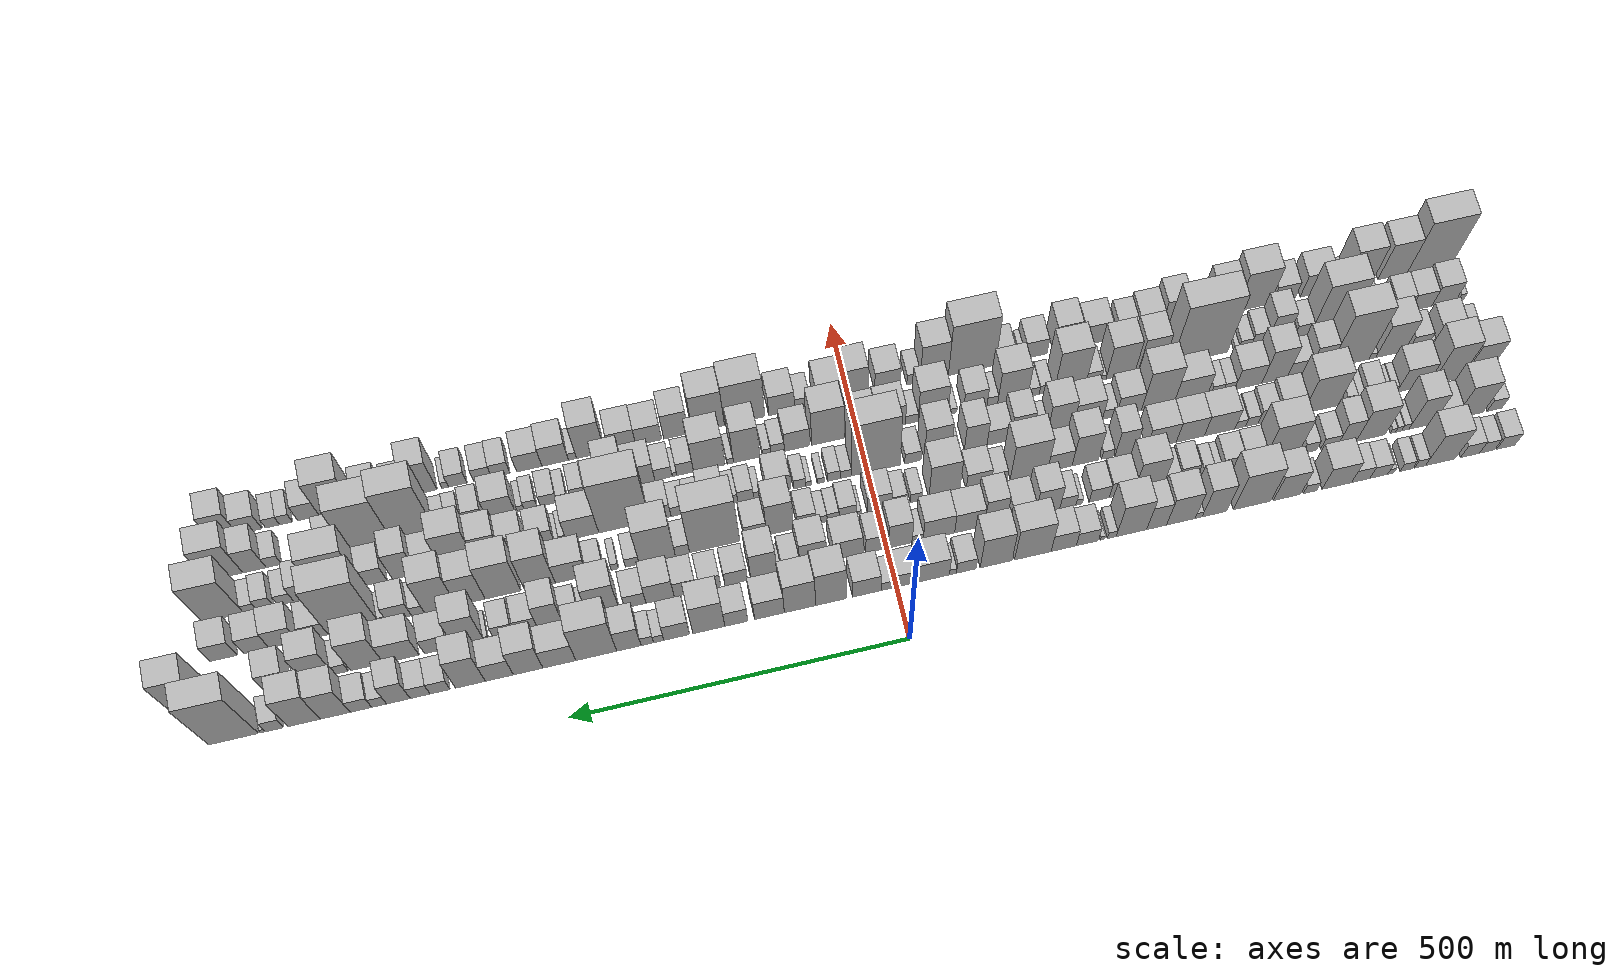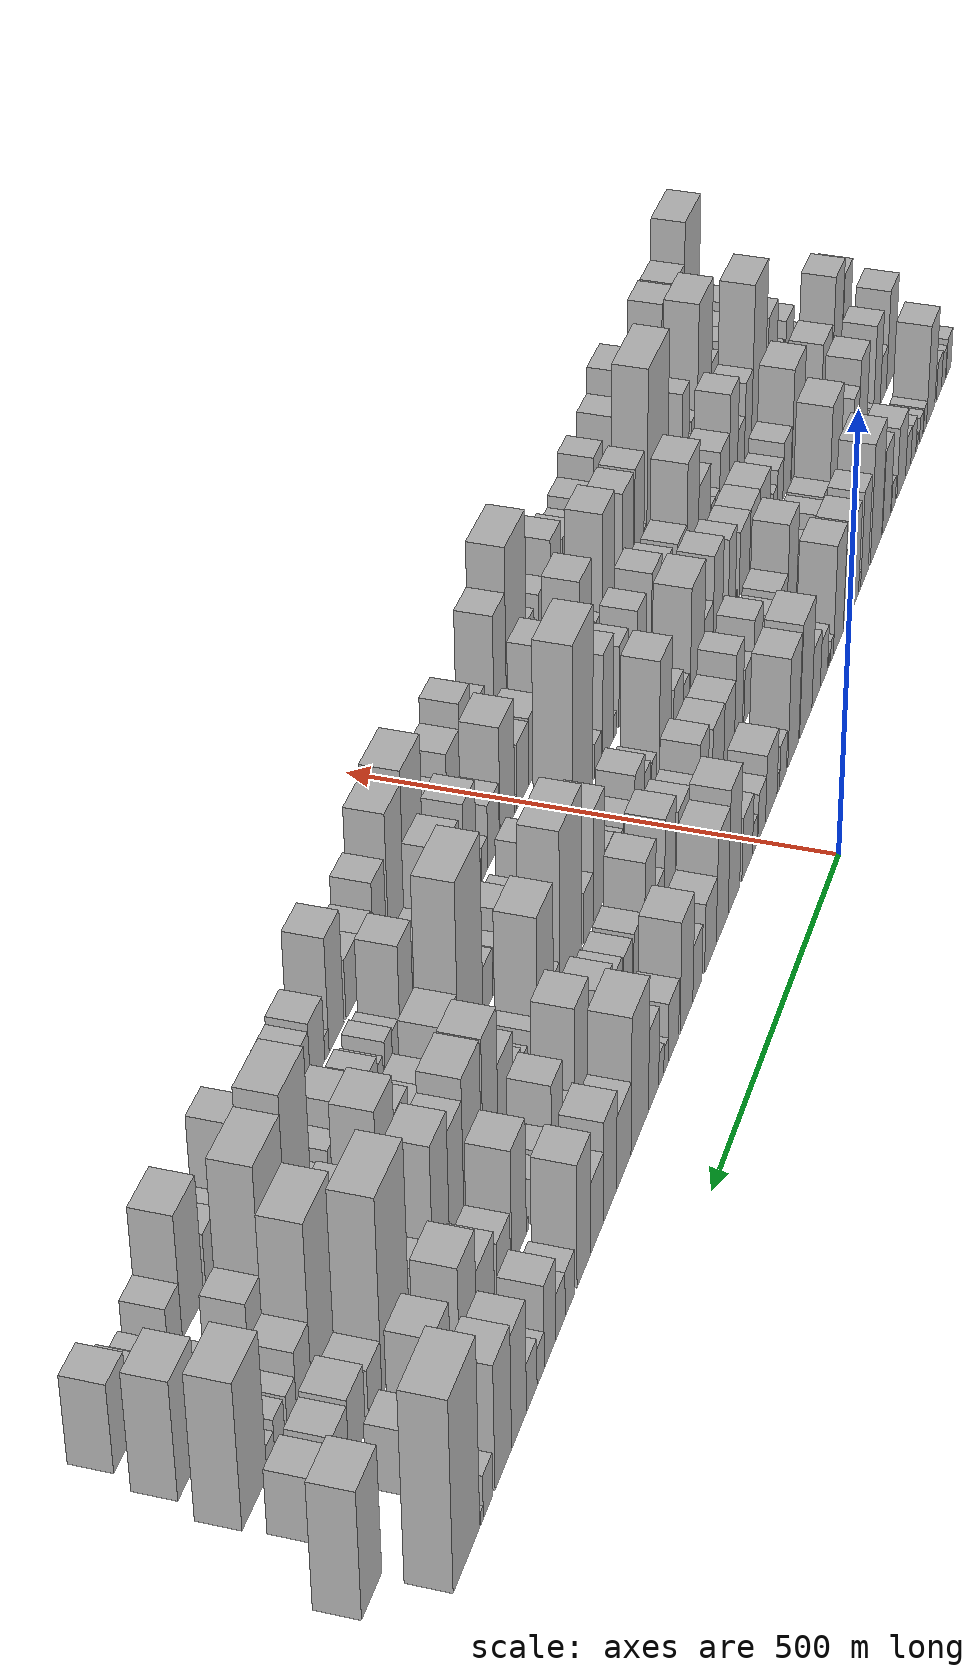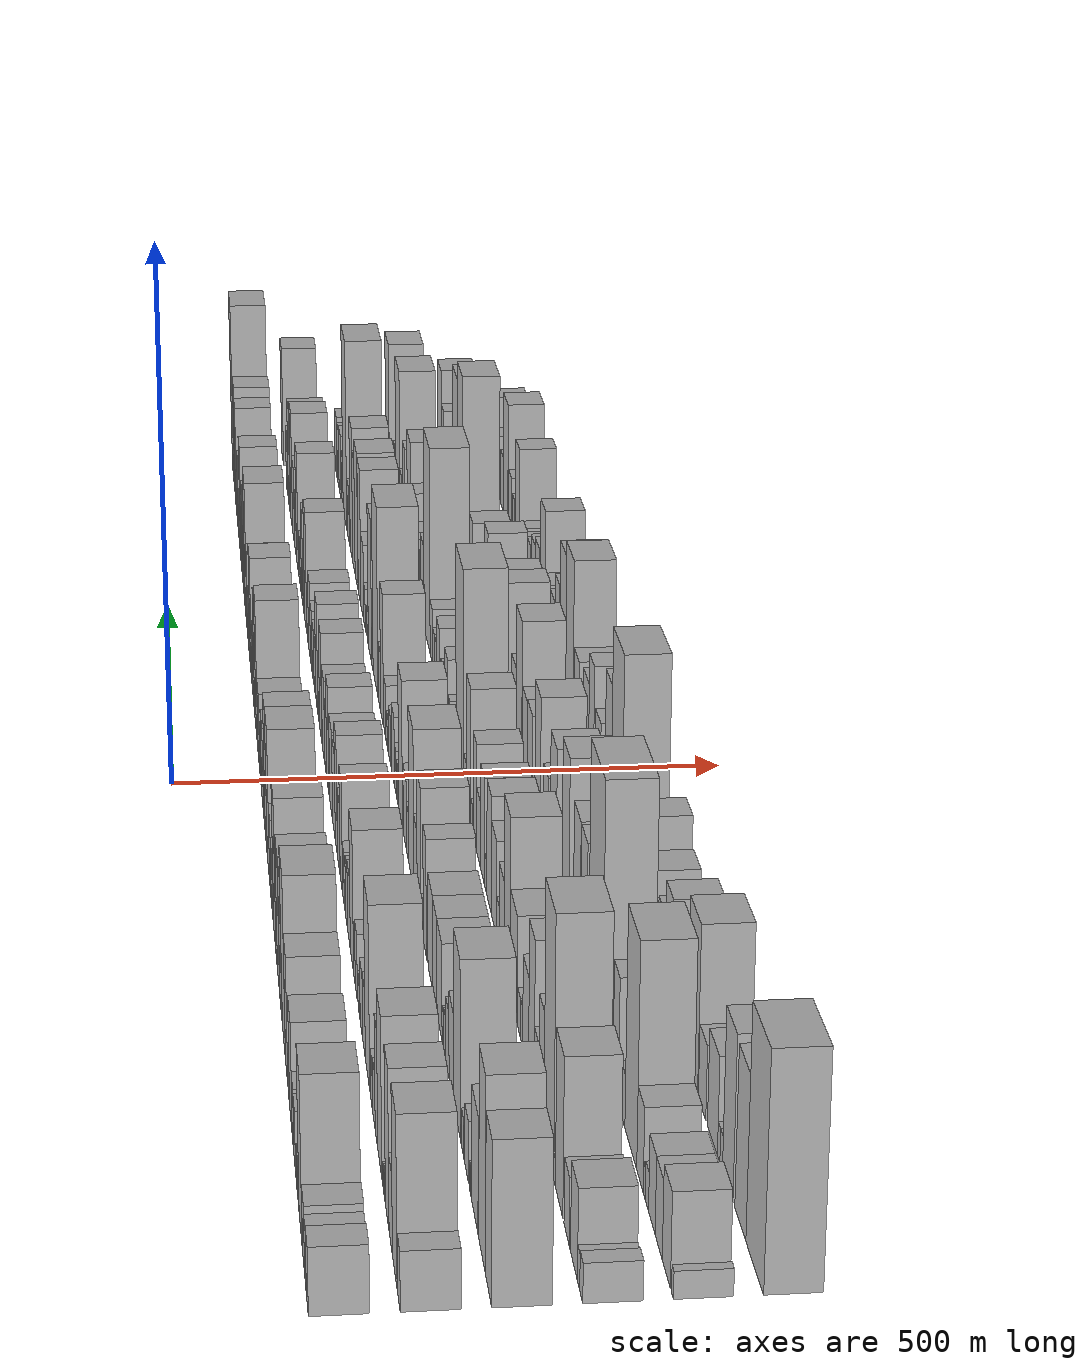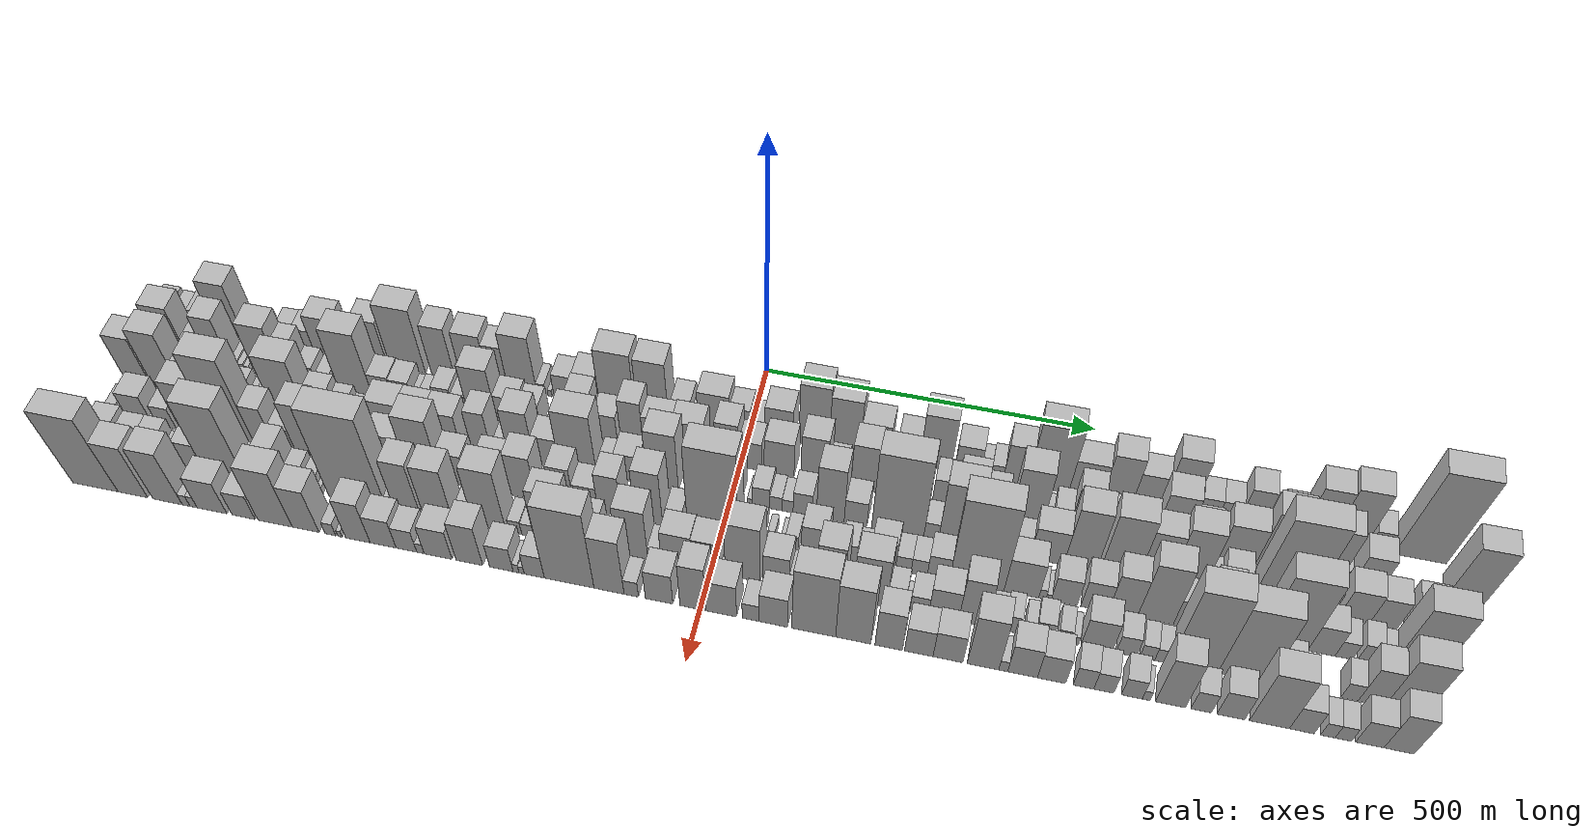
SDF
<sdf version="1.6">
 <world name="default">
  <scene>
   <sky><clouds><speed>12</speed></clouds></sky>
   <ambient>0.4 0.4 0.4 1</ambient>
   <background>0.7 0.7 0.7 1</background>
   <shadows>1</shadows>
  </scene>
  <gravity>0 0 -9.8066</gravity>
  <magnetic_field>6e-06 2.3e-05 -4.2e-05</magnetic_field>
  <physics default="0" name="default_physics" type="ode">
   <ode>
    <solver>
     <type>quick</type>
     <iters>10</iters>
     <sor>1.0</sor>
     <use_dynamic_moi_rescaling>0</use_dynamic_moi_rescaling>
    </solver>
    <constraints>
     <cfm>0</cfm>
     <erp>0.2</erp>
     <contact_max_correcting_vel>100</contact_max_correcting_vel>
     <contact_surface_layer>0.001</contact_surface_layer>
    </constraints>
   </ode>
   <max_step_size>0.004</max_step_size>
   <real_time_factor>1</real_time_factor>
   <real_time_update_rate>250</real_time_update_rate>
  </physics>
  <light name="sun" type="directional">
   <pose>0 0 10 0 0 0</pose>
   <diffuse>0.8 0.8 0.8 1</diffuse>
   <specular>0.2 0.2 0.2 1</specular>
   <attenuation>
    <range>1000</range>
    <constant>0.9</constant>
    <linear>0.01</linear>
    <quadratic>0.001</quadratic>
   </attenuation>
   <direction>-0.5 0.1 -0.9</direction>
  </light>
  <model name="building_1">
   <static>1</static>
   <pose>100.0000 -925.7938 0 0.000000 0.000000 0.000000</pose>
   <link name="link">
    <pose>0 0 25.50 0 0 0</pose>
    <collision name="collision"><geometry><box><size>40.0000 28.4124 51.0000</size></box></geometry></collision>
    <visual name="visual">
     <cast_shadows>0</cast_shadows>
     <geometry><box><size>40.0000 28.4124 51.0000</size></box></geometry>
     <material>
      <script>
       <uri>model://HANNAS_wall/materials/scripts</uri>
       <uri>model://HANNAS_wall/materials/textures</uri>
       <name>vrc/HANNAS_wall</name>
      </script>
     </material>
    </visual>
   </link>
  </model>
  <model name="building_2">
   <static>1</static>
   <pose>100.0000 -896.9620 0 0.000000 0.000000 0.000000</pose>
   <link name="link">
    <pose>0 0 22.50 0 0 0</pose>
    <collision name="collision"><geometry><box><size>40.0000 23.2511 45.0000</size></box></geometry></collision>
    <visual name="visual">
     <cast_shadows>0</cast_shadows>
     <geometry><box><size>40.0000 23.2511 45.0000</size></box></geometry>
     <material>
      <script>
       <uri>model://HANNAS_wall/materials/scripts</uri>
       <uri>model://HANNAS_wall/materials/textures</uri>
       <name>vrc/HANNAS_wall</name>
      </script>
     </material>
    </visual>
   </link>
  </model>
  <model name="building_3">
   <static>1</static>
   <pose>100.0000 -870.5901 0 0.000000 0.000000 0.000000</pose>
   <link name="link">
    <pose>0 0 25.50 0 0 0</pose>
    <collision name="collision"><geometry><box><size>40.0000 29.4928 51.0000</size></box></geometry></collision>
    <visual name="visual">
     <cast_shadows>0</cast_shadows>
     <geometry><box><size>40.0000 29.4928 51.0000</size></box></geometry>
     <material>
      <script>
       <uri>model://HANNAS_wall/materials/scripts</uri>
       <uri>model://HANNAS_wall/materials/textures</uri>
       <name>vrc/HANNAS_wall</name>
      </script>
     </material>
    </visual>
   </link>
  </model>
  <model name="building_4">
   <static>1</static>
   <pose>100.0000 -824.8516 0 0.000000 0.000000 0.000000</pose>
   <link name="link">
    <pose>0 0 64.50 0 0 0</pose>
    <collision name="collision"><geometry><box><size>40.0000 45.9840 129.0000</size></box></geometry></collision>
    <visual name="visual">
     <cast_shadows>0</cast_shadows>
     <geometry><box><size>40.0000 45.9840 129.0000</size></box></geometry>
     <material>
      <script>
       <uri>model://HANNAS_wall/materials/scripts</uri>
       <uri>model://HANNAS_wall/materials/textures</uri>
       <name>vrc/HANNAS_wall</name>
      </script>
     </material>
    </visual>
   </link>
  </model>
  <model name="building_5">
   <static>1</static>
   <pose>100.0000 -793.3695 0 0.000000 0.000000 0.000000</pose>
   <link name="link">
    <pose>0 0 16.50 0 0 0</pose>
    <collision name="collision"><geometry><box><size>40.0000 16.9802 33.0000</size></box></geometry></collision>
    <visual name="visual">
     <cast_shadows>0</cast_shadows>
     <geometry><box><size>40.0000 16.9802 33.0000</size></box></geometry>
     <material>
      <script>
       <uri>model://HANNAS_wall/materials/scripts</uri>
       <uri>model://HANNAS_wall/materials/textures</uri>
       <name>vrc/HANNAS_wall</name>
      </script>
     </material>
    </visual>
   </link>
  </model>
  <model name="building_6">
   <static>1</static>
   <pose>100.0000 -772.2433 0 0.000000 0.000000 0.000000</pose>
   <link name="link">
    <pose>0 0 16.50 0 0 0</pose>
    <collision name="collision"><geometry><box><size>40.0000 19.2723 33.0000</size></box></geometry></collision>
    <visual name="visual">
     <cast_shadows>0</cast_shadows>
     <geometry><box><size>40.0000 19.2723 33.0000</size></box></geometry>
     <material>
      <script>
       <uri>model://HANNAS_wall/materials/scripts</uri>
       <uri>model://HANNAS_wall/materials/textures</uri>
       <name>vrc/HANNAS_wall</name>
      </script>
     </material>
    </visual>
   </link>
  </model>
  <model name="building_7">
   <static>1</static>
   <pose>100.0000 -748.5811 0 0.000000 0.000000 0.000000</pose>
   <link name="link">
    <pose>0 0 10.50 0 0 0</pose>
    <collision name="collision"><geometry><box><size>40.0000 10.0522 21.0000</size></box></geometry></collision>
    <visual name="visual">
     <cast_shadows>0</cast_shadows>
     <geometry><box><size>40.0000 10.0522 21.0000</size></box></geometry>
     <material>
      <script>
       <uri>model://HANNAS_wall/materials/scripts</uri>
       <uri>model://HANNAS_wall/materials/textures</uri>
       <name>vrc/HANNAS_wall</name>
      </script>
     </material>
    </visual>
   </link>
  </model>
  <model name="building_8">
   <static>1</static>
   <pose>100.0000 -729.7922 0 0.000000 0.000000 0.000000</pose>
   <link name="link">
    <pose>0 0 24.00 0 0 0</pose>
    <collision name="collision"><geometry><box><size>40.0000 27.5256 48.0000</size></box></geometry></collision>
    <visual name="visual">
     <cast_shadows>0</cast_shadows>
     <geometry><box><size>40.0000 27.5256 48.0000</size></box></geometry>
     <material>
      <script>
       <uri>model://HANNAS_wall/materials/scripts</uri>
       <uri>model://HANNAS_wall/materials/textures</uri>
       <name>vrc/HANNAS_wall</name>
      </script>
     </material>
    </visual>
   </link>
  </model>
  <model name="building_9">
   <static>1</static>
   <pose>100.0000 -702.0516 0 0.000000 0.000000 0.000000</pose>
   <link name="link">
    <pose>0 0 25.50 0 0 0</pose>
    <collision name="collision"><geometry><box><size>40.0000 27.9556 51.0000</size></box></geometry></collision>
    <visual name="visual">
     <cast_shadows>0</cast_shadows>
     <geometry><box><size>40.0000 27.9556 51.0000</size></box></geometry>
     <material>
      <script>
       <uri>model://HANNAS_wall/materials/scripts</uri>
       <uri>model://HANNAS_wall/materials/textures</uri>
       <name>vrc/HANNAS_wall</name>
      </script>
     </material>
    </visual>
   </link>
  </model>
  <model name="building_10">
   <static>1</static>
   <pose>100.0000 -665.2863 0 0.000000 0.000000 0.000000</pose>
   <link name="link">
    <pose>0 0 45.00 0 0 0</pose>
    <collision name="collision"><geometry><box><size>40.0000 45.5750 90.0000</size></box></geometry></collision>
    <visual name="visual">
     <cast_shadows>0</cast_shadows>
     <geometry><box><size>40.0000 45.5750 90.0000</size></box></geometry>
     <material>
      <script>
       <uri>model://HANNAS_wall/materials/scripts</uri>
       <uri>model://HANNAS_wall/materials/textures</uri>
       <name>vrc/HANNAS_wall</name>
      </script>
     </material>
    </visual>
   </link>
  </model>
  <model name="building_11">
   <static>1</static>
   <pose>100.0000 -624.2099 0 0.000000 0.000000 0.000000</pose>
   <link name="link">
    <pose>0 0 18.00 0 0 0</pose>
    <collision name="collision"><geometry><box><size>40.0000 20.5779 36.0000</size></box></geometry></collision>
    <visual name="visual">
     <cast_shadows>0</cast_shadows>
     <geometry><box><size>40.0000 20.5779 36.0000</size></box></geometry>
     <material>
      <script>
       <uri>model://HANNAS_wall/materials/scripts</uri>
       <uri>model://HANNAS_wall/materials/textures</uri>
       <name>vrc/HANNAS_wall</name>
      </script>
     </material>
    </visual>
   </link>
  </model>
  <model name="building_12">
   <static>1</static>
   <pose>100.0000 -589.0660 0 0.000000 0.000000 0.000000</pose>
   <link name="link">
    <pose>0 0 52.50 0 0 0</pose>
    <collision name="collision"><geometry><box><size>40.0000 41.7099 105.0000</size></box></geometry></collision>
    <visual name="visual">
     <cast_shadows>0</cast_shadows>
     <geometry><box><size>40.0000 41.7099 105.0000</size></box></geometry>
     <material>
      <script>
       <uri>model://HANNAS_wall/materials/scripts</uri>
       <uri>model://HANNAS_wall/materials/textures</uri>
       <name>vrc/HANNAS_wall</name>
      </script>
     </material>
    </visual>
   </link>
  </model>
  <model name="building_13">
   <static>1</static>
   <pose>100.0000 -535.7185 0 0.000000 0.000000 0.000000</pose>
   <link name="link">
    <pose>0 0 75.00 0 0 0</pose>
    <collision name="collision"><geometry><box><size>40.0000 56.9851 150.0000</size></box></geometry></collision>
    <visual name="visual">
     <cast_shadows>0</cast_shadows>
     <geometry><box><size>40.0000 56.9851 150.0000</size></box></geometry>
     <material>
      <script>
       <uri>model://HANNAS_wall/materials/scripts</uri>
       <uri>model://HANNAS_wall/materials/textures</uri>
       <name>vrc/HANNAS_wall</name>
      </script>
     </material>
    </visual>
   </link>
  </model>
  <model name="building_14">
   <static>1</static>
   <pose>100.0000 -478.4410 0 0.000000 0.000000 0.000000</pose>
   <link name="link">
    <pose>0 0 60.00 0 0 0</pose>
    <collision name="collision"><geometry><box><size>40.0000 37.5699 120.0000</size></box></geometry></collision>
    <visual name="visual">
     <cast_shadows>0</cast_shadows>
     <geometry><box><size>40.0000 37.5699 120.0000</size></box></geometry>
     <material>
      <script>
       <uri>model://HANNAS_wall/materials/scripts</uri>
       <uri>model://HANNAS_wall/materials/textures</uri>
       <name>vrc/HANNAS_wall</name>
      </script>
     </material>
    </visual>
   </link>
  </model>
  <model name="building_15">
   <static>1</static>
   <pose>100.0000 -454.4406 0 0.000000 0.000000 0.000000</pose>
   <link name="link">
    <pose>0 0 12.00 0 0 0</pose>
    <collision name="collision"><geometry><box><size>40.0000 10.4310 24.0000</size></box></geometry></collision>
    <visual name="visual">
     <cast_shadows>0</cast_shadows>
     <geometry><box><size>40.0000 10.4310 24.0000</size></box></geometry>
     <material>
      <script>
       <uri>model://HANNAS_wall/materials/scripts</uri>
       <uri>model://HANNAS_wall/materials/textures</uri>
       <name>vrc/HANNAS_wall</name>
      </script>
     </material>
    </visual>
   </link>
  </model>
  <model name="building_16">
   <static>1</static>
   <pose>100.0000 -427.4320 0 0.000000 0.000000 0.000000</pose>
   <link name="link">
    <pose>0 0 58.50 0 0 0</pose>
    <collision name="collision"><geometry><box><size>40.0000 43.5862 117.0000</size></box></geometry></collision>
    <visual name="visual">
     <cast_shadows>0</cast_shadows>
     <geometry><box><size>40.0000 43.5862 117.0000</size></box></geometry>
     <material>
      <script>
       <uri>model://HANNAS_wall/materials/scripts</uri>
       <uri>model://HANNAS_wall/materials/textures</uri>
       <name>vrc/HANNAS_wall</name>
      </script>
     </material>
    </visual>
   </link>
  </model>
  <model name="building_17">
   <static>1</static>
   <pose>100.0000 -390.4925 0 0.000000 0.000000 0.000000</pose>
   <link name="link">
    <pose>0 0 49.50 0 0 0</pose>
    <collision name="collision"><geometry><box><size>40.0000 30.2928 99.0000</size></box></geometry></collision>
    <visual name="visual">
     <cast_shadows>0</cast_shadows>
     <geometry><box><size>40.0000 30.2928 99.0000</size></box></geometry>
     <material>
      <script>
       <uri>model://HANNAS_wall/materials/scripts</uri>
       <uri>model://HANNAS_wall/materials/textures</uri>
       <name>vrc/HANNAS_wall</name>
      </script>
     </material>
    </visual>
   </link>
  </model>
  <model name="building_18">
   <static>1</static>
   <pose>100.0000 -352.2517 0 0.000000 0.000000 0.000000</pose>
   <link name="link">
    <pose>0 0 67.50 0 0 0</pose>
    <collision name="collision"><geometry><box><size>40.0000 46.1887 135.0000</size></box></geometry></collision>
    <visual name="visual">
     <cast_shadows>0</cast_shadows>
     <geometry><box><size>40.0000 46.1887 135.0000</size></box></geometry>
     <material>
      <script>
       <uri>model://HANNAS_wall/materials/scripts</uri>
       <uri>model://HANNAS_wall/materials/textures</uri>
       <name>vrc/HANNAS_wall</name>
      </script>
     </material>
    </visual>
   </link>
  </model>
  <model name="building_19">
   <static>1</static>
   <pose>100.0000 -322.6024 0 0.000000 0.000000 0.000000</pose>
   <link name="link">
    <pose>0 0 13.50 0 0 0</pose>
    <collision name="collision"><geometry><box><size>40.0000 13.1100 27.0000</size></box></geometry></collision>
    <visual name="visual">
     <cast_shadows>0</cast_shadows>
     <geometry><box><size>40.0000 13.1100 27.0000</size></box></geometry>
     <material>
      <script>
       <uri>model://HANNAS_wall/materials/scripts</uri>
       <uri>model://HANNAS_wall/materials/textures</uri>
       <name>vrc/HANNAS_wall</name>
      </script>
     </material>
    </visual>
   </link>
  </model>
  <model name="building_20">
   <static>1</static>
   <pose>100.0000 -308.6756 0 0.000000 0.000000 0.000000</pose>
   <link name="link">
    <pose>0 0 7.50 0 0 0</pose>
    <collision name="collision"><geometry><box><size>40.0000 6.7435 15.0000</size></box></geometry></collision>
    <visual name="visual">
     <cast_shadows>0</cast_shadows>
     <geometry><box><size>40.0000 6.7435 15.0000</size></box></geometry>
     <material>
      <script>
       <uri>model://HANNAS_wall/materials/scripts</uri>
       <uri>model://HANNAS_wall/materials/textures</uri>
       <name>vrc/HANNAS_wall</name>
      </script>
     </material>
    </visual>
   </link>
  </model>
  <model name="building_21">
   <static>1</static>
   <pose>100.0000 -285.6280 0 0.000000 0.000000 0.000000</pose>
   <link name="link">
    <pose>0 0 28.50 0 0 0</pose>
    <collision name="collision"><geometry><box><size>40.0000 33.3519 57.0000</size></box></geometry></collision>
    <visual name="visual">
     <cast_shadows>0</cast_shadows>
     <geometry><box><size>40.0000 33.3519 57.0000</size></box></geometry>
     <material>
      <script>
       <uri>model://HANNAS_wall/materials/scripts</uri>
       <uri>model://HANNAS_wall/materials/textures</uri>
       <name>vrc/HANNAS_wall</name>
      </script>
     </material>
    </visual>
   </link>
  </model>
  <model name="building_22">
   <static>1</static>
   <pose>100.0000 -249.9652 0 0.000000 0.000000 0.000000</pose>
   <link name="link">
    <pose>0 0 36.00 0 0 0</pose>
    <collision name="collision"><geometry><box><size>40.0000 37.9737 72.0000</size></box></geometry></collision>
    <visual name="visual">
     <cast_shadows>0</cast_shadows>
     <geometry><box><size>40.0000 37.9737 72.0000</size></box></geometry>
     <material>
      <script>
       <uri>model://HANNAS_wall/materials/scripts</uri>
       <uri>model://HANNAS_wall/materials/textures</uri>
       <name>vrc/HANNAS_wall</name>
      </script>
     </material>
    </visual>
   </link>
  </model>
  <model name="building_23">
   <static>1</static>
   <pose>100.0000 -203.5561 0 0.000000 0.000000 0.000000</pose>
   <link name="link">
    <pose>0 0 69.00 0 0 0</pose>
    <collision name="collision"><geometry><box><size>40.0000 54.8445 138.0000</size></box></geometry></collision>
    <visual name="visual">
     <cast_shadows>0</cast_shadows>
     <geometry><box><size>40.0000 54.8445 138.0000</size></box></geometry>
     <material>
      <script>
       <uri>model://HANNAS_wall/materials/scripts</uri>
       <uri>model://HANNAS_wall/materials/textures</uri>
       <name>vrc/HANNAS_wall</name>
      </script>
     </material>
    </visual>
   </link>
  </model>
  <model name="building_24">
   <static>1</static>
   <pose>100.0000 -148.3149 0 0.000000 0.000000 0.000000</pose>
   <link name="link">
    <pose>0 0 66.00 0 0 0</pose>
    <collision name="collision"><geometry><box><size>40.0000 47.6379 132.0000</size></box></geometry></collision>
    <visual name="visual">
     <cast_shadows>0</cast_shadows>
     <geometry><box><size>40.0000 47.6379 132.0000</size></box></geometry>
     <material>
      <script>
       <uri>model://HANNAS_wall/materials/scripts</uri>
       <uri>model://HANNAS_wall/materials/textures</uri>
       <name>vrc/HANNAS_wall</name>
      </script>
     </material>
    </visual>
   </link>
  </model>
  <model name="building_25">
   <static>1</static>
   <pose>100.0000 -103.8084 0 0.000000 0.000000 0.000000</pose>
   <link name="link">
    <pose>0 0 25.50 0 0 0</pose>
    <collision name="collision"><geometry><box><size>40.0000 29.3752 51.0000</size></box></geometry></collision>
    <visual name="visual">
     <cast_shadows>0</cast_shadows>
     <geometry><box><size>40.0000 29.3752 51.0000</size></box></geometry>
     <material>
      <script>
       <uri>model://HANNAS_wall/materials/scripts</uri>
       <uri>model://HANNAS_wall/materials/textures</uri>
       <name>vrc/HANNAS_wall</name>
      </script>
     </material>
    </visual>
   </link>
  </model>
  <model name="building_26">
   <static>1</static>
   <pose>100.0000 -83.8414 0 0.000000 0.000000 0.000000</pose>
   <link name="link">
    <pose>0 0 12.00 0 0 0</pose>
    <collision name="collision"><geometry><box><size>40.0000 10.5588 24.0000</size></box></geometry></collision>
    <visual name="visual">
     <cast_shadows>0</cast_shadows>
     <geometry><box><size>40.0000 10.5588 24.0000</size></box></geometry>
     <material>
      <script>
       <uri>model://HANNAS_wall/materials/scripts</uri>
       <uri>model://HANNAS_wall/materials/textures</uri>
       <name>vrc/HANNAS_wall</name>
      </script>
     </material>
    </visual>
   </link>
  </model>
  <model name="building_27">
   <static>1</static>
   <pose>100.0000 -54.4065 0 0.000000 0.000000 0.000000</pose>
   <link name="link">
    <pose>0 0 40.50 0 0 0</pose>
    <collision name="collision"><geometry><box><size>40.0000 48.3110 81.0000</size></box></geometry></collision>
    <visual name="visual">
     <cast_shadows>0</cast_shadows>
     <geometry><box><size>40.0000 48.3110 81.0000</size></box></geometry>
     <material>
      <script>
       <uri>model://HANNAS_wall/materials/scripts</uri>
       <uri>model://HANNAS_wall/materials/textures</uri>
       <name>vrc/HANNAS_wall</name>
      </script>
     </material>
    </visual>
   </link>
  </model>
  <model name="building_28">
   <static>1</static>
   <pose>100.0000 -14.4142 0 0.000000 0.000000 0.000000</pose>
   <link name="link">
    <pose>0 0 28.50 0 0 0</pose>
    <collision name="collision"><geometry><box><size>40.0000 31.6736 57.0000</size></box></geometry></collision>
    <visual name="visual">
     <cast_shadows>0</cast_shadows>
     <geometry><box><size>40.0000 31.6736 57.0000</size></box></geometry>
     <material>
      <script>
       <uri>model://HANNAS_wall/materials/scripts</uri>
       <uri>model://HANNAS_wall/materials/textures</uri>
       <name>vrc/HANNAS_wall</name>
      </script>
     </material>
    </visual>
   </link>
  </model>
  <model name="building_29">
   <static>1</static>
   <pose>100.0000 14.0344 0 0.000000 0.000000 0.000000</pose>
   <link name="link">
    <pose>0 0 18.00 0 0 0</pose>
    <collision name="collision"><geometry><box><size>40.0000 19.2237 36.0000</size></box></geometry></collision>
    <visual name="visual">
     <cast_shadows>0</cast_shadows>
     <geometry><box><size>40.0000 19.2237 36.0000</size></box></geometry>
     <material>
      <script>
       <uri>model://HANNAS_wall/materials/scripts</uri>
       <uri>model://HANNAS_wall/materials/textures</uri>
       <name>vrc/HANNAS_wall</name>
      </script>
     </material>
    </visual>
   </link>
  </model>
  <model name="building_30">
   <static>1</static>
   <pose>100.0000 44.7785 0 0.000000 0.000000 0.000000</pose>
   <link name="link">
    <pose>0 0 37.50 0 0 0</pose>
    <collision name="collision"><geometry><box><size>40.0000 42.2645 75.0000</size></box></geometry></collision>
    <visual name="visual">
     <cast_shadows>0</cast_shadows>
     <geometry><box><size>40.0000 42.2645 75.0000</size></box></geometry>
     <material>
      <script>
       <uri>model://HANNAS_wall/materials/scripts</uri>
       <uri>model://HANNAS_wall/materials/textures</uri>
       <name>vrc/HANNAS_wall</name>
      </script>
     </material>
    </visual>
   </link>
  </model>
  <model name="building_31">
   <static>1</static>
   <pose>100.0000 97.7026 0 0.000000 0.000000 0.000000</pose>
   <link name="link">
    <pose>0 0 73.50 0 0 0</pose>
    <collision name="collision"><geometry><box><size>40.0000 45.5837 147.0000</size></box></geometry></collision>
    <visual name="visual">
     <cast_shadows>0</cast_shadows>
     <geometry><box><size>40.0000 45.5837 147.0000</size></box></geometry>
     <material>
      <script>
       <uri>model://HANNAS_wall/materials/scripts</uri>
       <uri>model://HANNAS_wall/materials/textures</uri>
       <name>vrc/HANNAS_wall</name>
      </script>
     </material>
    </visual>
   </link>
  </model>
  <model name="building_32">
   <static>1</static>
   <pose>100.0000 143.7222 0 0.000000 0.000000 0.000000</pose>
   <link name="link">
    <pose>0 0 64.50 0 0 0</pose>
    <collision name="collision"><geometry><box><size>40.0000 46.4555 129.0000</size></box></geometry></collision>
    <visual name="visual">
     <cast_shadows>0</cast_shadows>
     <geometry><box><size>40.0000 46.4555 129.0000</size></box></geometry>
     <material>
      <script>
       <uri>model://HANNAS_wall/materials/scripts</uri>
       <uri>model://HANNAS_wall/materials/textures</uri>
       <name>vrc/HANNAS_wall</name>
      </script>
     </material>
    </visual>
   </link>
  </model>
  <model name="building_33">
   <static>1</static>
   <pose>100.0000 188.9396 0 0.000000 0.000000 0.000000</pose>
   <link name="link">
    <pose>0 0 40.50 0 0 0</pose>
    <collision name="collision"><geometry><box><size>40.0000 43.9792 81.0000</size></box></geometry></collision>
    <visual name="visual">
     <cast_shadows>0</cast_shadows>
     <geometry><box><size>40.0000 43.9792 81.0000</size></box></geometry>
     <material>
      <script>
       <uri>model://HANNAS_wall/materials/scripts</uri>
       <uri>model://HANNAS_wall/materials/textures</uri>
       <name>vrc/HANNAS_wall</name>
      </script>
     </material>
    </visual>
   </link>
  </model>
  <model name="building_34">
   <static>1</static>
   <pose>100.0000 237.9428 0 0.000000 0.000000 0.000000</pose>
   <link name="link">
    <pose>0 0 33.00 0 0 0</pose>
    <collision name="collision"><geometry><box><size>40.0000 34.0271 66.0000</size></box></geometry></collision>
    <visual name="visual">
     <cast_shadows>0</cast_shadows>
     <geometry><box><size>40.0000 34.0271 66.0000</size></box></geometry>
     <material>
      <script>
       <uri>model://HANNAS_wall/materials/scripts</uri>
       <uri>model://HANNAS_wall/materials/textures</uri>
       <name>vrc/HANNAS_wall</name>
      </script>
     </material>
    </visual>
   </link>
  </model>
  <model name="building_35">
   <static>1</static>
   <pose>100.0000 278.3701 0 0.000000 0.000000 0.000000</pose>
   <link name="link">
    <pose>0 0 64.50 0 0 0</pose>
    <collision name="collision"><geometry><box><size>40.0000 46.8276 129.0000</size></box></geometry></collision>
    <visual name="visual">
     <cast_shadows>0</cast_shadows>
     <geometry><box><size>40.0000 46.8276 129.0000</size></box></geometry>
     <material>
      <script>
       <uri>model://HANNAS_wall/materials/scripts</uri>
       <uri>model://HANNAS_wall/materials/textures</uri>
       <name>vrc/HANNAS_wall</name>
      </script>
     </material>
    </visual>
   </link>
  </model>
  <model name="building_36">
   <static>1</static>
   <pose>100.0000 325.7030 0 0.000000 0.000000 0.000000</pose>
   <link name="link">
    <pose>0 0 34.50 0 0 0</pose>
    <collision name="collision"><geometry><box><size>40.0000 37.8383 69.0000</size></box></geometry></collision>
    <visual name="visual">
     <cast_shadows>0</cast_shadows>
     <geometry><box><size>40.0000 37.8383 69.0000</size></box></geometry>
     <material>
      <script>
       <uri>model://HANNAS_wall/materials/scripts</uri>
       <uri>model://HANNAS_wall/materials/textures</uri>
       <name>vrc/HANNAS_wall</name>
      </script>
     </material>
    </visual>
   </link>
  </model>
  <model name="building_37">
   <static>1</static>
   <pose>100.0000 352.2603 0 0.000000 0.000000 0.000000</pose>
   <link name="link">
    <pose>0 0 15.00 0 0 0</pose>
    <collision name="collision"><geometry><box><size>40.0000 15.2763 30.0000</size></box></geometry></collision>
    <visual name="visual">
     <cast_shadows>0</cast_shadows>
     <geometry><box><size>40.0000 15.2763 30.0000</size></box></geometry>
     <material>
      <script>
       <uri>model://HANNAS_wall/materials/scripts</uri>
       <uri>model://HANNAS_wall/materials/textures</uri>
       <name>vrc/HANNAS_wall</name>
      </script>
     </material>
    </visual>
   </link>
  </model>
  <model name="building_38">
   <static>1</static>
   <pose>100.0000 368.9714 0 0.000000 0.000000 0.000000</pose>
   <link name="link">
    <pose>0 0 18.00 0 0 0</pose>
    <collision name="collision"><geometry><box><size>40.0000 18.1458 36.0000</size></box></geometry></collision>
    <visual name="visual">
     <cast_shadows>0</cast_shadows>
     <geometry><box><size>40.0000 18.1458 36.0000</size></box></geometry>
     <material>
      <script>
       <uri>model://HANNAS_wall/materials/scripts</uri>
       <uri>model://HANNAS_wall/materials/textures</uri>
       <name>vrc/HANNAS_wall</name>
      </script>
     </material>
    </visual>
   </link>
  </model>
  <model name="building_39">
   <static>1</static>
   <pose>100.0000 395.9041 0 0.000000 0.000000 0.000000</pose>
   <link name="link">
    <pose>0 0 46.50 0 0 0</pose>
    <collision name="collision"><geometry><box><size>40.0000 35.7198 93.0000</size></box></geometry></collision>
    <visual name="visual">
     <cast_shadows>0</cast_shadows>
     <geometry><box><size>40.0000 35.7198 93.0000</size></box></geometry>
     <material>
      <script>
       <uri>model://HANNAS_wall/materials/scripts</uri>
       <uri>model://HANNAS_wall/materials/textures</uri>
       <name>vrc/HANNAS_wall</name>
      </script>
     </material>
    </visual>
   </link>
  </model>
  <model name="building_40">
   <static>1</static>
   <pose>100.0000 443.6201 0 0.000000 0.000000 0.000000</pose>
   <link name="link">
    <pose>0 0 78.00 0 0 0</pose>
    <collision name="collision"><geometry><box><size>40.0000 59.7121 156.0000</size></box></geometry></collision>
    <visual name="visual">
     <cast_shadows>0</cast_shadows>
     <geometry><box><size>40.0000 59.7121 156.0000</size></box></geometry>
     <material>
      <script>
       <uri>model://HANNAS_wall/materials/scripts</uri>
       <uri>model://HANNAS_wall/materials/textures</uri>
       <name>vrc/HANNAS_wall</name>
      </script>
     </material>
    </visual>
   </link>
  </model>
  <model name="building_41">
   <static>1</static>
   <pose>100.0000 497.5030 0 0.000000 0.000000 0.000000</pose>
   <link name="link">
    <pose>0 0 42.00 0 0 0</pose>
    <collision name="collision"><geometry><box><size>40.0000 48.0537 84.0000</size></box></geometry></collision>
    <visual name="visual">
     <cast_shadows>0</cast_shadows>
     <geometry><box><size>40.0000 48.0537 84.0000</size></box></geometry>
     <material>
      <script>
       <uri>model://HANNAS_wall/materials/scripts</uri>
       <uri>model://HANNAS_wall/materials/textures</uri>
       <name>vrc/HANNAS_wall</name>
      </script>
     </material>
    </visual>
   </link>
  </model>
  <model name="building_42">
   <static>1</static>
   <pose>100.0000 543.0667 0 0.000000 0.000000 0.000000</pose>
   <link name="link">
    <pose>0 0 57.00 0 0 0</pose>
    <collision name="collision"><geometry><box><size>40.0000 43.0736 114.0000</size></box></geometry></collision>
    <visual name="visual">
     <cast_shadows>0</cast_shadows>
     <geometry><box><size>40.0000 43.0736 114.0000</size></box></geometry>
     <material>
      <script>
       <uri>model://HANNAS_wall/materials/scripts</uri>
       <uri>model://HANNAS_wall/materials/textures</uri>
       <name>vrc/HANNAS_wall</name>
      </script>
     </material>
    </visual>
   </link>
  </model>
  <model name="building_43">
   <static>1</static>
   <pose>100.0000 584.9987 0 0.000000 0.000000 0.000000</pose>
   <link name="link">
    <pose>0 0 40.50 0 0 0</pose>
    <collision name="collision"><geometry><box><size>40.0000 40.7904 81.0000</size></box></geometry></collision>
    <visual name="visual">
     <cast_shadows>0</cast_shadows>
     <geometry><box><size>40.0000 40.7904 81.0000</size></box></geometry>
     <material>
      <script>
       <uri>model://HANNAS_wall/materials/scripts</uri>
       <uri>model://HANNAS_wall/materials/textures</uri>
       <name>vrc/HANNAS_wall</name>
      </script>
     </material>
    </visual>
   </link>
  </model>
  <model name="building_44">
   <static>1</static>
   <pose>100.0000 626.9853 0 0.000000 0.000000 0.000000</pose>
   <link name="link">
    <pose>0 0 69.00 0 0 0</pose>
    <collision name="collision"><geometry><box><size>40.0000 43.1828 138.0000</size></box></geometry></collision>
    <visual name="visual">
     <cast_shadows>0</cast_shadows>
     <geometry><box><size>40.0000 43.1828 138.0000</size></box></geometry>
     <material>
      <script>
       <uri>model://HANNAS_wall/materials/scripts</uri>
       <uri>model://HANNAS_wall/materials/textures</uri>
       <name>vrc/HANNAS_wall</name>
      </script>
     </material>
    </visual>
   </link>
  </model>
  <model name="building_45">
   <static>1</static>
   <pose>100.0000 670.9746 0 0.000000 0.000000 0.000000</pose>
   <link name="link">
    <pose>0 0 25.50 0 0 0</pose>
    <collision name="collision"><geometry><box><size>40.0000 28.7959 51.0000</size></box></geometry></collision>
    <visual name="visual">
     <cast_shadows>0</cast_shadows>
     <geometry><box><size>40.0000 28.7959 51.0000</size></box></geometry>
     <material>
      <script>
       <uri>model://HANNAS_wall/materials/scripts</uri>
       <uri>model://HANNAS_wall/materials/textures</uri>
       <name>vrc/HANNAS_wall</name>
      </script>
     </material>
    </visual>
   </link>
  </model>
  <model name="building_46">
   <static>1</static>
   <pose>100.0000 699.7390 0 0.000000 0.000000 0.000000</pose>
   <link name="link">
    <pose>0 0 25.50 0 0 0</pose>
    <collision name="collision"><geometry><box><size>40.0000 28.7329 51.0000</size></box></geometry></collision>
    <visual name="visual">
     <cast_shadows>0</cast_shadows>
     <geometry><box><size>40.0000 28.7329 51.0000</size></box></geometry>
     <material>
      <script>
       <uri>model://HANNAS_wall/materials/scripts</uri>
       <uri>model://HANNAS_wall/materials/textures</uri>
       <name>vrc/HANNAS_wall</name>
      </script>
     </material>
    </visual>
   </link>
  </model>
  <model name="building_47">
   <static>1</static>
   <pose>100.0000 731.2139 0 0.000000 0.000000 0.000000</pose>
   <link name="link">
    <pose>0 0 46.50 0 0 0</pose>
    <collision name="collision"><geometry><box><size>40.0000 34.2169 93.0000</size></box></geometry></collision>
    <visual name="visual">
     <cast_shadows>0</cast_shadows>
     <geometry><box><size>40.0000 34.2169 93.0000</size></box></geometry>
     <material>
      <script>
       <uri>model://HANNAS_wall/materials/scripts</uri>
       <uri>model://HANNAS_wall/materials/textures</uri>
       <name>vrc/HANNAS_wall</name>
      </script>
     </material>
    </visual>
   </link>
  </model>
  <model name="building_48">
   <static>1</static>
   <pose>100.0000 759.0580 0 0.000000 0.000000 0.000000</pose>
   <link name="link">
    <pose>0 0 21.00 0 0 0</pose>
    <collision name="collision"><geometry><box><size>40.0000 21.4712 42.0000</size></box></geometry></collision>
    <visual name="visual">
     <cast_shadows>0</cast_shadows>
     <geometry><box><size>40.0000 21.4712 42.0000</size></box></geometry>
     <material>
      <script>
       <uri>model://HANNAS_wall/materials/scripts</uri>
       <uri>model://HANNAS_wall/materials/textures</uri>
       <name>vrc/HANNAS_wall</name>
      </script>
     </material>
    </visual>
   </link>
  </model>
  <model name="building_49">
   <static>1</static>
   <pose>100.0000 785.2733 0 0.000000 0.000000 0.000000</pose>
   <link name="link">
    <pose>0 0 27.00 0 0 0</pose>
    <collision name="collision"><geometry><box><size>40.0000 30.9595 54.0000</size></box></geometry></collision>
    <visual name="visual">
     <cast_shadows>0</cast_shadows>
     <geometry><box><size>40.0000 30.9595 54.0000</size></box></geometry>
     <material>
      <script>
       <uri>model://HANNAS_wall/materials/scripts</uri>
       <uri>model://HANNAS_wall/materials/textures</uri>
       <name>vrc/HANNAS_wall</name>
      </script>
     </material>
    </visual>
   </link>
  </model>
  <model name="building_50">
   <static>1</static>
   <pose>100.0000 822.1790 0 0.000000 0.000000 0.000000</pose>
   <link name="link">
    <pose>0 0 63.00 0 0 0</pose>
    <collision name="collision"><geometry><box><size>40.0000 42.8519 126.0000</size></box></geometry></collision>
    <visual name="visual">
     <cast_shadows>0</cast_shadows>
     <geometry><box><size>40.0000 42.8519 126.0000</size></box></geometry>
     <material>
      <script>
       <uri>model://HANNAS_wall/materials/scripts</uri>
       <uri>model://HANNAS_wall/materials/textures</uri>
       <name>vrc/HANNAS_wall</name>
      </script>
     </material>
    </visual>
   </link>
  </model>
  <model name="building_51">
   <static>1</static>
   <pose>100.0000 866.9608 0 0.000000 0.000000 0.000000</pose>
   <link name="link">
    <pose>0 0 69.00 0 0 0</pose>
    <collision name="collision"><geometry><box><size>40.0000 46.7116 138.0000</size></box></geometry></collision>
    <visual name="visual">
     <cast_shadows>0</cast_shadows>
     <geometry><box><size>40.0000 46.7116 138.0000</size></box></geometry>
     <material>
      <script>
       <uri>model://HANNAS_wall/materials/scripts</uri>
       <uri>model://HANNAS_wall/materials/textures</uri>
       <name>vrc/HANNAS_wall</name>
      </script>
     </material>
    </visual>
   </link>
  </model>
  <model name="building_52">
   <static>1</static>
   <pose>100.0000 909.4379 0 0.000000 0.000000 0.000000</pose>
   <link name="link">
    <pose>0 0 24.00 0 0 0</pose>
    <collision name="collision"><geometry><box><size>40.0000 26.2428 48.0000</size></box></geometry></collision>
    <visual name="visual">
     <cast_shadows>0</cast_shadows>
     <geometry><box><size>40.0000 26.2428 48.0000</size></box></geometry>
     <material>
      <script>
       <uri>model://HANNAS_wall/materials/scripts</uri>
       <uri>model://HANNAS_wall/materials/textures</uri>
       <name>vrc/HANNAS_wall</name>
      </script>
     </material>
    </visual>
   </link>
  </model>
  <model name="building_53">
   <static>1</static>
   <pose>100.0000 925.9693 0 0.000000 0.000000 0.000000</pose>
   <link name="link">
    <pose>0 0 7.50 0 0 0</pose>
    <collision name="collision"><geometry><box><size>40.0000 6.8199 15.0000</size></box></geometry></collision>
    <visual name="visual">
     <cast_shadows>0</cast_shadows>
     <geometry><box><size>40.0000 6.8199 15.0000</size></box></geometry>
     <material>
      <script>
       <uri>model://HANNAS_wall/materials/scripts</uri>
       <uri>model://HANNAS_wall/materials/textures</uri>
       <name>vrc/HANNAS_wall</name>
      </script>
     </material>
    </visual>
   </link>
  </model>
  <model name="building_54">
   <static>1</static>
   <pose>100.0000 968.1452 0 0.000000 0.000000 0.000000</pose>
   <link name="link">
    <pose>0 0 105.00 0 0 0</pose>
    <collision name="collision"><geometry><box><size>40.0000 71.5319 210.0000</size></box></geometry></collision>
    <visual name="visual">
     <cast_shadows>0</cast_shadows>
     <geometry><box><size>40.0000 71.5319 210.0000</size></box></geometry>
     <material>
      <script>
       <uri>model://HANNAS_wall/materials/scripts</uri>
       <uri>model://HANNAS_wall/materials/textures</uri>
       <name>vrc/HANNAS_wall</name>
      </script>
     </material>
    </visual>
   </link>
  </model>
  <model name="building_55">
   <static>1</static>
   <pose>160.0000 -928.2729 0 0.000000 0.000000 0.000000</pose>
   <link name="link">
    <pose>0 0 22.50 0 0 0</pose>
    <collision name="collision"><geometry><box><size>40.0000 23.4542 45.0000</size></box></geometry></collision>
    <visual name="visual">
     <cast_shadows>0</cast_shadows>
     <geometry><box><size>40.0000 23.4542 45.0000</size></box></geometry>
     <material>
      <script>
       <uri>model://HANNAS_wall/materials/scripts</uri>
       <uri>model://HANNAS_wall/materials/textures</uri>
       <name>vrc/HANNAS_wall</name>
      </script>
     </material>
    </visual>
   </link>
  </model>
  <model name="building_56">
   <static>1</static>
   <pose>160.0000 -888.1282 0 0.000000 0.000000 0.000000</pose>
   <link name="link">
    <pose>0 0 64.50 0 0 0</pose>
    <collision name="collision"><geometry><box><size>40.0000 44.8353 129.0000</size></box></geometry></collision>
    <visual name="visual">
     <cast_shadows>0</cast_shadows>
     <geometry><box><size>40.0000 44.8353 129.0000</size></box></geometry>
     <material>
      <script>
       <uri>model://HANNAS_wall/materials/scripts</uri>
       <uri>model://HANNAS_wall/materials/textures</uri>
       <name>vrc/HANNAS_wall</name>
      </script>
     </material>
    </visual>
   </link>
  </model>
  <model name="building_57">
   <static>1</static>
   <pose>160.0000 -849.1035 0 0.000000 0.000000 0.000000</pose>
   <link name="link">
    <pose>0 0 30.00 0 0 0</pose>
    <collision name="collision"><geometry><box><size>40.0000 33.2142 60.0000</size></box></geometry></collision>
    <visual name="visual">
     <cast_shadows>0</cast_shadows>
     <geometry><box><size>40.0000 33.2142 60.0000</size></box></geometry>
     <material>
      <script>
       <uri>model://HANNAS_wall/materials/scripts</uri>
       <uri>model://HANNAS_wall/materials/textures</uri>
       <name>vrc/HANNAS_wall</name>
      </script>
     </material>
    </visual>
   </link>
  </model>
  <model name="building_58">
   <static>1</static>
   <pose>160.0000 -813.9708 0 0.000000 0.000000 0.000000</pose>
   <link name="link">
    <pose>0 0 61.50 0 0 0</pose>
    <collision name="collision"><geometry><box><size>40.0000 37.0511 123.0000</size></box></geometry></collision>
    <visual name="visual">
     <cast_shadows>0</cast_shadows>
     <geometry><box><size>40.0000 37.0511 123.0000</size></box></geometry>
     <material>
      <script>
       <uri>model://HANNAS_wall/materials/scripts</uri>
       <uri>model://HANNAS_wall/materials/textures</uri>
       <name>vrc/HANNAS_wall</name>
      </script>
     </material>
    </visual>
   </link>
  </model>
  <model name="building_59">
   <static>1</static>
   <pose>160.0000 -789.7222 0 0.000000 0.000000 0.000000</pose>
   <link name="link">
    <pose>0 0 12.00 0 0 0</pose>
    <collision name="collision"><geometry><box><size>40.0000 11.4462 24.0000</size></box></geometry></collision>
    <visual name="visual">
     <cast_shadows>0</cast_shadows>
     <geometry><box><size>40.0000 11.4462 24.0000</size></box></geometry>
     <material>
      <script>
       <uri>model://HANNAS_wall/materials/scripts</uri>
       <uri>model://HANNAS_wall/materials/textures</uri>
       <name>vrc/HANNAS_wall</name>
      </script>
     </material>
    </visual>
   </link>
  </model>
  <model name="building_60">
   <static>1</static>
   <pose>160.0000 -779.3121 0 0.000000 0.000000 0.000000</pose>
   <link name="link">
    <pose>0 0 10.50 0 0 0</pose>
    <collision name="collision"><geometry><box><size>40.0000 9.3740 21.0000</size></box></geometry></collision>
    <visual name="visual">
     <cast_shadows>0</cast_shadows>
     <geometry><box><size>40.0000 9.3740 21.0000</size></box></geometry>
     <material>
      <script>
       <uri>model://HANNAS_wall/materials/scripts</uri>
       <uri>model://HANNAS_wall/materials/textures</uri>
       <name>vrc/HANNAS_wall</name>
      </script>
     </material>
    </visual>
   </link>
  </model>
  <model name="building_61">
   <static>1</static>
   <pose>160.0000 -770.5227 0 0.000000 0.000000 0.000000</pose>
   <link name="link">
    <pose>0 0 9.00 0 0 0</pose>
    <collision name="collision"><geometry><box><size>40.0000 8.2050 18.0000</size></box></geometry></collision>
    <visual name="visual">
     <cast_shadows>0</cast_shadows>
     <geometry><box><size>40.0000 8.2050 18.0000</size></box></geometry>
     <material>
      <script>
       <uri>model://HANNAS_wall/materials/scripts</uri>
       <uri>model://HANNAS_wall/materials/textures</uri>
       <name>vrc/HANNAS_wall</name>
      </script>
     </material>
    </visual>
   </link>
  </model>
  <model name="building_62">
   <static>1</static>
   <pose>160.0000 -736.0024 0 0.000000 0.000000 0.000000</pose>
   <link name="link">
    <pose>0 0 63.00 0 0 0</pose>
    <collision name="collision"><geometry><box><size>40.0000 44.8356 126.0000</size></box></geometry></collision>
    <visual name="visual">
     <cast_shadows>0</cast_shadows>
     <geometry><box><size>40.0000 44.8356 126.0000</size></box></geometry>
     <material>
      <script>
       <uri>model://HANNAS_wall/materials/scripts</uri>
       <uri>model://HANNAS_wall/materials/textures</uri>
       <name>vrc/HANNAS_wall</name>
      </script>
     </material>
    </visual>
   </link>
  </model>
  <model name="building_63">
   <static>1</static>
   <pose>160.0000 -699.2651 0 0.000000 0.000000 0.000000</pose>
   <link name="link">
    <pose>0 0 46.50 0 0 0</pose>
    <collision name="collision"><geometry><box><size>40.0000 28.6390 93.0000</size></box></geometry></collision>
    <visual name="visual">
     <cast_shadows>0</cast_shadows>
     <geometry><box><size>40.0000 28.6390 93.0000</size></box></geometry>
     <material>
      <script>
       <uri>model://HANNAS_wall/materials/scripts</uri>
       <uri>model://HANNAS_wall/materials/textures</uri>
       <name>vrc/HANNAS_wall</name>
      </script>
     </material>
    </visual>
   </link>
  </model>
  <model name="building_64">
   <static>1</static>
   <pose>160.0000 -671.7702 0 0.000000 0.000000 0.000000</pose>
   <link name="link">
    <pose>0 0 22.50 0 0 0</pose>
    <collision name="collision"><geometry><box><size>40.0000 26.3509 45.0000</size></box></geometry></collision>
    <visual name="visual">
     <cast_shadows>0</cast_shadows>
     <geometry><box><size>40.0000 26.3509 45.0000</size></box></geometry>
     <material>
      <script>
       <uri>model://HANNAS_wall/materials/scripts</uri>
       <uri>model://HANNAS_wall/materials/textures</uri>
       <name>vrc/HANNAS_wall</name>
      </script>
     </material>
    </visual>
   </link>
  </model>
  <model name="building_65">
   <static>1</static>
   <pose>160.0000 -641.9309 0 0.000000 0.000000 0.000000</pose>
   <link name="link">
    <pose>0 0 19.50 0 0 0</pose>
    <collision name="collision"><geometry><box><size>40.0000 21.3277 39.0000</size></box></geometry></collision>
    <visual name="visual">
     <cast_shadows>0</cast_shadows>
     <geometry><box><size>40.0000 21.3277 39.0000</size></box></geometry>
     <material>
      <script>
       <uri>model://HANNAS_wall/materials/scripts</uri>
       <uri>model://HANNAS_wall/materials/textures</uri>
       <name>vrc/HANNAS_wall</name>
      </script>
     </material>
    </visual>
   </link>
  </model>
  <model name="building_66">
   <static>1</static>
   <pose>160.0000 -596.3192 0 0.000000 0.000000 0.000000</pose>
   <link name="link">
    <pose>0 0 75.00 0 0 0</pose>
    <collision name="collision"><geometry><box><size>40.0000 53.8957 150.0000</size></box></geometry></collision>
    <visual name="visual">
     <cast_shadows>0</cast_shadows>
     <geometry><box><size>40.0000 53.8957 150.0000</size></box></geometry>
     <material>
      <script>
       <uri>model://HANNAS_wall/materials/scripts</uri>
       <uri>model://HANNAS_wall/materials/textures</uri>
       <name>vrc/HANNAS_wall</name>
      </script>
     </material>
    </visual>
   </link>
  </model>
  <model name="building_67">
   <static>1</static>
   <pose>160.0000 -552.9038 0 0.000000 0.000000 0.000000</pose>
   <link name="link">
    <pose>0 0 28.50 0 0 0</pose>
    <collision name="collision"><geometry><box><size>40.0000 32.9350 57.0000</size></box></geometry></collision>
    <visual name="visual">
     <cast_shadows>0</cast_shadows>
     <geometry><box><size>40.0000 32.9350 57.0000</size></box></geometry>
     <material>
      <script>
       <uri>model://HANNAS_wall/materials/scripts</uri>
       <uri>model://HANNAS_wall/materials/textures</uri>
       <name>vrc/HANNAS_wall</name>
      </script>
     </material>
    </visual>
   </link>
  </model>
  <model name="building_68">
   <static>1</static>
   <pose>160.0000 -520.5851 0 0.000000 0.000000 0.000000</pose>
   <link name="link">
    <pose>0 0 27.00 0 0 0</pose>
    <collision name="collision"><geometry><box><size>40.0000 31.7025 54.0000</size></box></geometry></collision>
    <visual name="visual">
     <cast_shadows>0</cast_shadows>
     <geometry><box><size>40.0000 31.7025 54.0000</size></box></geometry>
     <material>
      <script>
       <uri>model://HANNAS_wall/materials/scripts</uri>
       <uri>model://HANNAS_wall/materials/textures</uri>
       <name>vrc/HANNAS_wall</name>
      </script>
     </material>
    </visual>
   </link>
  </model>
  <model name="building_69">
   <static>1</static>
   <pose>160.0000 -499.2107 0 0.000000 0.000000 0.000000</pose>
   <link name="link">
    <pose>0 0 13.50 0 0 0</pose>
    <collision name="collision"><geometry><box><size>40.0000 11.0464 27.0000</size></box></geometry></collision>
    <visual name="visual">
     <cast_shadows>0</cast_shadows>
     <geometry><box><size>40.0000 11.0464 27.0000</size></box></geometry>
     <material>
      <script>
       <uri>model://HANNAS_wall/materials/scripts</uri>
       <uri>model://HANNAS_wall/materials/textures</uri>
       <name>vrc/HANNAS_wall</name>
      </script>
     </material>
    </visual>
   </link>
  </model>
  <model name="building_70">
   <static>1</static>
   <pose>160.0000 -485.2275 0 0.000000 0.000000 0.000000</pose>
   <link name="link">
    <pose>0 0 15.00 0 0 0</pose>
    <collision name="collision"><geometry><box><size>40.0000 16.9200 30.0000</size></box></geometry></collision>
    <visual name="visual">
     <cast_shadows>0</cast_shadows>
     <geometry><box><size>40.0000 16.9200 30.0000</size></box></geometry>
     <material>
      <script>
       <uri>model://HANNAS_wall/materials/scripts</uri>
       <uri>model://HANNAS_wall/materials/textures</uri>
       <name>vrc/HANNAS_wall</name>
      </script>
     </material>
    </visual>
   </link>
  </model>
  <model name="building_71">
   <static>1</static>
   <pose>160.0000 -454.5164 0 0.000000 0.000000 0.000000</pose>
   <link name="link">
    <pose>0 0 28.50 0 0 0</pose>
    <collision name="collision"><geometry><box><size>40.0000 28.5022 57.0000</size></box></geometry></collision>
    <visual name="visual">
     <cast_shadows>0</cast_shadows>
     <geometry><box><size>40.0000 28.5022 57.0000</size></box></geometry>
     <material>
      <script>
       <uri>model://HANNAS_wall/materials/scripts</uri>
       <uri>model://HANNAS_wall/materials/textures</uri>
       <name>vrc/HANNAS_wall</name>
      </script>
     </material>
    </visual>
   </link>
  </model>
  <model name="building_72">
   <static>1</static>
   <pose>160.0000 -428.9410 0 0.000000 0.000000 0.000000</pose>
   <link name="link">
    <pose>0 0 22.50 0 0 0</pose>
    <collision name="collision"><geometry><box><size>40.0000 22.6488 45.0000</size></box></geometry></collision>
    <visual name="visual">
     <cast_shadows>0</cast_shadows>
     <geometry><box><size>40.0000 22.6488 45.0000</size></box></geometry>
     <material>
      <script>
       <uri>model://HANNAS_wall/materials/scripts</uri>
       <uri>model://HANNAS_wall/materials/textures</uri>
       <name>vrc/HANNAS_wall</name>
      </script>
     </material>
    </visual>
   </link>
  </model>
  <model name="building_73">
   <static>1</static>
   <pose>160.0000 -395.3346 0 0.000000 0.000000 0.000000</pose>
   <link name="link">
    <pose>0 0 61.50 0 0 0</pose>
    <collision name="collision"><geometry><box><size>40.0000 44.5640 123.0000</size></box></geometry></collision>
    <visual name="visual">
     <cast_shadows>0</cast_shadows>
     <geometry><box><size>40.0000 44.5640 123.0000</size></box></geometry>
     <material>
      <script>
       <uri>model://HANNAS_wall/materials/scripts</uri>
       <uri>model://HANNAS_wall/materials/textures</uri>
       <name>vrc/HANNAS_wall</name>
      </script>
     </material>
    </visual>
   </link>
  </model>
  <model name="building_74">
   <static>1</static>
   <pose>160.0000 -354.2393 0 0.000000 0.000000 0.000000</pose>
   <link name="link">
    <pose>0 0 31.50 0 0 0</pose>
    <collision name="collision"><geometry><box><size>40.0000 37.6266 63.0000</size></box></geometry></collision>
    <visual name="visual">
     <cast_shadows>0</cast_shadows>
     <geometry><box><size>40.0000 37.6266 63.0000</size></box></geometry>
     <material>
      <script>
       <uri>model://HANNAS_wall/materials/scripts</uri>
       <uri>model://HANNAS_wall/materials/textures</uri>
       <name>vrc/HANNAS_wall</name>
      </script>
     </material>
    </visual>
   </link>
  </model>
  <model name="building_75">
   <static>1</static>
   <pose>160.0000 -319.9886 0 0.000000 0.000000 0.000000</pose>
   <link name="link">
    <pose>0 0 27.00 0 0 0</pose>
    <collision name="collision"><geometry><box><size>40.0000 30.8747 54.0000</size></box></geometry></collision>
    <visual name="visual">
     <cast_shadows>0</cast_shadows>
     <geometry><box><size>40.0000 30.8747 54.0000</size></box></geometry>
     <material>
      <script>
       <uri>model://HANNAS_wall/materials/scripts</uri>
       <uri>model://HANNAS_wall/materials/textures</uri>
       <name>vrc/HANNAS_wall</name>
      </script>
     </material>
    </visual>
   </link>
  </model>
  <model name="building_76">
   <static>1</static>
   <pose>160.0000 -289.6225 0 0.000000 0.000000 0.000000</pose>
   <link name="link">
    <pose>0 0 12.00 0 0 0</pose>
    <collision name="collision"><geometry><box><size>40.0000 9.8574 24.0000</size></box></geometry></collision>
    <visual name="visual">
     <cast_shadows>0</cast_shadows>
     <geometry><box><size>40.0000 9.8574 24.0000</size></box></geometry>
     <material>
      <script>
       <uri>model://HANNAS_wall/materials/scripts</uri>
       <uri>model://HANNAS_wall/materials/textures</uri>
       <name>vrc/HANNAS_wall</name>
      </script>
     </material>
    </visual>
   </link>
  </model>
  <model name="building_77">
   <static>1</static>
   <pose>160.0000 -272.3909 0 0.000000 0.000000 0.000000</pose>
   <link name="link">
    <pose>0 0 24.00 0 0 0</pose>
    <collision name="collision"><geometry><box><size>40.0000 24.6058 48.0000</size></box></geometry></collision>
    <visual name="visual">
     <cast_shadows>0</cast_shadows>
     <geometry><box><size>40.0000 24.6058 48.0000</size></box></geometry>
     <material>
      <script>
       <uri>model://HANNAS_wall/materials/scripts</uri>
       <uri>model://HANNAS_wall/materials/textures</uri>
       <name>vrc/HANNAS_wall</name>
      </script>
     </material>
    </visual>
   </link>
  </model>
  <model name="building_78">
   <static>1</static>
   <pose>160.0000 -241.7498 0 0.000000 0.000000 0.000000</pose>
   <link name="link">
    <pose>0 0 51.00 0 0 0</pose>
    <collision name="collision"><geometry><box><size>40.0000 36.6765 102.0000</size></box></geometry></collision>
    <visual name="visual">
     <cast_shadows>0</cast_shadows>
     <geometry><box><size>40.0000 36.6765 102.0000</size></box></geometry>
     <material>
      <script>
       <uri>model://HANNAS_wall/materials/scripts</uri>
       <uri>model://HANNAS_wall/materials/textures</uri>
       <name>vrc/HANNAS_wall</name>
      </script>
     </material>
    </visual>
   </link>
  </model>
  <model name="building_79">
   <static>1</static>
   <pose>160.0000 -203.1343 0 0.000000 0.000000 0.000000</pose>
   <link name="link">
    <pose>0 0 33.00 0 0 0</pose>
    <collision name="collision"><geometry><box><size>40.0000 34.5544 66.0000</size></box></geometry></collision>
    <visual name="visual">
     <cast_shadows>0</cast_shadows>
     <geometry><box><size>40.0000 34.5544 66.0000</size></box></geometry>
     <material>
      <script>
       <uri>model://HANNAS_wall/materials/scripts</uri>
       <uri>model://HANNAS_wall/materials/textures</uri>
       <name>vrc/HANNAS_wall</name>
      </script>
     </material>
    </visual>
   </link>
  </model>
  <model name="building_80">
   <static>1</static>
   <pose>160.0000 -162.9978 0 0.000000 0.000000 0.000000</pose>
   <link name="link">
    <pose>0 0 55.50 0 0 0</pose>
    <collision name="collision"><geometry><box><size>40.0000 33.7186 111.0000</size></box></geometry></collision>
    <visual name="visual">
     <cast_shadows>0</cast_shadows>
     <geometry><box><size>40.0000 33.7186 111.0000</size></box></geometry>
     <material>
      <script>
       <uri>model://HANNAS_wall/materials/scripts</uri>
       <uri>model://HANNAS_wall/materials/textures</uri>
       <name>vrc/HANNAS_wall</name>
      </script>
     </material>
    </visual>
   </link>
  </model>
  <model name="building_81">
   <static>1</static>
   <pose>160.0000 -123.7982 0 0.000000 0.000000 0.000000</pose>
   <link name="link">
    <pose>0 0 40.50 0 0 0</pose>
    <collision name="collision"><geometry><box><size>40.0000 44.6806 81.0000</size></box></geometry></collision>
    <visual name="visual">
     <cast_shadows>0</cast_shadows>
     <geometry><box><size>40.0000 44.6806 81.0000</size></box></geometry>
     <material>
      <script>
       <uri>model://HANNAS_wall/materials/scripts</uri>
       <uri>model://HANNAS_wall/materials/textures</uri>
       <name>vrc/HANNAS_wall</name>
      </script>
     </material>
    </visual>
   </link>
  </model>
  <model name="building_82">
   <static>1</static>
   <pose>160.0000 -77.8665 0 0.000000 0.000000 0.000000</pose>
   <link name="link">
    <pose>0 0 42.00 0 0 0</pose>
    <collision name="collision"><geometry><box><size>40.0000 47.1828 84.0000</size></box></geometry></collision>
    <visual name="visual">
     <cast_shadows>0</cast_shadows>
     <geometry><box><size>40.0000 47.1828 84.0000</size></box></geometry>
     <material>
      <script>
       <uri>model://HANNAS_wall/materials/scripts</uri>
       <uri>model://HANNAS_wall/materials/textures</uri>
       <name>vrc/HANNAS_wall</name>
      </script>
     </material>
    </visual>
   </link>
  </model>
  <model name="building_83">
   <static>1</static>
   <pose>160.0000 -45.9509 0 0.000000 0.000000 0.000000</pose>
   <link name="link">
    <pose>0 0 15.00 0 0 0</pose>
    <collision name="collision"><geometry><box><size>40.0000 16.6484 30.0000</size></box></geometry></collision>
    <visual name="visual">
     <cast_shadows>0</cast_shadows>
     <geometry><box><size>40.0000 16.6484 30.0000</size></box></geometry>
     <material>
      <script>
       <uri>model://HANNAS_wall/materials/scripts</uri>
       <uri>model://HANNAS_wall/materials/textures</uri>
       <name>vrc/HANNAS_wall</name>
      </script>
     </material>
    </visual>
   </link>
  </model>
  <model name="building_84">
   <static>1</static>
   <pose>160.0000 -19.8126 0 0.000000 0.000000 0.000000</pose>
   <link name="link">
    <pose>0 0 51.00 0 0 0</pose>
    <collision name="collision"><geometry><box><size>40.0000 35.6282 102.0000</size></box></geometry></collision>
    <visual name="visual">
     <cast_shadows>0</cast_shadows>
     <geometry><box><size>40.0000 35.6282 102.0000</size></box></geometry>
     <material>
      <script>
       <uri>model://HANNAS_wall/materials/scripts</uri>
       <uri>model://HANNAS_wall/materials/textures</uri>
       <name>vrc/HANNAS_wall</name>
      </script>
     </material>
    </visual>
   </link>
  </model>
  <model name="building_85">
   <static>1</static>
   <pose>160.0000 14.9345 0 0.000000 0.000000 0.000000</pose>
   <link name="link">
    <pose>0 0 33.00 0 0 0</pose>
    <collision name="collision"><geometry><box><size>40.0000 33.8661 66.0000</size></box></geometry></collision>
    <visual name="visual">
     <cast_shadows>0</cast_shadows>
     <geometry><box><size>40.0000 33.8661 66.0000</size></box></geometry>
     <material>
      <script>
       <uri>model://HANNAS_wall/materials/scripts</uri>
       <uri>model://HANNAS_wall/materials/textures</uri>
       <name>vrc/HANNAS_wall</name>
      </script>
     </material>
    </visual>
   </link>
  </model>
  <model name="building_86">
   <static>1</static>
   <pose>160.0000 58.0895 0 0.000000 0.000000 0.000000</pose>
   <link name="link">
    <pose>0 0 40.50 0 0 0</pose>
    <collision name="collision"><geometry><box><size>40.0000 44.4440 81.0000</size></box></geometry></collision>
    <visual name="visual">
     <cast_shadows>0</cast_shadows>
     <geometry><box><size>40.0000 44.4440 81.0000</size></box></geometry>
     <material>
      <script>
       <uri>model://HANNAS_wall/materials/scripts</uri>
       <uri>model://HANNAS_wall/materials/textures</uri>
       <name>vrc/HANNAS_wall</name>
      </script>
     </material>
    </visual>
   </link>
  </model>
  <model name="building_87">
   <static>1</static>
   <pose>160.0000 110.2341 0 0.000000 0.000000 0.000000</pose>
   <link name="link">
    <pose>0 0 54.00 0 0 0</pose>
    <collision name="collision"><geometry><box><size>40.0000 39.8451 108.0000</size></box></geometry></collision>
    <visual name="visual">
     <cast_shadows>0</cast_shadows>
     <geometry><box><size>40.0000 39.8451 108.0000</size></box></geometry>
     <material>
      <script>
       <uri>model://HANNAS_wall/materials/scripts</uri>
       <uri>model://HANNAS_wall/materials/textures</uri>
       <name>vrc/HANNAS_wall</name>
      </script>
     </material>
    </visual>
   </link>
  </model>
  <model name="building_88">
   <static>1</static>
   <pose>160.0000 143.5494 0 0.000000 0.000000 0.000000</pose>
   <link name="link">
    <pose>0 0 25.50 0 0 0</pose>
    <collision name="collision"><geometry><box><size>40.0000 26.7856 51.0000</size></box></geometry></collision>
    <visual name="visual">
     <cast_shadows>0</cast_shadows>
     <geometry><box><size>40.0000 26.7856 51.0000</size></box></geometry>
     <material>
      <script>
       <uri>model://HANNAS_wall/materials/scripts</uri>
       <uri>model://HANNAS_wall/materials/textures</uri>
       <name>vrc/HANNAS_wall</name>
      </script>
     </material>
    </visual>
   </link>
  </model>
  <model name="building_89">
   <static>1</static>
   <pose>160.0000 160.6171 0 0.000000 0.000000 0.000000</pose>
   <link name="link">
    <pose>0 0 7.50 0 0 0</pose>
    <collision name="collision"><geometry><box><size>40.0000 7.3497 15.0000</size></box></geometry></collision>
    <visual name="visual">
     <cast_shadows>0</cast_shadows>
     <geometry><box><size>40.0000 7.3497 15.0000</size></box></geometry>
     <material>
      <script>
       <uri>model://HANNAS_wall/materials/scripts</uri>
       <uri>model://HANNAS_wall/materials/textures</uri>
       <name>vrc/HANNAS_wall</name>
      </script>
     </material>
    </visual>
   </link>
  </model>
  <model name="building_90">
   <static>1</static>
   <pose>160.0000 183.7148 0 0.000000 0.000000 0.000000</pose>
   <link name="link">
    <pose>0 0 55.50 0 0 0</pose>
    <collision name="collision"><geometry><box><size>40.0000 38.8458 111.0000</size></box></geometry></collision>
    <visual name="visual">
     <cast_shadows>0</cast_shadows>
     <geometry><box><size>40.0000 38.8458 111.0000</size></box></geometry>
     <material>
      <script>
       <uri>model://HANNAS_wall/materials/scripts</uri>
       <uri>model://HANNAS_wall/materials/textures</uri>
       <name>vrc/HANNAS_wall</name>
      </script>
     </material>
    </visual>
   </link>
  </model>
  <model name="building_91">
   <static>1</static>
   <pose>160.0000 224.8835 0 0.000000 0.000000 0.000000</pose>
   <link name="link">
    <pose>0 0 28.50 0 0 0</pose>
    <collision name="collision"><geometry><box><size>40.0000 33.4914 57.0000</size></box></geometry></collision>
    <visual name="visual">
     <cast_shadows>0</cast_shadows>
     <geometry><box><size>40.0000 33.4914 57.0000</size></box></geometry>
     <material>
      <script>
       <uri>model://HANNAS_wall/materials/scripts</uri>
       <uri>model://HANNAS_wall/materials/textures</uri>
       <name>vrc/HANNAS_wall</name>
      </script>
     </material>
    </visual>
   </link>
  </model>
  <model name="building_92">
   <static>1</static>
   <pose>160.0000 263.1109 0 0.000000 0.000000 0.000000</pose>
   <link name="link">
    <pose>0 0 28.50 0 0 0</pose>
    <collision name="collision"><geometry><box><size>40.0000 30.9634 57.0000</size></box></geometry></collision>
    <visual name="visual">
     <cast_shadows>0</cast_shadows>
     <geometry><box><size>40.0000 30.9634 57.0000</size></box></geometry>
     <material>
      <script>
       <uri>model://HANNAS_wall/materials/scripts</uri>
       <uri>model://HANNAS_wall/materials/textures</uri>
       <name>vrc/HANNAS_wall</name>
      </script>
     </material>
    </visual>
   </link>
  </model>
  <model name="building_93">
   <static>1</static>
   <pose>160.0000 300.1120 0 0.000000 0.000000 0.000000</pose>
   <link name="link">
    <pose>0 0 31.50 0 0 0</pose>
    <collision name="collision"><geometry><box><size>40.0000 33.0388 63.0000</size></box></geometry></collision>
    <visual name="visual">
     <cast_shadows>0</cast_shadows>
     <geometry><box><size>40.0000 33.0388 63.0000</size></box></geometry>
     <material>
      <script>
       <uri>model://HANNAS_wall/materials/scripts</uri>
       <uri>model://HANNAS_wall/materials/textures</uri>
       <name>vrc/HANNAS_wall</name>
      </script>
     </material>
    </visual>
   </link>
  </model>
  <model name="building_94">
   <static>1</static>
   <pose>160.0000 337.4584 0 0.000000 0.000000 0.000000</pose>
   <link name="link">
    <pose>0 0 40.50 0 0 0</pose>
    <collision name="collision"><geometry><box><size>40.0000 41.6539 81.0000</size></box></geometry></collision>
    <visual name="visual">
     <cast_shadows>0</cast_shadows>
     <geometry><box><size>40.0000 41.6539 81.0000</size></box></geometry>
     <material>
      <script>
       <uri>model://HANNAS_wall/materials/scripts</uri>
       <uri>model://HANNAS_wall/materials/textures</uri>
       <name>vrc/HANNAS_wall</name>
      </script>
     </material>
    </visual>
   </link>
  </model>
  <model name="building_95">
   <static>1</static>
   <pose>160.0000 374.0161 0 0.000000 0.000000 0.000000</pose>
   <link name="link">
    <pose>0 0 27.00 0 0 0</pose>
    <collision name="collision"><geometry><box><size>40.0000 31.4616 54.0000</size></box></geometry></collision>
    <visual name="visual">
     <cast_shadows>0</cast_shadows>
     <geometry><box><size>40.0000 31.4616 54.0000</size></box></geometry>
     <material>
      <script>
       <uri>model://HANNAS_wall/materials/scripts</uri>
       <uri>model://HANNAS_wall/materials/textures</uri>
       <name>vrc/HANNAS_wall</name>
      </script>
     </material>
    </visual>
   </link>
  </model>
  <model name="building_96">
   <static>1</static>
   <pose>160.0000 420.7444 0 0.000000 0.000000 0.000000</pose>
   <link name="link">
    <pose>0 0 64.50 0 0 0</pose>
    <collision name="collision"><geometry><box><size>40.0000 45.9949 129.0000</size></box></geometry></collision>
    <visual name="visual">
     <cast_shadows>0</cast_shadows>
     <geometry><box><size>40.0000 45.9949 129.0000</size></box></geometry>
     <material>
      <script>
       <uri>model://HANNAS_wall/materials/scripts</uri>
       <uri>model://HANNAS_wall/materials/textures</uri>
       <name>vrc/HANNAS_wall</name>
      </script>
     </material>
    </visual>
   </link>
  </model>
  <model name="building_97">
   <static>1</static>
   <pose>160.0000 449.5972 0 0.000000 0.000000 0.000000</pose>
   <link name="link">
    <pose>0 0 12.00 0 0 0</pose>
    <collision name="collision"><geometry><box><size>40.0000 11.7109 24.0000</size></box></geometry></collision>
    <visual name="visual">
     <cast_shadows>0</cast_shadows>
     <geometry><box><size>40.0000 11.7109 24.0000</size></box></geometry>
     <material>
      <script>
       <uri>model://HANNAS_wall/materials/scripts</uri>
       <uri>model://HANNAS_wall/materials/textures</uri>
       <name>vrc/HANNAS_wall</name>
      </script>
     </material>
    </visual>
   </link>
  </model>
  <model name="building_98">
   <static>1</static>
   <pose>160.0000 468.4165 0 0.000000 0.000000 0.000000</pose>
   <link name="link">
    <pose>0 0 22.50 0 0 0</pose>
    <collision name="collision"><geometry><box><size>40.0000 25.9276 45.0000</size></box></geometry></collision>
    <visual name="visual">
     <cast_shadows>0</cast_shadows>
     <geometry><box><size>40.0000 25.9276 45.0000</size></box></geometry>
     <material>
      <script>
       <uri>model://HANNAS_wall/materials/scripts</uri>
       <uri>model://HANNAS_wall/materials/textures</uri>
       <name>vrc/HANNAS_wall</name>
      </script>
     </material>
    </visual>
   </link>
  </model>
  <model name="building_99">
   <static>1</static>
   <pose>160.0000 499.4880 0 0.000000 0.000000 0.000000</pose>
   <link name="link">
    <pose>0 0 51.00 0 0 0</pose>
    <collision name="collision"><geometry><box><size>40.0000 36.2155 102.0000</size></box></geometry></collision>
    <visual name="visual">
     <cast_shadows>0</cast_shadows>
     <geometry><box><size>40.0000 36.2155 102.0000</size></box></geometry>
     <material>
      <script>
       <uri>model://HANNAS_wall/materials/scripts</uri>
       <uri>model://HANNAS_wall/materials/textures</uri>
       <name>vrc/HANNAS_wall</name>
      </script>
     </material>
    </visual>
   </link>
  </model>
  <model name="building_100">
   <static>1</static>
   <pose>160.0000 533.5473 0 0.000000 0.000000 0.000000</pose>
   <link name="link">
    <pose>0 0 27.00 0 0 0</pose>
    <collision name="collision"><geometry><box><size>40.0000 31.9031 54.0000</size></box></geometry></collision>
    <visual name="visual">
     <cast_shadows>0</cast_shadows>
     <geometry><box><size>40.0000 31.9031 54.0000</size></box></geometry>
     <material>
      <script>
       <uri>model://HANNAS_wall/materials/scripts</uri>
       <uri>model://HANNAS_wall/materials/textures</uri>
       <name>vrc/HANNAS_wall</name>
      </script>
     </material>
    </visual>
   </link>
  </model>
  <model name="building_101">
   <static>1</static>
   <pose>160.0000 567.4857 0 0.000000 0.000000 0.000000</pose>
   <link name="link">
    <pose>0 0 25.50 0 0 0</pose>
    <collision name="collision"><geometry><box><size>40.0000 29.9736 51.0000</size></box></geometry></collision>
    <visual name="visual">
     <cast_shadows>0</cast_shadows>
     <geometry><box><size>40.0000 29.9736 51.0000</size></box></geometry>
     <material>
      <script>
       <uri>model://HANNAS_wall/materials/scripts</uri>
       <uri>model://HANNAS_wall/materials/textures</uri>
       <name>vrc/HANNAS_wall</name>
      </script>
     </material>
    </visual>
   </link>
  </model>
  <model name="building_102">
   <static>1</static>
   <pose>160.0000 592.8338 0 0.000000 0.000000 0.000000</pose>
   <link name="link">
    <pose>0 0 7.50 0 0 0</pose>
    <collision name="collision"><geometry><box><size>40.0000 6.7226 15.0000</size></box></geometry></collision>
    <visual name="visual">
     <cast_shadows>0</cast_shadows>
     <geometry><box><size>40.0000 6.7226 15.0000</size></box></geometry>
     <material>
      <script>
       <uri>model://HANNAS_wall/materials/scripts</uri>
       <uri>model://HANNAS_wall/materials/textures</uri>
       <name>vrc/HANNAS_wall</name>
      </script>
     </material>
    </visual>
   </link>
  </model>
  <model name="building_103">
   <static>1</static>
   <pose>160.0000 618.1269 0 0.000000 0.000000 0.000000</pose>
   <link name="link">
    <pose>0 0 66.00 0 0 0</pose>
    <collision name="collision"><geometry><box><size>40.0000 43.8638 132.0000</size></box></geometry></collision>
    <visual name="visual">
     <cast_shadows>0</cast_shadows>
     <geometry><box><size>40.0000 43.8638 132.0000</size></box></geometry>
     <material>
      <script>
       <uri>model://HANNAS_wall/materials/scripts</uri>
       <uri>model://HANNAS_wall/materials/textures</uri>
       <name>vrc/HANNAS_wall</name>
      </script>
     </material>
    </visual>
   </link>
  </model>
  <model name="building_104">
   <static>1</static>
   <pose>160.0000 663.4706 0 0.000000 0.000000 0.000000</pose>
   <link name="link">
    <pose>0 0 33.00 0 0 0</pose>
    <collision name="collision"><geometry><box><size>40.0000 38.8237 66.0000</size></box></geometry></collision>
    <visual name="visual">
     <cast_shadows>0</cast_shadows>
     <geometry><box><size>40.0000 38.8237 66.0000</size></box></geometry>
     <material>
      <script>
       <uri>model://HANNAS_wall/materials/scripts</uri>
       <uri>model://HANNAS_wall/materials/textures</uri>
       <name>vrc/HANNAS_wall</name>
      </script>
     </material>
    </visual>
   </link>
  </model>
  <model name="building_105">
   <static>1</static>
   <pose>160.0000 716.5705 0 0.000000 0.000000 0.000000</pose>
   <link name="link">
    <pose>0 0 43.50 0 0 0</pose>
    <collision name="collision"><geometry><box><size>40.0000 51.3761 87.0000</size></box></geometry></collision>
    <visual name="visual">
     <cast_shadows>0</cast_shadows>
     <geometry><box><size>40.0000 51.3761 87.0000</size></box></geometry>
     <material>
      <script>
       <uri>model://HANNAS_wall/materials/scripts</uri>
       <uri>model://HANNAS_wall/materials/textures</uri>
       <name>vrc/HANNAS_wall</name>
      </script>
     </material>
    </visual>
   </link>
  </model>
  <model name="building_106">
   <static>1</static>
   <pose>160.0000 766.1731 0 0.000000 0.000000 0.000000</pose>
   <link name="link">
    <pose>0 0 67.50 0 0 0</pose>
    <collision name="collision"><geometry><box><size>40.0000 47.8291 135.0000</size></box></geometry></collision>
    <visual name="visual">
     <cast_shadows>0</cast_shadows>
     <geometry><box><size>40.0000 47.8291 135.0000</size></box></geometry>
     <material>
      <script>
       <uri>model://HANNAS_wall/materials/scripts</uri>
       <uri>model://HANNAS_wall/materials/textures</uri>
       <name>vrc/HANNAS_wall</name>
      </script>
     </material>
    </visual>
   </link>
  </model>
  <model name="building_107">
   <static>1</static>
   <pose>160.0000 803.4157 0 0.000000 0.000000 0.000000</pose>
   <link name="link">
    <pose>0 0 19.50 0 0 0</pose>
    <collision name="collision"><geometry><box><size>40.0000 20.6560 39.0000</size></box></geometry></collision>
    <visual name="visual">
     <cast_shadows>0</cast_shadows>
     <geometry><box><size>40.0000 20.6560 39.0000</size></box></geometry>
     <material>
      <script>
       <uri>model://HANNAS_wall/materials/scripts</uri>
       <uri>model://HANNAS_wall/materials/textures</uri>
       <name>vrc/HANNAS_wall</name>
      </script>
     </material>
    </visual>
   </link>
  </model>
  <model name="building_108">
   <static>1</static>
   <pose>160.0000 836.0244 0 0.000000 0.000000 0.000000</pose>
   <link name="link">
    <pose>0 0 60.00 0 0 0</pose>
    <collision name="collision"><geometry><box><size>40.0000 44.5614 120.0000</size></box></geometry></collision>
    <visual name="visual">
     <cast_shadows>0</cast_shadows>
     <geometry><box><size>40.0000 44.5614 120.0000</size></box></geometry>
     <material>
      <script>
       <uri>model://HANNAS_wall/materials/scripts</uri>
       <uri>model://HANNAS_wall/materials/textures</uri>
       <name>vrc/HANNAS_wall</name>
      </script>
     </material>
    </visual>
   </link>
  </model>
  <model name="building_109">
   <static>1</static>
   <pose>160.0000 863.7931 0 0.000000 0.000000 0.000000</pose>
   <link name="link">
    <pose>0 0 13.50 0 0 0</pose>
    <collision name="collision"><geometry><box><size>40.0000 10.9760 27.0000</size></box></geometry></collision>
    <visual name="visual">
     <cast_shadows>0</cast_shadows>
     <geometry><box><size>40.0000 10.9760 27.0000</size></box></geometry>
     <material>
      <script>
       <uri>model://HANNAS_wall/materials/scripts</uri>
       <uri>model://HANNAS_wall/materials/textures</uri>
       <name>vrc/HANNAS_wall</name>
      </script>
     </material>
    </visual>
   </link>
  </model>
  <model name="building_110">
   <static>1</static>
   <pose>160.0000 895.8413 0 0.000000 0.000000 0.000000</pose>
   <link name="link">
    <pose>0 0 36.00 0 0 0</pose>
    <collision name="collision"><geometry><box><size>40.0000 39.1203 72.0000</size></box></geometry></collision>
    <visual name="visual">
     <cast_shadows>0</cast_shadows>
     <geometry><box><size>40.0000 39.1203 72.0000</size></box></geometry>
     <material>
      <script>
       <uri>model://HANNAS_wall/materials/scripts</uri>
       <uri>model://HANNAS_wall/materials/textures</uri>
       <name>vrc/HANNAS_wall</name>
      </script>
     </material>
    </visual>
   </link>
  </model>
  <model name="building_111">
   <static>1</static>
   <pose>160.0000 1023.8019 0 0.000000 0.000000 0.000000</pose>
   <link name="link">
    <pose>0 0 70.50 0 0 0</pose>
    <collision name="collision"><geometry><box><size>40.0000 50.9337 141.0000</size></box></geometry></collision>
    <visual name="visual">
     <cast_shadows>0</cast_shadows>
     <geometry><box><size>40.0000 50.9337 141.0000</size></box></geometry>
     <material>
      <script>
       <uri>model://HANNAS_wall/materials/scripts</uri>
       <uri>model://HANNAS_wall/materials/textures</uri>
       <name>vrc/HANNAS_wall</name>
      </script>
     </material>
    </visual>
   </link>
  </model>
  <model name="building_112">
   <static>1</static>
   <pose>220.0000 -919.4122 0 0.000000 0.000000 0.000000</pose>
   <link name="link">
    <pose>0 0 61.50 0 0 0</pose>
    <collision name="collision"><geometry><box><size>40.0000 41.1756 123.0000</size></box></geometry></collision>
    <visual name="visual">
     <cast_shadows>0</cast_shadows>
     <geometry><box><size>40.0000 41.1756 123.0000</size></box></geometry>
     <material>
      <script>
       <uri>model://HANNAS_wall/materials/scripts</uri>
       <uri>model://HANNAS_wall/materials/textures</uri>
       <name>vrc/HANNAS_wall</name>
      </script>
     </material>
    </visual>
   </link>
  </model>
  <model name="building_113">
   <static>1</static>
   <pose>220.0000 -872.5207 0 0.000000 0.000000 0.000000</pose>
   <link name="link">
    <pose>0 0 73.50 0 0 0</pose>
    <collision name="collision"><geometry><box><size>40.0000 46.6074 147.0000</size></box></geometry></collision>
    <visual name="visual">
     <cast_shadows>0</cast_shadows>
     <geometry><box><size>40.0000 46.6074 147.0000</size></box></geometry>
     <material>
      <script>
       <uri>model://HANNAS_wall/materials/scripts</uri>
       <uri>model://HANNAS_wall/materials/textures</uri>
       <name>vrc/HANNAS_wall</name>
      </script>
     </material>
    </visual>
   </link>
  </model>
  <model name="building_114">
   <static>1</static>
   <pose>220.0000 -818.8293 0 0.000000 0.000000 0.000000</pose>
   <link name="link">
    <pose>0 0 45.00 0 0 0</pose>
    <collision name="collision"><geometry><box><size>40.0000 46.7754 90.0000</size></box></geometry></collision>
    <visual name="visual">
     <cast_shadows>0</cast_shadows>
     <geometry><box><size>40.0000 46.7754 90.0000</size></box></geometry>
     <material>
      <script>
       <uri>model://HANNAS_wall/materials/scripts</uri>
       <uri>model://HANNAS_wall/materials/textures</uri>
       <name>vrc/HANNAS_wall</name>
      </script>
     </material>
    </visual>
   </link>
  </model>
  <model name="building_115">
   <static>1</static>
   <pose>220.0000 -789.9014 0 0.000000 0.000000 0.000000</pose>
   <link name="link">
    <pose>0 0 12.00 0 0 0</pose>
    <collision name="collision"><geometry><box><size>40.0000 11.0805 24.0000</size></box></geometry></collision>
    <visual name="visual">
     <cast_shadows>0</cast_shadows>
     <geometry><box><size>40.0000 11.0805 24.0000</size></box></geometry>
     <material>
      <script>
       <uri>model://HANNAS_wall/materials/scripts</uri>
       <uri>model://HANNAS_wall/materials/textures</uri>
       <name>vrc/HANNAS_wall</name>
      </script>
     </material>
    </visual>
   </link>
  </model>
  <model name="building_116">
   <static>1</static>
   <pose>220.0000 -780.0830 0 0.000000 0.000000 0.000000</pose>
   <link name="link">
    <pose>0 0 10.50 0 0 0</pose>
    <collision name="collision"><geometry><box><size>40.0000 8.5563 21.0000</size></box></geometry></collision>
    <visual name="visual">
     <cast_shadows>0</cast_shadows>
     <geometry><box><size>40.0000 8.5563 21.0000</size></box></geometry>
     <material>
      <script>
       <uri>model://HANNAS_wall/materials/scripts</uri>
       <uri>model://HANNAS_wall/materials/textures</uri>
       <name>vrc/HANNAS_wall</name>
      </script>
     </material>
    </visual>
   </link>
  </model>
  <model name="building_117">
   <static>1</static>
   <pose>220.0000 -755.9077 0 0.000000 0.000000 0.000000</pose>
   <link name="link">
    <pose>0 0 24.00 0 0 0</pose>
    <collision name="collision"><geometry><box><size>40.0000 27.7943 48.0000</size></box></geometry></collision>
    <visual name="visual">
     <cast_shadows>0</cast_shadows>
     <geometry><box><size>40.0000 27.7943 48.0000</size></box></geometry>
     <material>
      <script>
       <uri>model://HANNAS_wall/materials/scripts</uri>
       <uri>model://HANNAS_wall/materials/textures</uri>
       <name>vrc/HANNAS_wall</name>
      </script>
     </material>
    </visual>
   </link>
  </model>
  <model name="building_118">
   <static>1</static>
   <pose>220.0000 -736.0011 0 0.000000 0.000000 0.000000</pose>
   <link name="link">
    <pose>0 0 13.50 0 0 0</pose>
    <collision name="collision"><geometry><box><size>40.0000 12.0189 27.0000</size></box></geometry></collision>
    <visual name="visual">
     <cast_shadows>0</cast_shadows>
     <geometry><box><size>40.0000 12.0189 27.0000</size></box></geometry>
     <material>
      <script>
       <uri>model://HANNAS_wall/materials/scripts</uri>
       <uri>model://HANNAS_wall/materials/textures</uri>
       <name>vrc/HANNAS_wall</name>
      </script>
     </material>
    </visual>
   </link>
  </model>
  <model name="building_119">
   <static>1</static>
   <pose>220.0000 -721.9748 0 0.000000 0.000000 0.000000</pose>
   <link name="link">
    <pose>0 0 15.00 0 0 0</pose>
    <collision name="collision"><geometry><box><size>40.0000 16.0337 30.0000</size></box></geometry></collision>
    <visual name="visual">
     <cast_shadows>0</cast_shadows>
     <geometry><box><size>40.0000 16.0337 30.0000</size></box></geometry>
     <material>
      <script>
       <uri>model://HANNAS_wall/materials/scripts</uri>
       <uri>model://HANNAS_wall/materials/textures</uri>
       <name>vrc/HANNAS_wall</name>
      </script>
     </material>
    </visual>
   </link>
  </model>
  <model name="building_120">
   <static>1</static>
   <pose>220.0000 -707.2462 0 0.000000 0.000000 0.000000</pose>
   <link name="link">
    <pose>0 0 7.50 0 0 0</pose>
    <collision name="collision"><geometry><box><size>40.0000 7.4235 15.0000</size></box></geometry></collision>
    <visual name="visual">
     <cast_shadows>0</cast_shadows>
     <geometry><box><size>40.0000 7.4235 15.0000</size></box></geometry>
     <material>
      <script>
       <uri>model://HANNAS_wall/materials/scripts</uri>
       <uri>model://HANNAS_wall/materials/textures</uri>
       <name>vrc/HANNAS_wall</name>
      </script>
     </material>
    </visual>
   </link>
  </model>
  <model name="building_121">
   <static>1</static>
   <pose>220.0000 -676.1380 0 0.000000 0.000000 0.000000</pose>
   <link name="link">
    <pose>0 0 70.50 0 0 0</pose>
    <collision name="collision"><geometry><box><size>40.0000 54.7927 141.0000</size></box></geometry></collision>
    <visual name="visual">
     <cast_shadows>0</cast_shadows>
     <geometry><box><size>40.0000 54.7927 141.0000</size></box></geometry>
     <material>
      <script>
       <uri>model://HANNAS_wall/materials/scripts</uri>
       <uri>model://HANNAS_wall/materials/textures</uri>
       <name>vrc/HANNAS_wall</name>
      </script>
     </material>
    </visual>
   </link>
  </model>
  <model name="building_122">
   <static>1</static>
   <pose>220.0000 -626.9643 0 0.000000 0.000000 0.000000</pose>
   <link name="link">
    <pose>0 0 36.00 0 0 0</pose>
    <collision name="collision"><geometry><box><size>40.0000 37.5549 72.0000</size></box></geometry></collision>
    <visual name="visual">
     <cast_shadows>0</cast_shadows>
     <geometry><box><size>40.0000 37.5549 72.0000</size></box></geometry>
     <material>
      <script>
       <uri>model://HANNAS_wall/materials/scripts</uri>
       <uri>model://HANNAS_wall/materials/textures</uri>
       <name>vrc/HANNAS_wall</name>
      </script>
     </material>
    </visual>
   </link>
  </model>
  <model name="building_123">
   <static>1</static>
   <pose>220.0000 -594.2498 0 0.000000 0.000000 0.000000</pose>
   <link name="link">
    <pose>0 0 27.00 0 0 0</pose>
    <collision name="collision"><geometry><box><size>40.0000 27.8740 54.0000</size></box></geometry></collision>
    <visual name="visual">
     <cast_shadows>0</cast_shadows>
     <geometry><box><size>40.0000 27.8740 54.0000</size></box></geometry>
     <material>
      <script>
       <uri>model://HANNAS_wall/materials/scripts</uri>
       <uri>model://HANNAS_wall/materials/textures</uri>
       <name>vrc/HANNAS_wall</name>
      </script>
     </material>
    </visual>
   </link>
  </model>
  <model name="building_124">
   <static>1</static>
   <pose>220.0000 -570.8083 0 0.000000 0.000000 0.000000</pose>
   <link name="link">
    <pose>0 0 18.00 0 0 0</pose>
    <collision name="collision"><geometry><box><size>40.0000 19.0090 36.0000</size></box></geometry></collision>
    <visual name="visual">
     <cast_shadows>0</cast_shadows>
     <geometry><box><size>40.0000 19.0090 36.0000</size></box></geometry>
     <material>
      <script>
       <uri>model://HANNAS_wall/materials/scripts</uri>
       <uri>model://HANNAS_wall/materials/textures</uri>
       <name>vrc/HANNAS_wall</name>
      </script>
     </material>
    </visual>
   </link>
  </model>
  <model name="building_125">
   <static>1</static>
   <pose>220.0000 -553.0205 0 0.000000 0.000000 0.000000</pose>
   <link name="link">
    <pose>0 0 15.00 0 0 0</pose>
    <collision name="collision"><geometry><box><size>40.0000 16.5666 30.0000</size></box></geometry></collision>
    <visual name="visual">
     <cast_shadows>0</cast_shadows>
     <geometry><box><size>40.0000 16.5666 30.0000</size></box></geometry>
     <material>
      <script>
       <uri>model://HANNAS_wall/materials/scripts</uri>
       <uri>model://HANNAS_wall/materials/textures</uri>
       <name>vrc/HANNAS_wall</name>
      </script>
     </material>
    </visual>
   </link>
  </model>
  <model name="building_126">
   <static>1</static>
   <pose>220.0000 -521.1531 0 0.000000 0.000000 0.000000</pose>
   <link name="link">
    <pose>0 0 40.50 0 0 0</pose>
    <collision name="collision"><geometry><box><size>40.0000 47.1681 81.0000</size></box></geometry></collision>
    <visual name="visual">
     <cast_shadows>0</cast_shadows>
     <geometry><box><size>40.0000 47.1681 81.0000</size></box></geometry>
     <material>
      <script>
       <uri>model://HANNAS_wall/materials/scripts</uri>
       <uri>model://HANNAS_wall/materials/textures</uri>
       <name>vrc/HANNAS_wall</name>
      </script>
     </material>
    </visual>
   </link>
  </model>
  <model name="building_127">
   <static>1</static>
   <pose>220.0000 -475.9571 0 0.000000 0.000000 0.000000</pose>
   <link name="link">
    <pose>0 0 40.50 0 0 0</pose>
    <collision name="collision"><geometry><box><size>40.0000 43.2240 81.0000</size></box></geometry></collision>
    <visual name="visual">
     <cast_shadows>0</cast_shadows>
     <geometry><box><size>40.0000 43.2240 81.0000</size></box></geometry>
     <material>
      <script>
       <uri>model://HANNAS_wall/materials/scripts</uri>
       <uri>model://HANNAS_wall/materials/textures</uri>
       <name>vrc/HANNAS_wall</name>
      </script>
     </material>
    </visual>
   </link>
  </model>
  <model name="building_128">
   <static>1</static>
   <pose>220.0000 -431.4639 0 0.000000 0.000000 0.000000</pose>
   <link name="link">
    <pose>0 0 40.50 0 0 0</pose>
    <collision name="collision"><geometry><box><size>40.0000 45.7623 81.0000</size></box></geometry></collision>
    <visual name="visual">
     <cast_shadows>0</cast_shadows>
     <geometry><box><size>40.0000 45.7623 81.0000</size></box></geometry>
     <material>
      <script>
       <uri>model://HANNAS_wall/materials/scripts</uri>
       <uri>model://HANNAS_wall/materials/textures</uri>
       <name>vrc/HANNAS_wall</name>
      </script>
     </material>
    </visual>
   </link>
  </model>
  <model name="building_129">
   <static>1</static>
   <pose>220.0000 -398.5072 0 0.000000 0.000000 0.000000</pose>
   <link name="link">
    <pose>0 0 7.50 0 0 0</pose>
    <collision name="collision"><geometry><box><size>40.0000 6.1512 15.0000</size></box></geometry></collision>
    <visual name="visual">
     <cast_shadows>0</cast_shadows>
     <geometry><box><size>40.0000 6.1512 15.0000</size></box></geometry>
     <material>
      <script>
       <uri>model://HANNAS_wall/materials/scripts</uri>
       <uri>model://HANNAS_wall/materials/textures</uri>
       <name>vrc/HANNAS_wall</name>
      </script>
     </material>
    </visual>
   </link>
  </model>
  <model name="building_130">
   <static>1</static>
   <pose>220.0000 -375.9630 0 0.000000 0.000000 0.000000</pose>
   <link name="link">
    <pose>0 0 51.00 0 0 0</pose>
    <collision name="collision"><geometry><box><size>40.0000 30.9372 102.0000</size></box></geometry></collision>
    <visual name="visual">
     <cast_shadows>0</cast_shadows>
     <geometry><box><size>40.0000 30.9372 102.0000</size></box></geometry>
     <material>
      <script>
       <uri>model://HANNAS_wall/materials/scripts</uri>
       <uri>model://HANNAS_wall/materials/textures</uri>
       <name>vrc/HANNAS_wall</name>
      </script>
     </material>
    </visual>
   </link>
  </model>
  <model name="building_131">
   <static>1</static>
   <pose>220.0000 -348.6849 0 0.000000 0.000000 0.000000</pose>
   <link name="link">
    <pose>0 0 16.50 0 0 0</pose>
    <collision name="collision"><geometry><box><size>40.0000 17.6191 33.0000</size></box></geometry></collision>
    <visual name="visual">
     <cast_shadows>0</cast_shadows>
     <geometry><box><size>40.0000 17.6191 33.0000</size></box></geometry>
     <material>
      <script>
       <uri>model://HANNAS_wall/materials/scripts</uri>
       <uri>model://HANNAS_wall/materials/textures</uri>
       <name>vrc/HANNAS_wall</name>
      </script>
     </material>
    </visual>
   </link>
  </model>
  <model name="building_132">
   <static>1</static>
   <pose>220.0000 -314.8376 0 0.000000 0.000000 0.000000</pose>
   <link name="link">
    <pose>0 0 61.50 0 0 0</pose>
    <collision name="collision"><geometry><box><size>40.0000 40.0756 123.0000</size></box></geometry></collision>
    <visual name="visual">
     <cast_shadows>0</cast_shadows>
     <geometry><box><size>40.0000 40.0756 123.0000</size></box></geometry>
     <material>
      <script>
       <uri>model://HANNAS_wall/materials/scripts</uri>
       <uri>model://HANNAS_wall/materials/textures</uri>
       <name>vrc/HANNAS_wall</name>
      </script>
     </material>
    </visual>
   </link>
  </model>
  <model name="building_133">
   <static>1</static>
   <pose>220.0000 -276.0736 0 0.000000 0.000000 0.000000</pose>
   <link name="link">
    <pose>0 0 34.50 0 0 0</pose>
    <collision name="collision"><geometry><box><size>40.0000 37.4525 69.0000</size></box></geometry></collision>
    <visual name="visual">
     <cast_shadows>0</cast_shadows>
     <geometry><box><size>40.0000 37.4525 69.0000</size></box></geometry>
     <material>
      <script>
       <uri>model://HANNAS_wall/materials/scripts</uri>
       <uri>model://HANNAS_wall/materials/textures</uri>
       <name>vrc/HANNAS_wall</name>
      </script>
     </material>
    </visual>
   </link>
  </model>
  <model name="building_134">
   <static>1</static>
   <pose>220.0000 -229.0672 0 0.000000 0.000000 0.000000</pose>
   <link name="link">
    <pose>0 0 72.00 0 0 0</pose>
    <collision name="collision"><geometry><box><size>40.0000 56.5603 144.0000</size></box></geometry></collision>
    <visual name="visual">
     <cast_shadows>0</cast_shadows>
     <geometry><box><size>40.0000 56.5603 144.0000</size></box></geometry>
     <material>
      <script>
       <uri>model://HANNAS_wall/materials/scripts</uri>
       <uri>model://HANNAS_wall/materials/textures</uri>
       <name>vrc/HANNAS_wall</name>
      </script>
     </material>
    </visual>
   </link>
  </model>
  <model name="building_135">
   <static>1</static>
   <pose>220.0000 -183.6603 0 0.000000 0.000000 0.000000</pose>
   <link name="link">
    <pose>0 0 22.50 0 0 0</pose>
    <collision name="collision"><geometry><box><size>40.0000 24.2533 45.0000</size></box></geometry></collision>
    <visual name="visual">
     <cast_shadows>0</cast_shadows>
     <geometry><box><size>40.0000 24.2533 45.0000</size></box></geometry>
     <material>
      <script>
       <uri>model://HANNAS_wall/materials/scripts</uri>
       <uri>model://HANNAS_wall/materials/textures</uri>
       <name>vrc/HANNAS_wall</name>
      </script>
     </material>
    </visual>
   </link>
  </model>
  <model name="building_136">
   <static>1</static>
   <pose>220.0000 -152.7393 0 0.000000 0.000000 0.000000</pose>
   <link name="link">
    <pose>0 0 33.00 0 0 0</pose>
    <collision name="collision"><geometry><box><size>40.0000 37.5887 66.0000</size></box></geometry></collision>
    <visual name="visual">
     <cast_shadows>0</cast_shadows>
     <geometry><box><size>40.0000 37.5887 66.0000</size></box></geometry>
     <material>
      <script>
       <uri>model://HANNAS_wall/materials/scripts</uri>
       <uri>model://HANNAS_wall/materials/textures</uri>
       <name>vrc/HANNAS_wall</name>
      </script>
     </material>
    </visual>
   </link>
  </model>
  <model name="building_137">
   <static>1</static>
   <pose>220.0000 -100.8049 0 0.000000 0.000000 0.000000</pose>
   <link name="link">
    <pose>0 0 69.00 0 0 0</pose>
    <collision name="collision"><geometry><box><size>40.0000 46.2803 138.0000</size></box></geometry></collision>
    <visual name="visual">
     <cast_shadows>0</cast_shadows>
     <geometry><box><size>40.0000 46.2803 138.0000</size></box></geometry>
     <material>
      <script>
       <uri>model://HANNAS_wall/materials/scripts</uri>
       <uri>model://HANNAS_wall/materials/textures</uri>
       <name>vrc/HANNAS_wall</name>
      </script>
     </material>
    </visual>
   </link>
  </model>
  <model name="building_138">
   <static>1</static>
   <pose>220.0000 -58.5885 0 0.000000 0.000000 0.000000</pose>
   <link name="link">
    <pose>0 0 18.00 0 0 0</pose>
    <collision name="collision"><geometry><box><size>40.0000 18.1525 36.0000</size></box></geometry></collision>
    <visual name="visual">
     <cast_shadows>0</cast_shadows>
     <geometry><box><size>40.0000 18.1525 36.0000</size></box></geometry>
     <material>
      <script>
       <uri>model://HANNAS_wall/materials/scripts</uri>
       <uri>model://HANNAS_wall/materials/textures</uri>
       <name>vrc/HANNAS_wall</name>
      </script>
     </material>
    </visual>
   </link>
  </model>
  <model name="building_139">
   <static>1</static>
   <pose>220.0000 -33.2629 0 0.000000 0.000000 0.000000</pose>
   <link name="link">
    <pose>0 0 21.00 0 0 0</pose>
    <collision name="collision"><geometry><box><size>40.0000 22.4988 42.0000</size></box></geometry></collision>
    <visual name="visual">
     <cast_shadows>0</cast_shadows>
     <geometry><box><size>40.0000 22.4988 42.0000</size></box></geometry>
     <material>
      <script>
       <uri>model://HANNAS_wall/materials/scripts</uri>
       <uri>model://HANNAS_wall/materials/textures</uri>
       <name>vrc/HANNAS_wall</name>
      </script>
     </material>
    </visual>
   </link>
  </model>
  <model name="building_140">
   <static>1</static>
   <pose>220.0000 -3.2694 0 0.000000 0.000000 0.000000</pose>
   <link name="link">
    <pose>0 0 33.00 0 0 0</pose>
    <collision name="collision"><geometry><box><size>40.0000 37.4882 66.0000</size></box></geometry></collision>
    <visual name="visual">
     <cast_shadows>0</cast_shadows>
     <geometry><box><size>40.0000 37.4882 66.0000</size></box></geometry>
     <material>
      <script>
       <uri>model://HANNAS_wall/materials/scripts</uri>
       <uri>model://HANNAS_wall/materials/textures</uri>
       <name>vrc/HANNAS_wall</name>
      </script>
     </material>
    </visual>
   </link>
  </model>
  <model name="building_141">
   <static>1</static>
   <pose>220.0000 27.8396 0 0.000000 0.000000 0.000000</pose>
   <link name="link">
    <pose>0 0 7.50 0 0 0</pose>
    <collision name="collision"><geometry><box><size>40.0000 6.7298 15.0000</size></box></geometry></collision>
    <visual name="visual">
     <cast_shadows>0</cast_shadows>
     <geometry><box><size>40.0000 6.7298 15.0000</size></box></geometry>
     <material>
      <script>
       <uri>model://HANNAS_wall/materials/scripts</uri>
       <uri>model://HANNAS_wall/materials/textures</uri>
       <name>vrc/HANNAS_wall</name>
      </script>
     </material>
    </visual>
   </link>
  </model>
  <model name="building_142">
   <static>1</static>
   <pose>220.0000 44.4099 0 0.000000 0.000000 0.000000</pose>
   <link name="link">
    <pose>0 0 24.00 0 0 0</pose>
    <collision name="collision"><geometry><box><size>40.0000 26.4106 48.0000</size></box></geometry></collision>
    <visual name="visual">
     <cast_shadows>0</cast_shadows>
     <geometry><box><size>40.0000 26.4106 48.0000</size></box></geometry>
     <material>
      <script>
       <uri>model://HANNAS_wall/materials/scripts</uri>
       <uri>model://HANNAS_wall/materials/textures</uri>
       <name>vrc/HANNAS_wall</name>
      </script>
     </material>
    </visual>
   </link>
  </model>
  <model name="building_143">
   <static>1</static>
   <pose>220.0000 66.5911 0 0.000000 0.000000 0.000000</pose>
   <link name="link">
    <pose>0 0 16.50 0 0 0</pose>
    <collision name="collision"><geometry><box><size>40.0000 17.9517 33.0000</size></box></geometry></collision>
    <visual name="visual">
     <cast_shadows>0</cast_shadows>
     <geometry><box><size>40.0000 17.9517 33.0000</size></box></geometry>
     <material>
      <script>
       <uri>model://HANNAS_wall/materials/scripts</uri>
       <uri>model://HANNAS_wall/materials/textures</uri>
       <name>vrc/HANNAS_wall</name>
      </script>
     </material>
    </visual>
   </link>
  </model>
  <model name="building_144">
   <static>1</static>
   <pose>220.0000 83.6626 0 0.000000 0.000000 0.000000</pose>
   <link name="link">
    <pose>0 0 15.00 0 0 0</pose>
    <collision name="collision"><geometry><box><size>40.0000 16.1914 30.0000</size></box></geometry></collision>
    <visual name="visual">
     <cast_shadows>0</cast_shadows>
     <geometry><box><size>40.0000 16.1914 30.0000</size></box></geometry>
     <material>
      <script>
       <uri>model://HANNAS_wall/materials/scripts</uri>
       <uri>model://HANNAS_wall/materials/textures</uri>
       <name>vrc/HANNAS_wall</name>
      </script>
     </material>
    </visual>
   </link>
  </model>
  <model name="building_145">
   <static>1</static>
   <pose>220.0000 105.7964 0 0.000000 0.000000 0.000000</pose>
   <link name="link">
    <pose>0 0 27.00 0 0 0</pose>
    <collision name="collision"><geometry><box><size>40.0000 28.0761 54.0000</size></box></geometry></collision>
    <visual name="visual">
     <cast_shadows>0</cast_shadows>
     <geometry><box><size>40.0000 28.0761 54.0000</size></box></geometry>
     <material>
      <script>
       <uri>model://HANNAS_wall/materials/scripts</uri>
       <uri>model://HANNAS_wall/materials/textures</uri>
       <name>vrc/HANNAS_wall</name>
      </script>
     </material>
    </visual>
   </link>
  </model>
  <model name="building_146">
   <static>1</static>
   <pose>220.0000 145.9951 0 0.000000 0.000000 0.000000</pose>
   <link name="link">
    <pose>0 0 66.00 0 0 0</pose>
    <collision name="collision"><geometry><box><size>40.0000 40.3213 132.0000</size></box></geometry></collision>
    <visual name="visual">
     <cast_shadows>0</cast_shadows>
     <geometry><box><size>40.0000 40.3213 132.0000</size></box></geometry>
     <material>
      <script>
       <uri>model://HANNAS_wall/materials/scripts</uri>
       <uri>model://HANNAS_wall/materials/textures</uri>
       <name>vrc/HANNAS_wall</name>
      </script>
     </material>
    </visual>
   </link>
  </model>
  <model name="building_147">
   <static>1</static>
   <pose>220.0000 182.6544 0 0.000000 0.000000 0.000000</pose>
   <link name="link">
    <pose>0 0 30.00 0 0 0</pose>
    <collision name="collision"><geometry><box><size>40.0000 32.9972 60.0000</size></box></geometry></collision>
    <visual name="visual">
     <cast_shadows>0</cast_shadows>
     <geometry><box><size>40.0000 32.9972 60.0000</size></box></geometry>
     <material>
      <script>
       <uri>model://HANNAS_wall/materials/scripts</uri>
       <uri>model://HANNAS_wall/materials/textures</uri>
       <name>vrc/HANNAS_wall</name>
      </script>
     </material>
    </visual>
   </link>
  </model>
  <model name="building_148">
   <static>1</static>
   <pose>220.0000 243.6349 0 0.000000 0.000000 0.000000</pose>
   <link name="link">
    <pose>0 0 96.00 0 0 0</pose>
    <collision name="collision"><geometry><box><size>40.0000 74.9638 192.0000</size></box></geometry></collision>
    <visual name="visual">
     <cast_shadows>0</cast_shadows>
     <geometry><box><size>40.0000 74.9638 192.0000</size></box></geometry>
     <material>
      <script>
       <uri>model://HANNAS_wall/materials/scripts</uri>
       <uri>model://HANNAS_wall/materials/textures</uri>
       <name>vrc/HANNAS_wall</name>
      </script>
     </material>
    </visual>
   </link>
  </model>
  <model name="building_149">
   <static>1</static>
   <pose>220.0000 291.6667 0 0.000000 0.000000 0.000000</pose>
   <link name="link">
    <pose>0 0 21.00 0 0 0</pose>
    <collision name="collision"><geometry><box><size>40.0000 21.0998 42.0000</size></box></geometry></collision>
    <visual name="visual">
     <cast_shadows>0</cast_shadows>
     <geometry><box><size>40.0000 21.0998 42.0000</size></box></geometry>
     <material>
      <script>
       <uri>model://HANNAS_wall/materials/scripts</uri>
       <uri>model://HANNAS_wall/materials/textures</uri>
       <name>vrc/HANNAS_wall</name>
      </script>
     </material>
    </visual>
   </link>
  </model>
  <model name="building_150">
   <static>1</static>
   <pose>220.0000 328.9497 0 0.000000 0.000000 0.000000</pose>
   <link name="link">
    <pose>0 0 75.00 0 0 0</pose>
    <collision name="collision"><geometry><box><size>40.0000 53.4662 150.0000</size></box></geometry></collision>
    <visual name="visual">
     <cast_shadows>0</cast_shadows>
     <geometry><box><size>40.0000 53.4662 150.0000</size></box></geometry>
     <material>
      <script>
       <uri>model://HANNAS_wall/materials/scripts</uri>
       <uri>model://HANNAS_wall/materials/textures</uri>
       <name>vrc/HANNAS_wall</name>
      </script>
     </material>
    </visual>
   </link>
  </model>
  <model name="building_151">
   <static>1</static>
   <pose>220.0000 365.9780 0 0.000000 0.000000 0.000000</pose>
   <link name="link">
    <pose>0 0 18.00 0 0 0</pose>
    <collision name="collision"><geometry><box><size>40.0000 20.5905 36.0000</size></box></geometry></collision>
    <visual name="visual">
     <cast_shadows>0</cast_shadows>
     <geometry><box><size>40.0000 20.5905 36.0000</size></box></geometry>
     <material>
      <script>
       <uri>model://HANNAS_wall/materials/scripts</uri>
       <uri>model://HANNAS_wall/materials/textures</uri>
       <name>vrc/HANNAS_wall</name>
      </script>
     </material>
    </visual>
   </link>
  </model>
  <model name="building_152">
   <static>1</static>
   <pose>220.0000 391.8012 0 0.000000 0.000000 0.000000</pose>
   <link name="link">
    <pose>0 0 13.50 0 0 0</pose>
    <collision name="collision"><geometry><box><size>40.0000 11.0559 27.0000</size></box></geometry></collision>
    <visual name="visual">
     <cast_shadows>0</cast_shadows>
     <geometry><box><size>40.0000 11.0559 27.0000</size></box></geometry>
     <material>
      <script>
       <uri>model://HANNAS_wall/materials/scripts</uri>
       <uri>model://HANNAS_wall/materials/textures</uri>
       <name>vrc/HANNAS_wall</name>
      </script>
     </material>
    </visual>
   </link>
  </model>
  <model name="building_153">
   <static>1</static>
   <pose>220.0000 419.8937 0 0.000000 0.000000 0.000000</pose>
   <link name="link">
    <pose>0 0 21.00 0 0 0</pose>
    <collision name="collision"><geometry><box><size>40.0000 25.1291 42.0000</size></box></geometry></collision>
    <visual name="visual">
     <cast_shadows>0</cast_shadows>
     <geometry><box><size>40.0000 25.1291 42.0000</size></box></geometry>
     <material>
      <script>
       <uri>model://HANNAS_wall/materials/scripts</uri>
       <uri>model://HANNAS_wall/materials/textures</uri>
       <name>vrc/HANNAS_wall</name>
      </script>
     </material>
    </visual>
   </link>
  </model>
  <model name="building_154">
   <static>1</static>
   <pose>220.0000 456.1696 0 0.000000 0.000000 0.000000</pose>
   <link name="link">
    <pose>0 0 40.50 0 0 0</pose>
    <collision name="collision"><geometry><box><size>40.0000 47.4227 81.0000</size></box></geometry></collision>
    <visual name="visual">
     <cast_shadows>0</cast_shadows>
     <geometry><box><size>40.0000 47.4227 81.0000</size></box></geometry>
     <material>
      <script>
       <uri>model://HANNAS_wall/materials/scripts</uri>
       <uri>model://HANNAS_wall/materials/textures</uri>
       <name>vrc/HANNAS_wall</name>
      </script>
     </material>
    </visual>
   </link>
  </model>
  <model name="building_155">
   <static>1</static>
   <pose>220.0000 502.5780 0 0.000000 0.000000 0.000000</pose>
   <link name="link">
    <pose>0 0 73.50 0 0 0</pose>
    <collision name="collision"><geometry><box><size>40.0000 45.3941 147.0000</size></box></geometry></collision>
    <visual name="visual">
     <cast_shadows>0</cast_shadows>
     <geometry><box><size>40.0000 45.3941 147.0000</size></box></geometry>
     <material>
      <script>
       <uri>model://HANNAS_wall/materials/scripts</uri>
       <uri>model://HANNAS_wall/materials/textures</uri>
       <name>vrc/HANNAS_wall</name>
      </script>
     </material>
    </visual>
   </link>
  </model>
  <model name="building_156">
   <static>1</static>
   <pose>220.0000 556.6716 0 0.000000 0.000000 0.000000</pose>
   <link name="link">
    <pose>0 0 75.00 0 0 0</pose>
    <collision name="collision"><geometry><box><size>40.0000 52.7930 150.0000</size></box></geometry></collision>
    <visual name="visual">
     <cast_shadows>0</cast_shadows>
     <geometry><box><size>40.0000 52.7930 150.0000</size></box></geometry>
     <material>
      <script>
       <uri>model://HANNAS_wall/materials/scripts</uri>
       <uri>model://HANNAS_wall/materials/textures</uri>
       <name>vrc/HANNAS_wall</name>
      </script>
     </material>
    </visual>
   </link>
  </model>
  <model name="building_157">
   <static>1</static>
   <pose>220.0000 604.1203 0 0.000000 0.000000 0.000000</pose>
   <link name="link">
    <pose>0 0 63.00 0 0 0</pose>
    <collision name="collision"><geometry><box><size>40.0000 42.1045 126.0000</size></box></geometry></collision>
    <visual name="visual">
     <cast_shadows>0</cast_shadows>
     <geometry><box><size>40.0000 42.1045 126.0000</size></box></geometry>
     <material>
      <script>
       <uri>model://HANNAS_wall/materials/scripts</uri>
       <uri>model://HANNAS_wall/materials/textures</uri>
       <name>vrc/HANNAS_wall</name>
      </script>
     </material>
    </visual>
   </link>
  </model>
  <model name="building_158">
   <static>1</static>
   <pose>220.0000 648.6681 0 0.000000 0.000000 0.000000</pose>
   <link name="link">
    <pose>0 0 75.00 0 0 0</pose>
    <collision name="collision"><geometry><box><size>40.0000 46.9909 150.0000</size></box></geometry></collision>
    <visual name="visual">
     <cast_shadows>0</cast_shadows>
     <geometry><box><size>40.0000 46.9909 150.0000</size></box></geometry>
     <material>
      <script>
       <uri>model://HANNAS_wall/materials/scripts</uri>
       <uri>model://HANNAS_wall/materials/textures</uri>
       <name>vrc/HANNAS_wall</name>
      </script>
     </material>
    </visual>
   </link>
  </model>
  <model name="building_159">
   <static>1</static>
   <pose>220.0000 681.7142 0 0.000000 0.000000 0.000000</pose>
   <link name="link">
    <pose>0 0 18.00 0 0 0</pose>
    <collision name="collision"><geometry><box><size>40.0000 19.1013 36.0000</size></box></geometry></collision>
    <visual name="visual">
     <cast_shadows>0</cast_shadows>
     <geometry><box><size>40.0000 19.1013 36.0000</size></box></geometry>
     <material>
      <script>
       <uri>model://HANNAS_wall/materials/scripts</uri>
       <uri>model://HANNAS_wall/materials/textures</uri>
       <name>vrc/HANNAS_wall</name>
      </script>
     </material>
    </visual>
   </link>
  </model>
  <model name="building_160">
   <static>1</static>
   <pose>220.0000 709.5072 0 0.000000 0.000000 0.000000</pose>
   <link name="link">
    <pose>0 0 31.50 0 0 0</pose>
    <collision name="collision"><geometry><box><size>40.0000 36.4847 63.0000</size></box></geometry></collision>
    <visual name="visual">
     <cast_shadows>0</cast_shadows>
     <geometry><box><size>40.0000 36.4847 63.0000</size></box></geometry>
     <material>
      <script>
       <uri>model://HANNAS_wall/materials/scripts</uri>
       <uri>model://HANNAS_wall/materials/textures</uri>
       <name>vrc/HANNAS_wall</name>
      </script>
     </material>
    </visual>
   </link>
  </model>
  <model name="building_161">
   <static>1</static>
   <pose>220.0000 733.0010 0 0.000000 0.000000 0.000000</pose>
   <link name="link">
    <pose>0 0 12.00 0 0 0</pose>
    <collision name="collision"><geometry><box><size>40.0000 10.5028 24.0000</size></box></geometry></collision>
    <visual name="visual">
     <cast_shadows>0</cast_shadows>
     <geometry><box><size>40.0000 10.5028 24.0000</size></box></geometry>
     <material>
      <script>
       <uri>model://HANNAS_wall/materials/scripts</uri>
       <uri>model://HANNAS_wall/materials/textures</uri>
       <name>vrc/HANNAS_wall</name>
      </script>
     </material>
    </visual>
   </link>
  </model>
  <model name="building_162">
   <static>1</static>
   <pose>220.0000 775.4668 0 0.000000 0.000000 0.000000</pose>
   <link name="link">
    <pose>0 0 108.00 0 0 0</pose>
    <collision name="collision"><geometry><box><size>40.0000 74.4288 216.0000</size></box></geometry></collision>
    <visual name="visual">
     <cast_shadows>0</cast_shadows>
     <geometry><box><size>40.0000 74.4288 216.0000</size></box></geometry>
     <material>
      <script>
       <uri>model://HANNAS_wall/materials/scripts</uri>
       <uri>model://HANNAS_wall/materials/textures</uri>
       <name>vrc/HANNAS_wall</name>
      </script>
     </material>
    </visual>
   </link>
  </model>
  <model name="building_163">
   <static>1</static>
   <pose>220.0000 830.3093 0 0.000000 0.000000 0.000000</pose>
   <link name="link">
    <pose>0 0 30.00 0 0 0</pose>
    <collision name="collision"><geometry><box><size>40.0000 35.2562 60.0000</size></box></geometry></collision>
    <visual name="visual">
     <cast_shadows>0</cast_shadows>
     <geometry><box><size>40.0000 35.2562 60.0000</size></box></geometry>
     <material>
      <script>
       <uri>model://HANNAS_wall/materials/scripts</uri>
       <uri>model://HANNAS_wall/materials/textures</uri>
       <name>vrc/HANNAS_wall</name>
      </script>
     </material>
    </visual>
   </link>
  </model>
  <model name="building_164">
   <static>1</static>
   <pose>220.0000 877.0171 0 0.000000 0.000000 0.000000</pose>
   <link name="link">
    <pose>0 0 37.50 0 0 0</pose>
    <collision name="collision"><geometry><box><size>40.0000 42.1594 75.0000</size></box></geometry></collision>
    <visual name="visual">
     <cast_shadows>0</cast_shadows>
     <geometry><box><size>40.0000 42.1594 75.0000</size></box></geometry>
     <material>
      <script>
       <uri>model://HANNAS_wall/materials/scripts</uri>
       <uri>model://HANNAS_wall/materials/textures</uri>
       <name>vrc/HANNAS_wall</name>
      </script>
     </material>
    </visual>
   </link>
  </model>
  <model name="building_165">
   <static>1</static>
   <pose>220.0000 916.6066 0 0.000000 0.000000 0.000000</pose>
   <link name="link">
    <pose>0 0 34.50 0 0 0</pose>
    <collision name="collision"><geometry><box><size>40.0000 37.0196 69.0000</size></box></geometry></collision>
    <visual name="visual">
     <cast_shadows>0</cast_shadows>
     <geometry><box><size>40.0000 37.0196 69.0000</size></box></geometry>
     <material>
      <script>
       <uri>model://HANNAS_wall/materials/scripts</uri>
       <uri>model://HANNAS_wall/materials/textures</uri>
       <name>vrc/HANNAS_wall</name>
      </script>
     </material>
    </visual>
   </link>
  </model>
  <model name="building_166">
   <static>1</static>
   <pose>220.0000 963.9334 0 0.000000 0.000000 0.000000</pose>
   <link name="link">
    <pose>0 0 36.00 0 0 0</pose>
    <collision name="collision"><geometry><box><size>40.0000 39.6342 72.0000</size></box></geometry></collision>
    <visual name="visual">
     <cast_shadows>0</cast_shadows>
     <geometry><box><size>40.0000 39.6342 72.0000</size></box></geometry>
     <material>
      <script>
       <uri>model://HANNAS_wall/materials/scripts</uri>
       <uri>model://HANNAS_wall/materials/textures</uri>
       <name>vrc/HANNAS_wall</name>
      </script>
     </material>
    </visual>
   </link>
  </model>
  <model name="building_167">
   <static>1</static>
   <pose>280.0000 -931.6601 0 0.000000 0.000000 0.000000</pose>
   <link name="link">
    <pose>0 0 15.00 0 0 0</pose>
    <collision name="collision"><geometry><box><size>40.0000 16.6798 30.0000</size></box></geometry></collision>
    <visual name="visual">
     <cast_shadows>0</cast_shadows>
     <geometry><box><size>40.0000 16.6798 30.0000</size></box></geometry>
     <material>
      <script>
       <uri>model://HANNAS_wall/materials/scripts</uri>
       <uri>model://HANNAS_wall/materials/textures</uri>
       <name>vrc/HANNAS_wall</name>
      </script>
     </material>
    </visual>
   </link>
  </model>
  <model name="building_168">
   <static>1</static>
   <pose>280.0000 -916.9227 0 0.000000 0.000000 0.000000</pose>
   <link name="link">
    <pose>0 0 13.50 0 0 0</pose>
    <collision name="collision"><geometry><box><size>40.0000 12.7950 27.0000</size></box></geometry></collision>
    <visual name="visual">
     <cast_shadows>0</cast_shadows>
     <geometry><box><size>40.0000 12.7950 27.0000</size></box></geometry>
     <material>
      <script>
       <uri>model://HANNAS_wall/materials/scripts</uri>
       <uri>model://HANNAS_wall/materials/textures</uri>
       <name>vrc/HANNAS_wall</name>
      </script>
     </material>
    </visual>
   </link>
  </model>
  <model name="building_169">
   <static>1</static>
   <pose>280.0000 -890.9150 0 0.000000 0.000000 0.000000</pose>
   <link name="link">
    <pose>0 0 34.50 0 0 0</pose>
    <collision name="collision"><geometry><box><size>40.0000 39.2203 69.0000</size></box></geometry></collision>
    <visual name="visual">
     <cast_shadows>0</cast_shadows>
     <geometry><box><size>40.0000 39.2203 69.0000</size></box></geometry>
     <material>
      <script>
       <uri>model://HANNAS_wall/materials/scripts</uri>
       <uri>model://HANNAS_wall/materials/textures</uri>
       <name>vrc/HANNAS_wall</name>
      </script>
     </material>
    </visual>
   </link>
  </model>
  <model name="building_170">
   <static>1</static>
   <pose>280.0000 -866.9476 0 0.000000 0.000000 0.000000</pose>
   <link name="link">
    <pose>0 0 10.50 0 0 0</pose>
    <collision name="collision"><geometry><box><size>40.0000 8.7145 21.0000</size></box></geometry></collision>
    <visual name="visual">
     <cast_shadows>0</cast_shadows>
     <geometry><box><size>40.0000 8.7145 21.0000</size></box></geometry>
     <material>
      <script>
       <uri>model://HANNAS_wall/materials/scripts</uri>
       <uri>model://HANNAS_wall/materials/textures</uri>
       <name>vrc/HANNAS_wall</name>
      </script>
     </material>
    </visual>
   </link>
  </model>
  <model name="building_171">
   <static>1</static>
   <pose>280.0000 -847.8032 0 0.000000 0.000000 0.000000</pose>
   <link name="link">
    <pose>0 0 25.50 0 0 0</pose>
    <collision name="collision"><geometry><box><size>40.0000 29.5744 51.0000</size></box></geometry></collision>
    <visual name="visual">
     <cast_shadows>0</cast_shadows>
     <geometry><box><size>40.0000 29.5744 51.0000</size></box></geometry>
     <material>
      <script>
       <uri>model://HANNAS_wall/materials/scripts</uri>
       <uri>model://HANNAS_wall/materials/textures</uri>
       <name>vrc/HANNAS_wall</name>
      </script>
     </material>
    </visual>
   </link>
  </model>
  <model name="building_172">
   <static>1</static>
   <pose>280.0000 -803.5791 0 0.000000 0.000000 0.000000</pose>
   <link name="link">
    <pose>0 0 61.50 0 0 0</pose>
    <collision name="collision"><geometry><box><size>40.0000 44.8738 123.0000</size></box></geometry></collision>
    <visual name="visual">
     <cast_shadows>0</cast_shadows>
     <geometry><box><size>40.0000 44.8738 123.0000</size></box></geometry>
     <material>
      <script>
       <uri>model://HANNAS_wall/materials/scripts</uri>
       <uri>model://HANNAS_wall/materials/textures</uri>
       <name>vrc/HANNAS_wall</name>
      </script>
     </material>
    </visual>
   </link>
  </model>
  <model name="building_173">
   <static>1</static>
   <pose>280.0000 -775.9733 0 0.000000 0.000000 0.000000</pose>
   <link name="link">
    <pose>0 0 10.50 0 0 0</pose>
    <collision name="collision"><geometry><box><size>40.0000 10.3377 21.0000</size></box></geometry></collision>
    <visual name="visual">
     <cast_shadows>0</cast_shadows>
     <geometry><box><size>40.0000 10.3377 21.0000</size></box></geometry>
     <material>
      <script>
       <uri>model://HANNAS_wall/materials/scripts</uri>
       <uri>model://HANNAS_wall/materials/textures</uri>
       <name>vrc/HANNAS_wall</name>
      </script>
     </material>
    </visual>
   </link>
  </model>
  <model name="building_174">
   <static>1</static>
   <pose>280.0000 -739.5596 0 0.000000 0.000000 0.000000</pose>
   <link name="link">
    <pose>0 0 102.00 0 0 0</pose>
    <collision name="collision"><geometry><box><size>40.0000 62.4897 204.0000</size></box></geometry></collision>
    <visual name="visual">
     <cast_shadows>0</cast_shadows>
     <geometry><box><size>40.0000 62.4897 204.0000</size></box></geometry>
     <material>
      <script>
       <uri>model://HANNAS_wall/materials/scripts</uri>
       <uri>model://HANNAS_wall/materials/textures</uri>
       <name>vrc/HANNAS_wall</name>
      </script>
     </material>
    </visual>
   </link>
  </model>
  <model name="building_175">
   <static>1</static>
   <pose>280.0000 -692.1430 0 0.000000 0.000000 0.000000</pose>
   <link name="link">
    <pose>0 0 49.50 0 0 0</pose>
    <collision name="collision"><geometry><box><size>40.0000 32.3434 99.0000</size></box></geometry></collision>
    <visual name="visual">
     <cast_shadows>0</cast_shadows>
     <geometry><box><size>40.0000 32.3434 99.0000</size></box></geometry>
     <material>
      <script>
       <uri>model://HANNAS_wall/materials/scripts</uri>
       <uri>model://HANNAS_wall/materials/textures</uri>
       <name>vrc/HANNAS_wall</name>
      </script>
     </material>
    </visual>
   </link>
  </model>
  <model name="building_176">
   <static>1</static>
   <pose>280.0000 -659.5871 0 0.000000 0.000000 0.000000</pose>
   <link name="link">
    <pose>0 0 28.50 0 0 0</pose>
    <collision name="collision"><geometry><box><size>40.0000 32.7684 57.0000</size></box></geometry></collision>
    <visual name="visual">
     <cast_shadows>0</cast_shadows>
     <geometry><box><size>40.0000 32.7684 57.0000</size></box></geometry>
     <material>
      <script>
       <uri>model://HANNAS_wall/materials/scripts</uri>
       <uri>model://HANNAS_wall/materials/textures</uri>
       <name>vrc/HANNAS_wall</name>
      </script>
     </material>
    </visual>
   </link>
  </model>
  <model name="building_177">
   <static>1</static>
   <pose>280.0000 -623.5133 0 0.000000 0.000000 0.000000</pose>
   <link name="link">
    <pose>0 0 63.00 0 0 0</pose>
    <collision name="collision"><geometry><box><size>40.0000 39.3793 126.0000</size></box></geometry></collision>
    <visual name="visual">
     <cast_shadows>0</cast_shadows>
     <geometry><box><size>40.0000 39.3793 126.0000</size></box></geometry>
     <material>
      <script>
       <uri>model://HANNAS_wall/materials/scripts</uri>
       <uri>model://HANNAS_wall/materials/textures</uri>
       <name>vrc/HANNAS_wall</name>
      </script>
     </material>
    </visual>
   </link>
  </model>
  <model name="building_178">
   <static>1</static>
   <pose>280.0000 -582.7200 0 0.000000 0.000000 0.000000</pose>
   <link name="link">
    <pose>0 0 39.00 0 0 0</pose>
    <collision name="collision"><geometry><box><size>40.0000 42.2072 78.0000</size></box></geometry></collision>
    <visual name="visual">
     <cast_shadows>0</cast_shadows>
     <geometry><box><size>40.0000 42.2072 78.0000</size></box></geometry>
     <material>
      <script>
       <uri>model://HANNAS_wall/materials/scripts</uri>
       <uri>model://HANNAS_wall/materials/textures</uri>
       <name>vrc/HANNAS_wall</name>
      </script>
     </material>
    </visual>
   </link>
  </model>
  <model name="building_179">
   <static>1</static>
   <pose>280.0000 -552.9455 0 0.000000 0.000000 0.000000</pose>
   <link name="link">
    <pose>0 0 16.50 0 0 0</pose>
    <collision name="collision"><geometry><box><size>40.0000 17.3418 33.0000</size></box></geometry></collision>
    <visual name="visual">
     <cast_shadows>0</cast_shadows>
     <geometry><box><size>40.0000 17.3418 33.0000</size></box></geometry>
     <material>
      <script>
       <uri>model://HANNAS_wall/materials/scripts</uri>
       <uri>model://HANNAS_wall/materials/textures</uri>
       <name>vrc/HANNAS_wall</name>
      </script>
     </material>
    </visual>
   </link>
  </model>
  <model name="building_180">
   <static>1</static>
   <pose>280.0000 -534.6534 0 0.000000 0.000000 0.000000</pose>
   <link name="link">
    <pose>0 0 16.50 0 0 0</pose>
    <collision name="collision"><geometry><box><size>40.0000 19.2424 33.0000</size></box></geometry></collision>
    <visual name="visual">
     <cast_shadows>0</cast_shadows>
     <geometry><box><size>40.0000 19.2424 33.0000</size></box></geometry>
     <material>
      <script>
       <uri>model://HANNAS_wall/materials/scripts</uri>
       <uri>model://HANNAS_wall/materials/textures</uri>
       <name>vrc/HANNAS_wall</name>
      </script>
     </material>
    </visual>
   </link>
  </model>
  <model name="building_181">
   <static>1</static>
   <pose>280.0000 -493.4833 0 0.000000 0.000000 0.000000</pose>
   <link name="link">
    <pose>0 0 45.00 0 0 0</pose>
    <collision name="collision"><geometry><box><size>40.0000 51.0977 90.0000</size></box></geometry></collision>
    <visual name="visual">
     <cast_shadows>0</cast_shadows>
     <geometry><box><size>40.0000 51.0977 90.0000</size></box></geometry>
     <material>
      <script>
       <uri>model://HANNAS_wall/materials/scripts</uri>
       <uri>model://HANNAS_wall/materials/textures</uri>
       <name>vrc/HANNAS_wall</name>
      </script>
     </material>
    </visual>
   </link>
  </model>
  <model name="building_182">
   <static>1</static>
   <pose>280.0000 -442.7218 0 0.000000 0.000000 0.000000</pose>
   <link name="link">
    <pose>0 0 75.00 0 0 0</pose>
    <collision name="collision"><geometry><box><size>40.0000 50.4254 150.0000</size></box></geometry></collision>
    <visual name="visual">
     <cast_shadows>0</cast_shadows>
     <geometry><box><size>40.0000 50.4254 150.0000</size></box></geometry>
     <material>
      <script>
       <uri>model://HANNAS_wall/materials/scripts</uri>
       <uri>model://HANNAS_wall/materials/textures</uri>
       <name>vrc/HANNAS_wall</name>
      </script>
     </material>
    </visual>
   </link>
  </model>
  <model name="building_183">
   <static>1</static>
   <pose>280.0000 -398.0640 0 0.000000 0.000000 0.000000</pose>
   <link name="link">
    <pose>0 0 37.50 0 0 0</pose>
    <collision name="collision"><geometry><box><size>40.0000 38.8902 75.0000</size></box></geometry></collision>
    <visual name="visual">
     <cast_shadows>0</cast_shadows>
     <geometry><box><size>40.0000 38.8902 75.0000</size></box></geometry>
     <material>
      <script>
       <uri>model://HANNAS_wall/materials/scripts</uri>
       <uri>model://HANNAS_wall/materials/textures</uri>
       <name>vrc/HANNAS_wall</name>
      </script>
     </material>
    </visual>
   </link>
  </model>
  <model name="building_184">
   <static>1</static>
   <pose>280.0000 -368.1640 0 0.000000 0.000000 0.000000</pose>
   <link name="link">
    <pose>0 0 18.00 0 0 0</pose>
    <collision name="collision"><geometry><box><size>40.0000 20.9098 36.0000</size></box></geometry></collision>
    <visual name="visual">
     <cast_shadows>0</cast_shadows>
     <geometry><box><size>40.0000 20.9098 36.0000</size></box></geometry>
     <material>
      <script>
       <uri>model://HANNAS_wall/materials/scripts</uri>
       <uri>model://HANNAS_wall/materials/textures</uri>
       <name>vrc/HANNAS_wall</name>
      </script>
     </material>
    </visual>
   </link>
  </model>
  <model name="building_185">
   <static>1</static>
   <pose>280.0000 -335.4610 0 0.000000 0.000000 0.000000</pose>
   <link name="link">
    <pose>0 0 42.00 0 0 0</pose>
    <collision name="collision"><geometry><box><size>40.0000 44.4964 84.0000</size></box></geometry></collision>
    <visual name="visual">
     <cast_shadows>0</cast_shadows>
     <geometry><box><size>40.0000 44.4964 84.0000</size></box></geometry>
     <material>
      <script>
       <uri>model://HANNAS_wall/materials/scripts</uri>
       <uri>model://HANNAS_wall/materials/textures</uri>
       <name>vrc/HANNAS_wall</name>
      </script>
     </material>
    </visual>
   </link>
  </model>
  <model name="building_186">
   <static>1</static>
   <pose>280.0000 -293.4321 0 0.000000 0.000000 0.000000</pose>
   <link name="link">
    <pose>0 0 52.50 0 0 0</pose>
    <collision name="collision"><geometry><box><size>40.0000 39.5614 105.0000</size></box></geometry></collision>
    <visual name="visual">
     <cast_shadows>0</cast_shadows>
     <geometry><box><size>40.0000 39.5614 105.0000</size></box></geometry>
     <material>
      <script>
       <uri>model://HANNAS_wall/materials/scripts</uri>
       <uri>model://HANNAS_wall/materials/textures</uri>
       <name>vrc/HANNAS_wall</name>
      </script>
     </material>
    </visual>
   </link>
  </model>
  <model name="building_187">
   <static>1</static>
   <pose>280.0000 -264.8473 0 0.000000 0.000000 0.000000</pose>
   <link name="link">
    <pose>0 0 15.00 0 0 0</pose>
    <collision name="collision"><geometry><box><size>40.0000 17.6081 30.0000</size></box></geometry></collision>
    <visual name="visual">
     <cast_shadows>0</cast_shadows>
     <geometry><box><size>40.0000 17.6081 30.0000</size></box></geometry>
     <material>
      <script>
       <uri>model://HANNAS_wall/materials/scripts</uri>
       <uri>model://HANNAS_wall/materials/textures</uri>
       <name>vrc/HANNAS_wall</name>
      </script>
     </material>
    </visual>
   </link>
  </model>
  <model name="building_188">
   <static>1</static>
   <pose>280.0000 -233.9163 0 0.000000 0.000000 0.000000</pose>
   <link name="link">
    <pose>0 0 48.00 0 0 0</pose>
    <collision name="collision"><geometry><box><size>40.0000 34.2539 96.0000</size></box></geometry></collision>
    <visual name="visual">
     <cast_shadows>0</cast_shadows>
     <geometry><box><size>40.0000 34.2539 96.0000</size></box></geometry>
     <material>
      <script>
       <uri>model://HANNAS_wall/materials/scripts</uri>
       <uri>model://HANNAS_wall/materials/textures</uri>
       <name>vrc/HANNAS_wall</name>
      </script>
     </material>
    </visual>
   </link>
  </model>
  <model name="building_189">
   <static>1</static>
   <pose>280.0000 -198.8603 0 0.000000 0.000000 0.000000</pose>
   <link name="link">
    <pose>0 0 30.00 0 0 0</pose>
    <collision name="collision"><geometry><box><size>40.0000 35.8582 60.0000</size></box></geometry></collision>
    <visual name="visual">
     <cast_shadows>0</cast_shadows>
     <geometry><box><size>40.0000 35.8582 60.0000</size></box></geometry>
     <material>
      <script>
       <uri>model://HANNAS_wall/materials/scripts</uri>
       <uri>model://HANNAS_wall/materials/textures</uri>
       <name>vrc/HANNAS_wall</name>
      </script>
     </material>
    </visual>
   </link>
  </model>
  <model name="building_190">
   <static>1</static>
   <pose>280.0000 -163.6658 0 0.000000 0.000000 0.000000</pose>
   <link name="link">
    <pose>0 0 49.50 0 0 0</pose>
    <collision name="collision"><geometry><box><size>40.0000 34.5308 99.0000</size></box></geometry></collision>
    <visual name="visual">
     <cast_shadows>0</cast_shadows>
     <geometry><box><size>40.0000 34.5308 99.0000</size></box></geometry>
     <material>
      <script>
       <uri>model://HANNAS_wall/materials/scripts</uri>
       <uri>model://HANNAS_wall/materials/textures</uri>
       <name>vrc/HANNAS_wall</name>
      </script>
     </material>
    </visual>
   </link>
  </model>
  <model name="building_191">
   <static>1</static>
   <pose>280.0000 -132.2129 0 0.000000 0.000000 0.000000</pose>
   <link name="link">
    <pose>0 0 13.50 0 0 0</pose>
    <collision name="collision"><geometry><box><size>40.0000 12.3750 27.0000</size></box></geometry></collision>
    <visual name="visual">
     <cast_shadows>0</cast_shadows>
     <geometry><box><size>40.0000 12.3750 27.0000</size></box></geometry>
     <material>
      <script>
       <uri>model://HANNAS_wall/materials/scripts</uri>
       <uri>model://HANNAS_wall/materials/textures</uri>
       <name>vrc/HANNAS_wall</name>
      </script>
     </material>
    </visual>
   </link>
  </model>
  <model name="building_192">
   <static>1</static>
   <pose>280.0000 -105.7558 0 0.000000 0.000000 0.000000</pose>
   <link name="link">
    <pose>0 0 64.50 0 0 0</pose>
    <collision name="collision"><geometry><box><size>40.0000 40.5392 129.0000</size></box></geometry></collision>
    <visual name="visual">
     <cast_shadows>0</cast_shadows>
     <geometry><box><size>40.0000 40.5392 129.0000</size></box></geometry>
     <material>
      <script>
       <uri>model://HANNAS_wall/materials/scripts</uri>
       <uri>model://HANNAS_wall/materials/textures</uri>
       <name>vrc/HANNAS_wall</name>
      </script>
     </material>
    </visual>
   </link>
  </model>
  <model name="building_193">
   <static>1</static>
   <pose>280.0000 -68.1076 0 0.000000 0.000000 0.000000</pose>
   <link name="link">
    <pose>0 0 21.00 0 0 0</pose>
    <collision name="collision"><geometry><box><size>40.0000 24.7573 42.0000</size></box></geometry></collision>
    <visual name="visual">
     <cast_shadows>0</cast_shadows>
     <geometry><box><size>40.0000 24.7573 42.0000</size></box></geometry>
     <material>
      <script>
       <uri>model://HANNAS_wall/materials/scripts</uri>
       <uri>model://HANNAS_wall/materials/textures</uri>
       <name>vrc/HANNAS_wall</name>
      </script>
     </material>
    </visual>
   </link>
  </model>
  <model name="building_194">
   <static>1</static>
   <pose>280.0000 -11.9997 0 0.000000 0.000000 0.000000</pose>
   <link name="link">
    <pose>0 0 106.50 0 0 0</pose>
    <collision name="collision"><geometry><box><size>40.0000 73.4585 213.0000</size></box></geometry></collision>
    <visual name="visual">
     <cast_shadows>0</cast_shadows>
     <geometry><box><size>40.0000 73.4585 213.0000</size></box></geometry>
     <material>
      <script>
       <uri>model://HANNAS_wall/materials/scripts</uri>
       <uri>model://HANNAS_wall/materials/textures</uri>
       <name>vrc/HANNAS_wall</name>
      </script>
     </material>
    </visual>
   </link>
  </model>
  <model name="building_195">
   <static>1</static>
   <pose>280.0000 33.3372 0 0.000000 0.000000 0.000000</pose>
   <link name="link">
    <pose>0 0 15.00 0 0 0</pose>
    <collision name="collision"><geometry><box><size>40.0000 17.2152 30.0000</size></box></geometry></collision>
    <visual name="visual">
     <cast_shadows>0</cast_shadows>
     <geometry><box><size>40.0000 17.2152 30.0000</size></box></geometry>
     <material>
      <script>
       <uri>model://HANNAS_wall/materials/scripts</uri>
       <uri>model://HANNAS_wall/materials/textures</uri>
       <name>vrc/HANNAS_wall</name>
      </script>
     </material>
    </visual>
   </link>
  </model>
  <model name="building_196">
   <static>1</static>
   <pose>280.0000 51.4270 0 0.000000 0.000000 0.000000</pose>
   <link name="link">
    <pose>0 0 18.00 0 0 0</pose>
    <collision name="collision"><geometry><box><size>40.0000 18.9645 36.0000</size></box></geometry></collision>
    <visual name="visual">
     <cast_shadows>0</cast_shadows>
     <geometry><box><size>40.0000 18.9645 36.0000</size></box></geometry>
     <material>
      <script>
       <uri>model://HANNAS_wall/materials/scripts</uri>
       <uri>model://HANNAS_wall/materials/textures</uri>
       <name>vrc/HANNAS_wall</name>
      </script>
     </material>
    </visual>
   </link>
  </model>
  <model name="building_197">
   <static>1</static>
   <pose>280.0000 71.0855 0 0.000000 0.000000 0.000000</pose>
   <link name="link">
    <pose>0 0 10.50 0 0 0</pose>
    <collision name="collision"><geometry><box><size>40.0000 10.3524 21.0000</size></box></geometry></collision>
    <visual name="visual">
     <cast_shadows>0</cast_shadows>
     <geometry><box><size>40.0000 10.3524 21.0000</size></box></geometry>
     <material>
      <script>
       <uri>model://HANNAS_wall/materials/scripts</uri>
       <uri>model://HANNAS_wall/materials/textures</uri>
       <name>vrc/HANNAS_wall</name>
      </script>
     </material>
    </visual>
   </link>
  </model>
  <model name="building_198">
   <static>1</static>
   <pose>280.0000 89.3489 0 0.000000 0.000000 0.000000</pose>
   <link name="link">
    <pose>0 0 9.00 0 0 0</pose>
    <collision name="collision"><geometry><box><size>40.0000 8.1743 18.0000</size></box></geometry></collision>
    <visual name="visual">
     <cast_shadows>0</cast_shadows>
     <geometry><box><size>40.0000 8.1743 18.0000</size></box></geometry>
     <material>
      <script>
       <uri>model://HANNAS_wall/materials/scripts</uri>
       <uri>model://HANNAS_wall/materials/textures</uri>
       <name>vrc/HANNAS_wall</name>
      </script>
     </material>
    </visual>
   </link>
  </model>
  <model name="building_199">
   <static>1</static>
   <pose>280.0000 102.7350 0 0.000000 0.000000 0.000000</pose>
   <link name="link">
    <pose>0 0 18.00 0 0 0</pose>
    <collision name="collision"><geometry><box><size>40.0000 18.5980 36.0000</size></box></geometry></collision>
    <visual name="visual">
     <cast_shadows>0</cast_shadows>
     <geometry><box><size>40.0000 18.5980 36.0000</size></box></geometry>
     <material>
      <script>
       <uri>model://HANNAS_wall/materials/scripts</uri>
       <uri>model://HANNAS_wall/materials/textures</uri>
       <name>vrc/HANNAS_wall</name>
      </script>
     </material>
    </visual>
   </link>
  </model>
  <model name="building_200">
   <static>1</static>
   <pose>280.0000 134.3009 0 0.000000 0.000000 0.000000</pose>
   <link name="link">
    <pose>0 0 34.50 0 0 0</pose>
    <collision name="collision"><geometry><box><size>40.0000 36.5337 69.0000</size></box></geometry></collision>
    <visual name="visual">
     <cast_shadows>0</cast_shadows>
     <geometry><box><size>40.0000 36.5337 69.0000</size></box></geometry>
     <material>
      <script>
       <uri>model://HANNAS_wall/materials/scripts</uri>
       <uri>model://HANNAS_wall/materials/textures</uri>
       <name>vrc/HANNAS_wall</name>
      </script>
     </material>
    </visual>
   </link>
  </model>
  <model name="building_201">
   <static>1</static>
   <pose>280.0000 166.8368 0 0.000000 0.000000 0.000000</pose>
   <link name="link">
    <pose>0 0 12.00 0 0 0</pose>
    <collision name="collision"><geometry><box><size>40.0000 10.5381 24.0000</size></box></geometry></collision>
    <visual name="visual">
     <cast_shadows>0</cast_shadows>
     <geometry><box><size>40.0000 10.5381 24.0000</size></box></geometry>
     <material>
      <script>
       <uri>model://HANNAS_wall/materials/scripts</uri>
       <uri>model://HANNAS_wall/materials/textures</uri>
       <name>vrc/HANNAS_wall</name>
      </script>
     </material>
    </visual>
   </link>
  </model>
  <model name="building_202">
   <static>1</static>
   <pose>280.0000 184.0936 0 0.000000 0.000000 0.000000</pose>
   <link name="link">
    <pose>0 0 21.00 0 0 0</pose>
    <collision name="collision"><geometry><box><size>40.0000 23.9755 42.0000</size></box></geometry></collision>
    <visual name="visual">
     <cast_shadows>0</cast_shadows>
     <geometry><box><size>40.0000 23.9755 42.0000</size></box></geometry>
     <material>
      <script>
       <uri>model://HANNAS_wall/materials/scripts</uri>
       <uri>model://HANNAS_wall/materials/textures</uri>
       <name>vrc/HANNAS_wall</name>
      </script>
     </material>
    </visual>
   </link>
  </model>
  <model name="building_203">
   <static>1</static>
   <pose>280.0000 205.1877 0 0.000000 0.000000 0.000000</pose>
   <link name="link">
    <pose>0 0 16.50 0 0 0</pose>
    <collision name="collision"><geometry><box><size>40.0000 18.2128 33.0000</size></box></geometry></collision>
    <visual name="visual">
     <cast_shadows>0</cast_shadows>
     <geometry><box><size>40.0000 18.2128 33.0000</size></box></geometry>
     <material>
      <script>
       <uri>model://HANNAS_wall/materials/scripts</uri>
       <uri>model://HANNAS_wall/materials/textures</uri>
       <name>vrc/HANNAS_wall</name>
      </script>
     </material>
    </visual>
   </link>
  </model>
  <model name="building_204">
   <static>1</static>
   <pose>280.0000 232.6467 0 0.000000 0.000000 0.000000</pose>
   <link name="link">
    <pose>0 0 33.00 0 0 0</pose>
    <collision name="collision"><geometry><box><size>40.0000 36.7051 66.0000</size></box></geometry></collision>
    <visual name="visual">
     <cast_shadows>0</cast_shadows>
     <geometry><box><size>40.0000 36.7051 66.0000</size></box></geometry>
     <material>
      <script>
       <uri>model://HANNAS_wall/materials/scripts</uri>
       <uri>model://HANNAS_wall/materials/textures</uri>
       <name>vrc/HANNAS_wall</name>
      </script>
     </material>
    </visual>
   </link>
  </model>
  <model name="building_205">
   <static>1</static>
   <pose>280.0000 262.0068 0 0.000000 0.000000 0.000000</pose>
   <link name="link">
    <pose>0 0 19.50 0 0 0</pose>
    <collision name="collision"><geometry><box><size>40.0000 22.0152 39.0000</size></box></geometry></collision>
    <visual name="visual">
     <cast_shadows>0</cast_shadows>
     <geometry><box><size>40.0000 22.0152 39.0000</size></box></geometry>
     <material>
      <script>
       <uri>model://HANNAS_wall/materials/scripts</uri>
       <uri>model://HANNAS_wall/materials/textures</uri>
       <name>vrc/HANNAS_wall</name>
      </script>
     </material>
    </visual>
   </link>
  </model>
  <model name="building_206">
   <static>1</static>
   <pose>280.0000 284.4449 0 0.000000 0.000000 0.000000</pose>
   <link name="link">
    <pose>0 0 19.50 0 0 0</pose>
    <collision name="collision"><geometry><box><size>40.0000 22.8610 39.0000</size></box></geometry></collision>
    <visual name="visual">
     <cast_shadows>0</cast_shadows>
     <geometry><box><size>40.0000 22.8610 39.0000</size></box></geometry>
     <material>
      <script>
       <uri>model://HANNAS_wall/materials/scripts</uri>
       <uri>model://HANNAS_wall/materials/textures</uri>
       <name>vrc/HANNAS_wall</name>
      </script>
     </material>
    </visual>
   </link>
  </model>
  <model name="building_207">
   <static>1</static>
   <pose>280.0000 311.5531 0 0.000000 0.000000 0.000000</pose>
   <link name="link">
    <pose>0 0 28.50 0 0 0</pose>
    <collision name="collision"><geometry><box><size>40.0000 31.3556 57.0000</size></box></geometry></collision>
    <visual name="visual">
     <cast_shadows>0</cast_shadows>
     <geometry><box><size>40.0000 31.3556 57.0000</size></box></geometry>
     <material>
      <script>
       <uri>model://HANNAS_wall/materials/scripts</uri>
       <uri>model://HANNAS_wall/materials/textures</uri>
       <name>vrc/HANNAS_wall</name>
      </script>
     </material>
    </visual>
   </link>
  </model>
  <model name="building_208">
   <static>1</static>
   <pose>280.0000 365.3699 0 0.000000 0.000000 0.000000</pose>
   <link name="link">
    <pose>0 0 106.50 0 0 0</pose>
    <collision name="collision"><geometry><box><size>40.0000 76.2780 213.0000</size></box></geometry></collision>
    <visual name="visual">
     <cast_shadows>0</cast_shadows>
     <geometry><box><size>40.0000 76.2780 213.0000</size></box></geometry>
     <material>
      <script>
       <uri>model://HANNAS_wall/materials/scripts</uri>
       <uri>model://HANNAS_wall/materials/textures</uri>
       <name>vrc/HANNAS_wall</name>
      </script>
     </material>
    </visual>
   </link>
  </model>
  <model name="building_209">
   <static>1</static>
   <pose>280.0000 427.7091 0 0.000000 0.000000 0.000000</pose>
   <link name="link">
    <pose>0 0 43.50 0 0 0</pose>
    <collision name="collision"><geometry><box><size>40.0000 48.4003 87.0000</size></box></geometry></collision>
    <visual name="visual">
     <cast_shadows>0</cast_shadows>
     <geometry><box><size>40.0000 48.4003 87.0000</size></box></geometry>
     <material>
      <script>
       <uri>model://HANNAS_wall/materials/scripts</uri>
       <uri>model://HANNAS_wall/materials/textures</uri>
       <name>vrc/HANNAS_wall</name>
      </script>
     </material>
    </visual>
   </link>
  </model>
  <model name="building_210">
   <static>1</static>
   <pose>280.0000 456.9348 0 0.000000 0.000000 0.000000</pose>
   <link name="link">
    <pose>0 0 12.00 0 0 0</pose>
    <collision name="collision"><geometry><box><size>40.0000 10.0512 24.0000</size></box></geometry></collision>
    <visual name="visual">
     <cast_shadows>0</cast_shadows>
     <geometry><box><size>40.0000 10.0512 24.0000</size></box></geometry>
     <material>
      <script>
       <uri>model://HANNAS_wall/materials/scripts</uri>
       <uri>model://HANNAS_wall/materials/textures</uri>
       <name>vrc/HANNAS_wall</name>
      </script>
     </material>
    </visual>
   </link>
  </model>
  <model name="building_211">
   <static>1</static>
   <pose>280.0000 465.5245 0 0.000000 0.000000 0.000000</pose>
   <link name="link">
    <pose>0 0 7.50 0 0 0</pose>
    <collision name="collision"><geometry><box><size>40.0000 7.1282 15.0000</size></box></geometry></collision>
    <visual name="visual">
     <cast_shadows>0</cast_shadows>
     <geometry><box><size>40.0000 7.1282 15.0000</size></box></geometry>
     <material>
      <script>
       <uri>model://HANNAS_wall/materials/scripts</uri>
       <uri>model://HANNAS_wall/materials/textures</uri>
       <name>vrc/HANNAS_wall</name>
      </script>
     </material>
    </visual>
   </link>
  </model>
  <model name="building_212">
   <static>1</static>
   <pose>280.0000 487.0868 0 0.000000 0.000000 0.000000</pose>
   <link name="link">
    <pose>0 0 31.50 0 0 0</pose>
    <collision name="collision"><geometry><box><size>40.0000 35.9964 63.0000</size></box></geometry></collision>
    <visual name="visual">
     <cast_shadows>0</cast_shadows>
     <geometry><box><size>40.0000 35.9964 63.0000</size></box></geometry>
     <material>
      <script>
       <uri>model://HANNAS_wall/materials/scripts</uri>
       <uri>model://HANNAS_wall/materials/textures</uri>
       <name>vrc/HANNAS_wall</name>
      </script>
     </material>
    </visual>
   </link>
  </model>
  <model name="building_213">
   <static>1</static>
   <pose>280.0000 528.9119 0 0.000000 0.000000 0.000000</pose>
   <link name="link">
    <pose>0 0 34.50 0 0 0</pose>
    <collision name="collision"><geometry><box><size>40.0000 37.6538 69.0000</size></box></geometry></collision>
    <visual name="visual">
     <cast_shadows>0</cast_shadows>
     <geometry><box><size>40.0000 37.6538 69.0000</size></box></geometry>
     <material>
      <script>
       <uri>model://HANNAS_wall/materials/scripts</uri>
       <uri>model://HANNAS_wall/materials/textures</uri>
       <name>vrc/HANNAS_wall</name>
      </script>
     </material>
    </visual>
   </link>
  </model>
  <model name="building_214">
   <static>1</static>
   <pose>280.0000 567.4271 0 0.000000 0.000000 0.000000</pose>
   <link name="link">
    <pose>0 0 49.50 0 0 0</pose>
    <collision name="collision"><geometry><box><size>40.0000 39.3766 99.0000</size></box></geometry></collision>
    <visual name="visual">
     <cast_shadows>0</cast_shadows>
     <geometry><box><size>40.0000 39.3766 99.0000</size></box></geometry>
     <material>
      <script>
       <uri>model://HANNAS_wall/materials/scripts</uri>
       <uri>model://HANNAS_wall/materials/textures</uri>
       <name>vrc/HANNAS_wall</name>
      </script>
     </material>
    </visual>
   </link>
  </model>
  <model name="building_215">
   <static>1</static>
   <pose>280.0000 611.7006 0 0.000000 0.000000 0.000000</pose>
   <link name="link">
    <pose>0 0 72.00 0 0 0</pose>
    <collision name="collision"><geometry><box><size>40.0000 49.1704 144.0000</size></box></geometry></collision>
    <visual name="visual">
     <cast_shadows>0</cast_shadows>
     <geometry><box><size>40.0000 49.1704 144.0000</size></box></geometry>
     <material>
      <script>
       <uri>model://HANNAS_wall/materials/scripts</uri>
       <uri>model://HANNAS_wall/materials/textures</uri>
       <name>vrc/HANNAS_wall</name>
      </script>
     </material>
    </visual>
   </link>
  </model>
  <model name="building_216">
   <static>1</static>
   <pose>280.0000 654.1823 0 0.000000 0.000000 0.000000</pose>
   <link name="link">
    <pose>0 0 33.00 0 0 0</pose>
    <collision name="collision"><geometry><box><size>40.0000 35.7930 66.0000</size></box></geometry></collision>
    <visual name="visual">
     <cast_shadows>0</cast_shadows>
     <geometry><box><size>40.0000 35.7930 66.0000</size></box></geometry>
     <material>
      <script>
       <uri>model://HANNAS_wall/materials/scripts</uri>
       <uri>model://HANNAS_wall/materials/textures</uri>
       <name>vrc/HANNAS_wall</name>
      </script>
     </material>
    </visual>
   </link>
  </model>
  <model name="building_217">
   <static>1</static>
   <pose>280.0000 690.1844 0 0.000000 0.000000 0.000000</pose>
   <link name="link">
    <pose>0 0 55.50 0 0 0</pose>
    <collision name="collision"><geometry><box><size>40.0000 36.2111 111.0000</size></box></geometry></collision>
    <visual name="visual">
     <cast_shadows>0</cast_shadows>
     <geometry><box><size>40.0000 36.2111 111.0000</size></box></geometry>
     <material>
      <script>
       <uri>model://HANNAS_wall/materials/scripts</uri>
       <uri>model://HANNAS_wall/materials/textures</uri>
       <name>vrc/HANNAS_wall</name>
      </script>
     </material>
    </visual>
   </link>
  </model>
  <model name="building_218">
   <static>1</static>
   <pose>280.0000 733.7836 0 0.000000 0.000000 0.000000</pose>
   <link name="link">
    <pose>0 0 33.00 0 0 0</pose>
    <collision name="collision"><geometry><box><size>40.0000 34.9873 66.0000</size></box></geometry></collision>
    <visual name="visual">
     <cast_shadows>0</cast_shadows>
     <geometry><box><size>40.0000 34.9873 66.0000</size></box></geometry>
     <material>
      <script>
       <uri>model://HANNAS_wall/materials/scripts</uri>
       <uri>model://HANNAS_wall/materials/textures</uri>
       <name>vrc/HANNAS_wall</name>
      </script>
     </material>
    </visual>
   </link>
  </model>
  <model name="building_219">
   <static>1</static>
   <pose>280.0000 783.9139 0 0.000000 0.000000 0.000000</pose>
   <link name="link">
    <pose>0 0 88.50 0 0 0</pose>
    <collision name="collision"><geometry><box><size>40.0000 65.2733 177.0000</size></box></geometry></collision>
    <visual name="visual">
     <cast_shadows>0</cast_shadows>
     <geometry><box><size>40.0000 65.2733 177.0000</size></box></geometry>
     <material>
      <script>
       <uri>model://HANNAS_wall/materials/scripts</uri>
       <uri>model://HANNAS_wall/materials/textures</uri>
       <name>vrc/HANNAS_wall</name>
      </script>
     </material>
    </visual>
   </link>
  </model>
  <model name="building_220">
   <static>1</static>
   <pose>280.0000 834.7248 0 0.000000 0.000000 0.000000</pose>
   <link name="link">
    <pose>0 0 34.50 0 0 0</pose>
    <collision name="collision"><geometry><box><size>40.0000 36.3485 69.0000</size></box></geometry></collision>
    <visual name="visual">
     <cast_shadows>0</cast_shadows>
     <geometry><box><size>40.0000 36.3485 69.0000</size></box></geometry>
     <material>
      <script>
       <uri>model://HANNAS_wall/materials/scripts</uri>
       <uri>model://HANNAS_wall/materials/textures</uri>
       <name>vrc/HANNAS_wall</name>
      </script>
     </material>
    </visual>
   </link>
  </model>
  <model name="building_221">
   <static>1</static>
   <pose>280.0000 864.4999 0 0.000000 0.000000 0.000000</pose>
   <link name="link">
    <pose>0 0 21.00 0 0 0</pose>
    <collision name="collision"><geometry><box><size>40.0000 23.2016 42.0000</size></box></geometry></collision>
    <visual name="visual">
     <cast_shadows>0</cast_shadows>
     <geometry><box><size>40.0000 23.2016 42.0000</size></box></geometry>
     <material>
      <script>
       <uri>model://HANNAS_wall/materials/scripts</uri>
       <uri>model://HANNAS_wall/materials/textures</uri>
       <name>vrc/HANNAS_wall</name>
      </script>
     </material>
    </visual>
   </link>
  </model>
  <model name="building_222">
   <static>1</static>
   <pose>280.0000 894.3371 0 0.000000 0.000000 0.000000</pose>
   <link name="link">
    <pose>0 0 22.50 0 0 0</pose>
    <collision name="collision"><geometry><box><size>40.0000 24.4728 45.0000</size></box></geometry></collision>
    <visual name="visual">
     <cast_shadows>0</cast_shadows>
     <geometry><box><size>40.0000 24.4728 45.0000</size></box></geometry>
     <material>
      <script>
       <uri>model://HANNAS_wall/materials/scripts</uri>
       <uri>model://HANNAS_wall/materials/textures</uri>
       <name>vrc/HANNAS_wall</name>
      </script>
     </material>
    </visual>
   </link>
  </model>
  <model name="building_223">
   <static>1</static>
   <pose>280.0000 916.3788 0 0.000000 0.000000 0.000000</pose>
   <link name="link">
    <pose>0 0 16.50 0 0 0</pose>
    <collision name="collision"><geometry><box><size>40.0000 19.6106 33.0000</size></box></geometry></collision>
    <visual name="visual">
     <cast_shadows>0</cast_shadows>
     <geometry><box><size>40.0000 19.6106 33.0000</size></box></geometry>
     <material>
      <script>
       <uri>model://HANNAS_wall/materials/scripts</uri>
       <uri>model://HANNAS_wall/materials/textures</uri>
       <name>vrc/HANNAS_wall</name>
      </script>
     </material>
    </visual>
   </link>
  </model>
  <model name="building_224">
   <static>1</static>
   <pose>280.0000 956.2109 0 0.000000 0.000000 0.000000</pose>
   <link name="link">
    <pose>0 0 81.00 0 0 0</pose>
    <collision name="collision"><geometry><box><size>40.0000 60.0537 162.0000</size></box></geometry></collision>
    <visual name="visual">
     <cast_shadows>0</cast_shadows>
     <geometry><box><size>40.0000 60.0537 162.0000</size></box></geometry>
     <material>
      <script>
       <uri>model://HANNAS_wall/materials/scripts</uri>
       <uri>model://HANNAS_wall/materials/textures</uri>
       <name>vrc/HANNAS_wall</name>
      </script>
     </material>
    </visual>
   </link>
  </model>
  <model name="building_225">
   <static>1</static>
   <pose>340.0000 -935.5721 0 0.000000 0.000000 0.000000</pose>
   <link name="link">
    <pose>0 0 10.50 0 0 0</pose>
    <collision name="collision"><geometry><box><size>40.0000 8.8559 21.0000</size></box></geometry></collision>
    <visual name="visual">
     <cast_shadows>0</cast_shadows>
     <geometry><box><size>40.0000 8.8559 21.0000</size></box></geometry>
     <material>
      <script>
       <uri>model://HANNAS_wall/materials/scripts</uri>
       <uri>model://HANNAS_wall/materials/textures</uri>
       <name>vrc/HANNAS_wall</name>
      </script>
     </material>
    </visual>
   </link>
  </model>
  <model name="building_226">
   <static>1</static>
   <pose>340.0000 -907.1968 0 0.000000 0.000000 0.000000</pose>
   <link name="link">
    <pose>0 0 36.00 0 0 0</pose>
    <collision name="collision"><geometry><box><size>40.0000 37.8946 72.0000</size></box></geometry></collision>
    <visual name="visual">
     <cast_shadows>0</cast_shadows>
     <geometry><box><size>40.0000 37.8946 72.0000</size></box></geometry>
     <material>
      <script>
       <uri>model://HANNAS_wall/materials/scripts</uri>
       <uri>model://HANNAS_wall/materials/textures</uri>
       <name>vrc/HANNAS_wall</name>
      </script>
     </material>
    </visual>
   </link>
  </model>
  <model name="building_227">
   <static>1</static>
   <pose>340.0000 -871.1327 0 0.000000 0.000000 0.000000</pose>
   <link name="link">
    <pose>0 0 30.00 0 0 0</pose>
    <collision name="collision"><geometry><box><size>40.0000 34.2338 60.0000</size></box></geometry></collision>
    <visual name="visual">
     <cast_shadows>0</cast_shadows>
     <geometry><box><size>40.0000 34.2338 60.0000</size></box></geometry>
     <material>
      <script>
       <uri>model://HANNAS_wall/materials/scripts</uri>
       <uri>model://HANNAS_wall/materials/textures</uri>
       <name>vrc/HANNAS_wall</name>
      </script>
     </material>
    </visual>
   </link>
  </model>
  <model name="building_228">
   <static>1</static>
   <pose>340.0000 -837.7982 0 0.000000 0.000000 0.000000</pose>
   <link name="link">
    <pose>0 0 30.00 0 0 0</pose>
    <collision name="collision"><geometry><box><size>40.0000 32.4352 60.0000</size></box></geometry></collision>
    <visual name="visual">
     <cast_shadows>0</cast_shadows>
     <geometry><box><size>40.0000 32.4352 60.0000</size></box></geometry>
     <material>
      <script>
       <uri>model://HANNAS_wall/materials/scripts</uri>
       <uri>model://HANNAS_wall/materials/textures</uri>
       <name>vrc/HANNAS_wall</name>
      </script>
     </material>
    </visual>
   </link>
  </model>
  <model name="building_229">
   <static>1</static>
   <pose>340.0000 -813.0862 0 0.000000 0.000000 0.000000</pose>
   <link name="link">
    <pose>0 0 15.00 0 0 0</pose>
    <collision name="collision"><geometry><box><size>40.0000 16.9889 30.0000</size></box></geometry></collision>
    <visual name="visual">
     <cast_shadows>0</cast_shadows>
     <geometry><box><size>40.0000 16.9889 30.0000</size></box></geometry>
     <material>
      <script>
       <uri>model://HANNAS_wall/materials/scripts</uri>
       <uri>model://HANNAS_wall/materials/textures</uri>
       <name>vrc/HANNAS_wall</name>
      </script>
     </material>
    </visual>
   </link>
  </model>
  <model name="building_230">
   <static>1</static>
   <pose>340.0000 -799.5418 0 0.000000 0.000000 0.000000</pose>
   <link name="link">
    <pose>0 0 12.00 0 0 0</pose>
    <collision name="collision"><geometry><box><size>40.0000 10.0999 24.0000</size></box></geometry></collision>
    <visual name="visual">
     <cast_shadows>0</cast_shadows>
     <geometry><box><size>40.0000 10.0999 24.0000</size></box></geometry>
     <material>
      <script>
       <uri>model://HANNAS_wall/materials/scripts</uri>
       <uri>model://HANNAS_wall/materials/textures</uri>
       <name>vrc/HANNAS_wall</name>
      </script>
     </material>
    </visual>
   </link>
  </model>
  <model name="building_231">
   <static>1</static>
   <pose>340.0000 -777.8164 0 0.000000 0.000000 0.000000</pose>
   <link name="link">
    <pose>0 0 33.00 0 0 0</pose>
    <collision name="collision"><geometry><box><size>40.0000 33.3508 66.0000</size></box></geometry></collision>
    <visual name="visual">
     <cast_shadows>0</cast_shadows>
     <geometry><box><size>40.0000 33.3508 66.0000</size></box></geometry>
     <material>
      <script>
       <uri>model://HANNAS_wall/materials/scripts</uri>
       <uri>model://HANNAS_wall/materials/textures</uri>
       <name>vrc/HANNAS_wall</name>
      </script>
     </material>
    </visual>
   </link>
  </model>
  <model name="building_232">
   <static>1</static>
   <pose>340.0000 -729.4599 0 0.000000 0.000000 0.000000</pose>
   <link name="link">
    <pose>0 0 88.50 0 0 0</pose>
    <collision name="collision"><geometry><box><size>40.0000 63.3622 177.0000</size></box></geometry></collision>
    <visual name="visual">
     <cast_shadows>0</cast_shadows>
     <geometry><box><size>40.0000 63.3622 177.0000</size></box></geometry>
     <material>
      <script>
       <uri>model://HANNAS_wall/materials/scripts</uri>
       <uri>model://HANNAS_wall/materials/textures</uri>
       <name>vrc/HANNAS_wall</name>
      </script>
     </material>
    </visual>
   </link>
  </model>
  <model name="building_233">
   <static>1</static>
   <pose>340.0000 -685.2543 0 0.000000 0.000000 0.000000</pose>
   <link name="link">
    <pose>0 0 21.00 0 0 0</pose>
    <collision name="collision"><geometry><box><size>40.0000 25.0491 42.0000</size></box></geometry></collision>
    <visual name="visual">
     <cast_shadows>0</cast_shadows>
     <geometry><box><size>40.0000 25.0491 42.0000</size></box></geometry>
     <material>
      <script>
       <uri>model://HANNAS_wall/materials/scripts</uri>
       <uri>model://HANNAS_wall/materials/textures</uri>
       <name>vrc/HANNAS_wall</name>
      </script>
     </material>
    </visual>
   </link>
  </model>
  <model name="building_234">
   <static>1</static>
   <pose>340.0000 -666.8479 0 0.000000 0.000000 0.000000</pose>
   <link name="link">
    <pose>0 0 13.50 0 0 0</pose>
    <collision name="collision"><geometry><box><size>40.0000 11.7638 27.0000</size></box></geometry></collision>
    <visual name="visual">
     <cast_shadows>0</cast_shadows>
     <geometry><box><size>40.0000 11.7638 27.0000</size></box></geometry>
     <material>
      <script>
       <uri>model://HANNAS_wall/materials/scripts</uri>
       <uri>model://HANNAS_wall/materials/textures</uri>
       <name>vrc/HANNAS_wall</name>
      </script>
     </material>
    </visual>
   </link>
  </model>
  <model name="building_235">
   <static>1</static>
   <pose>340.0000 -645.1899 0 0.000000 0.000000 0.000000</pose>
   <link name="link">
    <pose>0 0 51.00 0 0 0</pose>
    <collision name="collision"><geometry><box><size>40.0000 31.5522 102.0000</size></box></geometry></collision>
    <visual name="visual">
     <cast_shadows>0</cast_shadows>
     <geometry><box><size>40.0000 31.5522 102.0000</size></box></geometry>
     <material>
      <script>
       <uri>model://HANNAS_wall/materials/scripts</uri>
       <uri>model://HANNAS_wall/materials/textures</uri>
       <name>vrc/HANNAS_wall</name>
      </script>
     </material>
    </visual>
   </link>
  </model>
  <model name="building_236">
   <static>1</static>
   <pose>340.0000 -617.1419 0 0.000000 0.000000 0.000000</pose>
   <link name="link">
    <pose>0 0 24.00 0 0 0</pose>
    <collision name="collision"><geometry><box><size>40.0000 24.5438 48.0000</size></box></geometry></collision>
    <visual name="visual">
     <cast_shadows>0</cast_shadows>
     <geometry><box><size>40.0000 24.5438 48.0000</size></box></geometry>
     <material>
      <script>
       <uri>model://HANNAS_wall/materials/scripts</uri>
       <uri>model://HANNAS_wall/materials/textures</uri>
       <name>vrc/HANNAS_wall</name>
      </script>
     </material>
    </visual>
   </link>
  </model>
  <model name="building_237">
   <static>1</static>
   <pose>340.0000 -595.0905 0 0.000000 0.000000 0.000000</pose>
   <link name="link">
    <pose>0 0 16.50 0 0 0</pose>
    <collision name="collision"><geometry><box><size>40.0000 19.5590 33.0000</size></box></geometry></collision>
    <visual name="visual">
     <cast_shadows>0</cast_shadows>
     <geometry><box><size>40.0000 19.5590 33.0000</size></box></geometry>
     <material>
      <script>
       <uri>model://HANNAS_wall/materials/scripts</uri>
       <uri>model://HANNAS_wall/materials/textures</uri>
       <name>vrc/HANNAS_wall</name>
      </script>
     </material>
    </visual>
   </link>
  </model>
  <model name="building_238">
   <static>1</static>
   <pose>340.0000 -581.6116 0 0.000000 0.000000 0.000000</pose>
   <link name="link">
    <pose>0 0 7.50 0 0 0</pose>
    <collision name="collision"><geometry><box><size>40.0000 7.3989 15.0000</size></box></geometry></collision>
    <visual name="visual">
     <cast_shadows>0</cast_shadows>
     <geometry><box><size>40.0000 7.3989 15.0000</size></box></geometry>
     <material>
      <script>
       <uri>model://HANNAS_wall/materials/scripts</uri>
       <uri>model://HANNAS_wall/materials/textures</uri>
       <name>vrc/HANNAS_wall</name>
      </script>
     </material>
    </visual>
   </link>
  </model>
  <model name="building_239">
   <static>1</static>
   <pose>340.0000 -524.1280 0 0.000000 0.000000 0.000000</pose>
   <link name="link">
    <pose>0 0 109.50 0 0 0</pose>
    <collision name="collision"><geometry><box><size>40.0000 87.5683 219.0000</size></box></geometry></collision>
    <visual name="visual">
     <cast_shadows>0</cast_shadows>
     <geometry><box><size>40.0000 87.5683 219.0000</size></box></geometry>
     <material>
      <script>
       <uri>model://HANNAS_wall/materials/scripts</uri>
       <uri>model://HANNAS_wall/materials/textures</uri>
       <name>vrc/HANNAS_wall</name>
      </script>
     </material>
    </visual>
   </link>
  </model>
  <model name="building_240">
   <static>1</static>
   <pose>340.0000 -474.2143 0 0.000000 0.000000 0.000000</pose>
   <link name="link">
    <pose>0 0 13.50 0 0 0</pose>
    <collision name="collision"><geometry><box><size>40.0000 12.2590 27.0000</size></box></geometry></collision>
    <visual name="visual">
     <cast_shadows>0</cast_shadows>
     <geometry><box><size>40.0000 12.2590 27.0000</size></box></geometry>
     <material>
      <script>
       <uri>model://HANNAS_wall/materials/scripts</uri>
       <uri>model://HANNAS_wall/materials/textures</uri>
       <name>vrc/HANNAS_wall</name>
      </script>
     </material>
    </visual>
   </link>
  </model>
  <model name="building_241">
   <static>1</static>
   <pose>340.0000 -448.5618 0 0.000000 0.000000 0.000000</pose>
   <link name="link">
    <pose>0 0 63.00 0 0 0</pose>
    <collision name="collision"><geometry><box><size>40.0000 39.0460 126.0000</size></box></geometry></collision>
    <visual name="visual">
     <cast_shadows>0</cast_shadows>
     <geometry><box><size>40.0000 39.0460 126.0000</size></box></geometry>
     <material>
      <script>
       <uri>model://HANNAS_wall/materials/scripts</uri>
       <uri>model://HANNAS_wall/materials/textures</uri>
       <name>vrc/HANNAS_wall</name>
      </script>
     </material>
    </visual>
   </link>
  </model>
  <model name="building_242">
   <static>1</static>
   <pose>340.0000 -401.7744 0 0.000000 0.000000 0.000000</pose>
   <link name="link">
    <pose>0 0 63.00 0 0 0</pose>
    <collision name="collision"><geometry><box><size>40.0000 44.5288 126.0000</size></box></geometry></collision>
    <visual name="visual">
     <cast_shadows>0</cast_shadows>
     <geometry><box><size>40.0000 44.5288 126.0000</size></box></geometry>
     <material>
      <script>
       <uri>model://HANNAS_wall/materials/scripts</uri>
       <uri>model://HANNAS_wall/materials/textures</uri>
       <name>vrc/HANNAS_wall</name>
      </script>
     </material>
    </visual>
   </link>
  </model>
  <model name="building_243">
   <static>1</static>
   <pose>340.0000 -375.7302 0 0.000000 0.000000 0.000000</pose>
   <link name="link">
    <pose>0 0 9.00 0 0 0</pose>
    <collision name="collision"><geometry><box><size>40.0000 7.5596 18.0000</size></box></geometry></collision>
    <visual name="visual">
     <cast_shadows>0</cast_shadows>
     <geometry><box><size>40.0000 7.5596 18.0000</size></box></geometry>
     <material>
      <script>
       <uri>model://HANNAS_wall/materials/scripts</uri>
       <uri>model://HANNAS_wall/materials/textures</uri>
       <name>vrc/HANNAS_wall</name>
      </script>
     </material>
    </visual>
   </link>
  </model>
  <model name="building_244">
   <static>1</static>
   <pose>340.0000 -360.2752 0 0.000000 0.000000 0.000000</pose>
   <link name="link">
    <pose>0 0 21.00 0 0 0</pose>
    <collision name="collision"><geometry><box><size>40.0000 23.3505 42.0000</size></box></geometry></collision>
    <visual name="visual">
     <cast_shadows>0</cast_shadows>
     <geometry><box><size>40.0000 23.3505 42.0000</size></box></geometry>
     <material>
      <script>
       <uri>model://HANNAS_wall/materials/scripts</uri>
       <uri>model://HANNAS_wall/materials/textures</uri>
       <name>vrc/HANNAS_wall</name>
      </script>
     </material>
    </visual>
   </link>
  </model>
  <model name="building_245">
   <static>1</static>
   <pose>340.0000 -324.2386 0 0.000000 0.000000 0.000000</pose>
   <link name="link">
    <pose>0 0 75.00 0 0 0</pose>
    <collision name="collision"><geometry><box><size>40.0000 48.7227 150.0000</size></box></geometry></collision>
    <visual name="visual">
     <cast_shadows>0</cast_shadows>
     <geometry><box><size>40.0000 48.7227 150.0000</size></box></geometry>
     <material>
      <script>
       <uri>model://HANNAS_wall/materials/scripts</uri>
       <uri>model://HANNAS_wall/materials/textures</uri>
       <name>vrc/HANNAS_wall</name>
      </script>
     </material>
    </visual>
   </link>
  </model>
  <model name="building_246">
   <static>1</static>
   <pose>340.0000 -285.6892 0 0.000000 0.000000 0.000000</pose>
   <link name="link">
    <pose>0 0 16.50 0 0 0</pose>
    <collision name="collision"><geometry><box><size>40.0000 18.3760 33.0000</size></box></geometry></collision>
    <visual name="visual">
     <cast_shadows>0</cast_shadows>
     <geometry><box><size>40.0000 18.3760 33.0000</size></box></geometry>
     <material>
      <script>
       <uri>model://HANNAS_wall/materials/scripts</uri>
       <uri>model://HANNAS_wall/materials/textures</uri>
       <name>vrc/HANNAS_wall</name>
      </script>
     </material>
    </visual>
   </link>
  </model>
  <model name="building_247">
   <static>1</static>
   <pose>340.0000 -267.6732 0 0.000000 0.000000 0.000000</pose>
   <link name="link">
    <pose>0 0 15.00 0 0 0</pose>
    <collision name="collision"><geometry><box><size>40.0000 17.6561 30.0000</size></box></geometry></collision>
    <visual name="visual">
     <cast_shadows>0</cast_shadows>
     <geometry><box><size>40.0000 17.6561 30.0000</size></box></geometry>
     <material>
      <script>
       <uri>model://HANNAS_wall/materials/scripts</uri>
       <uri>model://HANNAS_wall/materials/textures</uri>
       <name>vrc/HANNAS_wall</name>
      </script>
     </material>
    </visual>
   </link>
  </model>
  <model name="building_248">
   <static>1</static>
   <pose>340.0000 -235.8054 0 0.000000 0.000000 0.000000</pose>
   <link name="link">
    <pose>0 0 61.50 0 0 0</pose>
    <collision name="collision"><geometry><box><size>40.0000 46.0795 123.0000</size></box></geometry></collision>
    <visual name="visual">
     <cast_shadows>0</cast_shadows>
     <geometry><box><size>40.0000 46.0795 123.0000</size></box></geometry>
     <material>
      <script>
       <uri>model://HANNAS_wall/materials/scripts</uri>
       <uri>model://HANNAS_wall/materials/textures</uri>
       <name>vrc/HANNAS_wall</name>
      </script>
     </material>
    </visual>
   </link>
  </model>
  <model name="building_249">
   <static>1</static>
   <pose>340.0000 -204.5132 0 0.000000 0.000000 0.000000</pose>
   <link name="link">
    <pose>0 0 16.50 0 0 0</pose>
    <collision name="collision"><geometry><box><size>40.0000 16.5049 33.0000</size></box></geometry></collision>
    <visual name="visual">
     <cast_shadows>0</cast_shadows>
     <geometry><box><size>40.0000 16.5049 33.0000</size></box></geometry>
     <material>
      <script>
       <uri>model://HANNAS_wall/materials/scripts</uri>
       <uri>model://HANNAS_wall/materials/textures</uri>
       <name>vrc/HANNAS_wall</name>
      </script>
     </material>
    </visual>
   </link>
  </model>
  <model name="building_250">
   <static>1</static>
   <pose>340.0000 -178.1839 0 0.000000 0.000000 0.000000</pose>
   <link name="link">
    <pose>0 0 36.00 0 0 0</pose>
    <collision name="collision"><geometry><box><size>40.0000 36.1538 72.0000</size></box></geometry></collision>
    <visual name="visual">
     <cast_shadows>0</cast_shadows>
     <geometry><box><size>40.0000 36.1538 72.0000</size></box></geometry>
     <material>
      <script>
       <uri>model://HANNAS_wall/materials/scripts</uri>
       <uri>model://HANNAS_wall/materials/textures</uri>
       <name>vrc/HANNAS_wall</name>
      </script>
     </material>
    </visual>
   </link>
  </model>
  <model name="building_251">
   <static>1</static>
   <pose>340.0000 -145.2245 0 0.000000 0.000000 0.000000</pose>
   <link name="link">
    <pose>0 0 10.50 0 0 0</pose>
    <collision name="collision"><geometry><box><size>40.0000 9.7649 21.0000</size></box></geometry></collision>
    <visual name="visual">
     <cast_shadows>0</cast_shadows>
     <geometry><box><size>40.0000 9.7649 21.0000</size></box></geometry>
     <material>
      <script>
       <uri>model://HANNAS_wall/materials/scripts</uri>
       <uri>model://HANNAS_wall/materials/textures</uri>
       <name>vrc/HANNAS_wall</name>
      </script>
     </material>
    </visual>
   </link>
  </model>
  <model name="building_252">
   <static>1</static>
   <pose>340.0000 -113.6214 0 0.000000 0.000000 0.000000</pose>
   <link name="link">
    <pose>0 0 61.50 0 0 0</pose>
    <collision name="collision"><geometry><box><size>40.0000 45.4413 123.0000</size></box></geometry></collision>
    <visual name="visual">
     <cast_shadows>0</cast_shadows>
     <geometry><box><size>40.0000 45.4413 123.0000</size></box></geometry>
     <material>
      <script>
       <uri>model://HANNAS_wall/materials/scripts</uri>
       <uri>model://HANNAS_wall/materials/textures</uri>
       <name>vrc/HANNAS_wall</name>
      </script>
     </material>
    </visual>
   </link>
  </model>
  <model name="building_253">
   <static>1</static>
   <pose>340.0000 -81.2483 0 0.000000 0.000000 0.000000</pose>
   <link name="link">
    <pose>0 0 16.50 0 0 0</pose>
    <collision name="collision"><geometry><box><size>40.0000 19.3048 33.0000</size></box></geometry></collision>
    <visual name="visual">
     <cast_shadows>0</cast_shadows>
     <geometry><box><size>40.0000 19.3048 33.0000</size></box></geometry>
     <material>
      <script>
       <uri>model://HANNAS_wall/materials/scripts</uri>
       <uri>model://HANNAS_wall/materials/textures</uri>
       <name>vrc/HANNAS_wall</name>
      </script>
     </material>
    </visual>
   </link>
  </model>
  <model name="building_254">
   <static>1</static>
   <pose>340.0000 -49.6269 0 0.000000 0.000000 0.000000</pose>
   <link name="link">
    <pose>0 0 40.50 0 0 0</pose>
    <collision name="collision"><geometry><box><size>40.0000 43.9381 81.0000</size></box></geometry></collision>
    <visual name="visual">
     <cast_shadows>0</cast_shadows>
     <geometry><box><size>40.0000 43.9381 81.0000</size></box></geometry>
     <material>
      <script>
       <uri>model://HANNAS_wall/materials/scripts</uri>
       <uri>model://HANNAS_wall/materials/textures</uri>
       <name>vrc/HANNAS_wall</name>
      </script>
     </material>
    </visual>
   </link>
  </model>
  <model name="building_255">
   <static>1</static>
   <pose>340.0000 -7.0949 0 0.000000 0.000000 0.000000</pose>
   <link name="link">
    <pose>0 0 39.00 0 0 0</pose>
    <collision name="collision"><geometry><box><size>40.0000 41.1258 78.0000</size></box></geometry></collision>
    <visual name="visual">
     <cast_shadows>0</cast_shadows>
     <geometry><box><size>40.0000 41.1258 78.0000</size></box></geometry>
     <material>
      <script>
       <uri>model://HANNAS_wall/materials/scripts</uri>
       <uri>model://HANNAS_wall/materials/textures</uri>
       <name>vrc/HANNAS_wall</name>
      </script>
     </material>
    </visual>
   </link>
  </model>
  <model name="building_256">
   <static>1</static>
   <pose>340.0000 17.1285 0 0.000000 0.000000 0.000000</pose>
   <link name="link">
    <pose>0 0 9.00 0 0 0</pose>
    <collision name="collision"><geometry><box><size>40.0000 7.3209 18.0000</size></box></geometry></collision>
    <visual name="visual">
     <cast_shadows>0</cast_shadows>
     <geometry><box><size>40.0000 7.3209 18.0000</size></box></geometry>
     <material>
      <script>
       <uri>model://HANNAS_wall/materials/scripts</uri>
       <uri>model://HANNAS_wall/materials/textures</uri>
       <name>vrc/HANNAS_wall</name>
      </script>
     </material>
    </visual>
   </link>
  </model>
  <model name="building_257">
   <static>1</static>
   <pose>340.0000 45.7551 0 0.000000 0.000000 0.000000</pose>
   <link name="link">
    <pose>0 0 69.00 0 0 0</pose>
    <collision name="collision"><geometry><box><size>40.0000 49.9324 138.0000</size></box></geometry></collision>
    <visual name="visual">
     <cast_shadows>0</cast_shadows>
     <geometry><box><size>40.0000 49.9324 138.0000</size></box></geometry>
     <material>
      <script>
       <uri>model://HANNAS_wall/materials/scripts</uri>
       <uri>model://HANNAS_wall/materials/textures</uri>
       <name>vrc/HANNAS_wall</name>
      </script>
     </material>
    </visual>
   </link>
  </model>
  <model name="building_258">
   <static>1</static>
   <pose>340.0000 92.9014 0 0.000000 0.000000 0.000000</pose>
   <link name="link">
    <pose>0 0 37.50 0 0 0</pose>
    <collision name="collision"><geometry><box><size>40.0000 38.3601 75.0000</size></box></geometry></collision>
    <visual name="visual">
     <cast_shadows>0</cast_shadows>
     <geometry><box><size>40.0000 38.3601 75.0000</size></box></geometry>
     <material>
      <script>
       <uri>model://HANNAS_wall/materials/scripts</uri>
       <uri>model://HANNAS_wall/materials/textures</uri>
       <name>vrc/HANNAS_wall</name>
      </script>
     </material>
    </visual>
   </link>
  </model>
  <model name="building_259">
   <static>1</static>
   <pose>340.0000 122.2684 0 0.000000 0.000000 0.000000</pose>
   <link name="link">
    <pose>0 0 19.50 0 0 0</pose>
    <collision name="collision"><geometry><box><size>40.0000 20.3740 39.0000</size></box></geometry></collision>
    <visual name="visual">
     <cast_shadows>0</cast_shadows>
     <geometry><box><size>40.0000 20.3740 39.0000</size></box></geometry>
     <material>
      <script>
       <uri>model://HANNAS_wall/materials/scripts</uri>
       <uri>model://HANNAS_wall/materials/textures</uri>
       <name>vrc/HANNAS_wall</name>
      </script>
     </material>
    </visual>
   </link>
  </model>
  <model name="building_260">
   <static>1</static>
   <pose>340.0000 138.8278 0 0.000000 0.000000 0.000000</pose>
   <link name="link">
    <pose>0 0 13.50 0 0 0</pose>
    <collision name="collision"><geometry><box><size>40.0000 12.7446 27.0000</size></box></geometry></collision>
    <visual name="visual">
     <cast_shadows>0</cast_shadows>
     <geometry><box><size>40.0000 12.7446 27.0000</size></box></geometry>
     <material>
      <script>
       <uri>model://HANNAS_wall/materials/scripts</uri>
       <uri>model://HANNAS_wall/materials/textures</uri>
       <name>vrc/HANNAS_wall</name>
      </script>
     </material>
    </visual>
   </link>
  </model>
  <model name="building_261">
   <static>1</static>
   <pose>340.0000 169.1779 0 0.000000 0.000000 0.000000</pose>
   <link name="link">
    <pose>0 0 66.00 0 0 0</pose>
    <collision name="collision"><geometry><box><size>40.0000 39.9557 132.0000</size></box></geometry></collision>
    <visual name="visual">
     <cast_shadows>0</cast_shadows>
     <geometry><box><size>40.0000 39.9557 132.0000</size></box></geometry>
     <material>
      <script>
       <uri>model://HANNAS_wall/materials/scripts</uri>
       <uri>model://HANNAS_wall/materials/textures</uri>
       <name>vrc/HANNAS_wall</name>
      </script>
     </material>
    </visual>
   </link>
  </model>
  <model name="building_262">
   <static>1</static>
   <pose>340.0000 193.9363 0 0.000000 0.000000 0.000000</pose>
   <link name="link">
    <pose>0 0 10.50 0 0 0</pose>
    <collision name="collision"><geometry><box><size>40.0000 9.5610 21.0000</size></box></geometry></collision>
    <visual name="visual">
     <cast_shadows>0</cast_shadows>
     <geometry><box><size>40.0000 9.5610 21.0000</size></box></geometry>
     <material>
      <script>
       <uri>model://HANNAS_wall/materials/scripts</uri>
       <uri>model://HANNAS_wall/materials/textures</uri>
       <name>vrc/HANNAS_wall</name>
      </script>
     </material>
    </visual>
   </link>
  </model>
  <model name="building_263">
   <static>1</static>
   <pose>340.0000 225.5544 0 0.000000 0.000000 0.000000</pose>
   <link name="link">
    <pose>0 0 61.50 0 0 0</pose>
    <collision name="collision"><geometry><box><size>40.0000 47.6751 123.0000</size></box></geometry></collision>
    <visual name="visual">
     <cast_shadows>0</cast_shadows>
     <geometry><box><size>40.0000 47.6751 123.0000</size></box></geometry>
     <material>
      <script>
       <uri>model://HANNAS_wall/materials/scripts</uri>
       <uri>model://HANNAS_wall/materials/textures</uri>
       <name>vrc/HANNAS_wall</name>
      </script>
     </material>
    </visual>
   </link>
  </model>
  <model name="building_264">
   <static>1</static>
   <pose>340.0000 261.9227 0 0.000000 0.000000 0.000000</pose>
   <link name="link">
    <pose>0 0 24.00 0 0 0</pose>
    <collision name="collision"><geometry><box><size>40.0000 25.0617 48.0000</size></box></geometry></collision>
    <visual name="visual">
     <cast_shadows>0</cast_shadows>
     <geometry><box><size>40.0000 25.0617 48.0000</size></box></geometry>
     <material>
      <script>
       <uri>model://HANNAS_wall/materials/scripts</uri>
       <uri>model://HANNAS_wall/materials/textures</uri>
       <name>vrc/HANNAS_wall</name>
      </script>
     </material>
    </visual>
   </link>
  </model>
  <model name="building_265">
   <static>1</static>
   <pose>340.0000 277.8906 0 0.000000 0.000000 0.000000</pose>
   <link name="link">
    <pose>0 0 7.50 0 0 0</pose>
    <collision name="collision"><geometry><box><size>40.0000 6.8741 15.0000</size></box></geometry></collision>
    <visual name="visual">
     <cast_shadows>0</cast_shadows>
     <geometry><box><size>40.0000 6.8741 15.0000</size></box></geometry>
     <material>
      <script>
       <uri>model://HANNAS_wall/materials/scripts</uri>
       <uri>model://HANNAS_wall/materials/textures</uri>
       <name>vrc/HANNAS_wall</name>
      </script>
     </material>
    </visual>
   </link>
  </model>
  <model name="building_266">
   <static>1</static>
   <pose>340.0000 294.3957 0 0.000000 0.000000 0.000000</pose>
   <link name="link">
    <pose>0 0 22.50 0 0 0</pose>
    <collision name="collision"><geometry><box><size>40.0000 26.1361 45.0000</size></box></geometry></collision>
    <visual name="visual">
     <cast_shadows>0</cast_shadows>
     <geometry><box><size>40.0000 26.1361 45.0000</size></box></geometry>
     <material>
      <script>
       <uri>model://HANNAS_wall/materials/scripts</uri>
       <uri>model://HANNAS_wall/materials/textures</uri>
       <name>vrc/HANNAS_wall</name>
      </script>
     </material>
    </visual>
   </link>
  </model>
  <model name="building_267">
   <static>1</static>
   <pose>340.0000 328.1386 0 0.000000 0.000000 0.000000</pose>
   <link name="link">
    <pose>0 0 37.50 0 0 0</pose>
    <collision name="collision"><geometry><box><size>40.0000 41.3496 75.0000</size></box></geometry></collision>
    <visual name="visual">
     <cast_shadows>0</cast_shadows>
     <geometry><box><size>40.0000 41.3496 75.0000</size></box></geometry>
     <material>
      <script>
       <uri>model://HANNAS_wall/materials/scripts</uri>
       <uri>model://HANNAS_wall/materials/textures</uri>
       <name>vrc/HANNAS_wall</name>
      </script>
     </material>
    </visual>
   </link>
  </model>
  <model name="building_268">
   <static>1</static>
   <pose>340.0000 368.4274 0 0.000000 0.000000 0.000000</pose>
   <link name="link">
    <pose>0 0 58.50 0 0 0</pose>
    <collision name="collision"><geometry><box><size>40.0000 39.2280 117.0000</size></box></geometry></collision>
    <visual name="visual">
     <cast_shadows>0</cast_shadows>
     <geometry><box><size>40.0000 39.2280 117.0000</size></box></geometry>
     <material>
      <script>
       <uri>model://HANNAS_wall/materials/scripts</uri>
       <uri>model://HANNAS_wall/materials/textures</uri>
       <name>vrc/HANNAS_wall</name>
      </script>
     </material>
    </visual>
   </link>
  </model>
  <model name="building_269">
   <static>1</static>
   <pose>340.0000 401.7434 0 0.000000 0.000000 0.000000</pose>
   <link name="link">
    <pose>0 0 18.00 0 0 0</pose>
    <collision name="collision"><geometry><box><size>40.0000 19.4040 36.0000</size></box></geometry></collision>
    <visual name="visual">
     <cast_shadows>0</cast_shadows>
     <geometry><box><size>40.0000 19.4040 36.0000</size></box></geometry>
     <material>
      <script>
       <uri>model://HANNAS_wall/materials/scripts</uri>
       <uri>model://HANNAS_wall/materials/textures</uri>
       <name>vrc/HANNAS_wall</name>
      </script>
     </material>
    </visual>
   </link>
  </model>
  <model name="building_270">
   <static>1</static>
   <pose>340.0000 422.1762 0 0.000000 0.000000 0.000000</pose>
   <link name="link">
    <pose>0 0 21.00 0 0 0</pose>
    <collision name="collision"><geometry><box><size>40.0000 21.4616 42.0000</size></box></geometry></collision>
    <visual name="visual">
     <cast_shadows>0</cast_shadows>
     <geometry><box><size>40.0000 21.4616 42.0000</size></box></geometry>
     <material>
      <script>
       <uri>model://HANNAS_wall/materials/scripts</uri>
       <uri>model://HANNAS_wall/materials/textures</uri>
       <name>vrc/HANNAS_wall</name>
      </script>
     </material>
    </visual>
   </link>
  </model>
  <model name="building_271">
   <static>1</static>
   <pose>340.0000 445.8072 0 0.000000 0.000000 0.000000</pose>
   <link name="link">
    <pose>0 0 15.00 0 0 0</pose>
    <collision name="collision"><geometry><box><size>40.0000 15.8004 30.0000</size></box></geometry></collision>
    <visual name="visual">
     <cast_shadows>0</cast_shadows>
     <geometry><box><size>40.0000 15.8004 30.0000</size></box></geometry>
     <material>
      <script>
       <uri>model://HANNAS_wall/materials/scripts</uri>
       <uri>model://HANNAS_wall/materials/textures</uri>
       <name>vrc/HANNAS_wall</name>
      </script>
     </material>
    </visual>
   </link>
  </model>
  <model name="building_272">
   <static>1</static>
   <pose>340.0000 466.1675 0 0.000000 0.000000 0.000000</pose>
   <link name="link">
    <pose>0 0 21.00 0 0 0</pose>
    <collision name="collision"><geometry><box><size>40.0000 24.9201 42.0000</size></box></geometry></collision>
    <visual name="visual">
     <cast_shadows>0</cast_shadows>
     <geometry><box><size>40.0000 24.9201 42.0000</size></box></geometry>
     <material>
      <script>
       <uri>model://HANNAS_wall/materials/scripts</uri>
       <uri>model://HANNAS_wall/materials/textures</uri>
       <name>vrc/HANNAS_wall</name>
      </script>
     </material>
    </visual>
   </link>
  </model>
  <model name="building_273">
   <static>1</static>
   <pose>340.0000 493.2802 0 0.000000 0.000000 0.000000</pose>
   <link name="link">
    <pose>0 0 16.50 0 0 0</pose>
    <collision name="collision"><geometry><box><size>40.0000 19.3053 33.0000</size></box></geometry></collision>
    <visual name="visual">
     <cast_shadows>0</cast_shadows>
     <geometry><box><size>40.0000 19.3053 33.0000</size></box></geometry>
     <material>
      <script>
       <uri>model://HANNAS_wall/materials/scripts</uri>
       <uri>model://HANNAS_wall/materials/textures</uri>
       <name>vrc/HANNAS_wall</name>
      </script>
     </material>
    </visual>
   </link>
  </model>
  <model name="building_274">
   <static>1</static>
   <pose>340.0000 508.1003 0 0.000000 0.000000 0.000000</pose>
   <link name="link">
    <pose>0 0 10.50 0 0 0</pose>
    <collision name="collision"><geometry><box><size>40.0000 10.3351 21.0000</size></box></geometry></collision>
    <visual name="visual">
     <cast_shadows>0</cast_shadows>
     <geometry><box><size>40.0000 10.3351 21.0000</size></box></geometry>
     <material>
      <script>
       <uri>model://HANNAS_wall/materials/scripts</uri>
       <uri>model://HANNAS_wall/materials/textures</uri>
       <name>vrc/HANNAS_wall</name>
      </script>
     </material>
    </visual>
   </link>
  </model>
  <model name="building_275">
   <static>1</static>
   <pose>340.0000 537.4753 0 0.000000 0.000000 0.000000</pose>
   <link name="link">
    <pose>0 0 37.50 0 0 0</pose>
    <collision name="collision"><geometry><box><size>40.0000 42.4148 75.0000</size></box></geometry></collision>
    <visual name="visual">
     <cast_shadows>0</cast_shadows>
     <geometry><box><size>40.0000 42.4148 75.0000</size></box></geometry>
     <material>
      <script>
       <uri>model://HANNAS_wall/materials/scripts</uri>
       <uri>model://HANNAS_wall/materials/textures</uri>
       <name>vrc/HANNAS_wall</name>
      </script>
     </material>
    </visual>
   </link>
  </model>
  <model name="building_276">
   <static>1</static>
   <pose>340.0000 577.5527 0 0.000000 0.000000 0.000000</pose>
   <link name="link">
    <pose>0 0 24.00 0 0 0</pose>
    <collision name="collision"><geometry><box><size>40.0000 27.7401 48.0000</size></box></geometry></collision>
    <visual name="visual">
     <cast_shadows>0</cast_shadows>
     <geometry><box><size>40.0000 27.7401 48.0000</size></box></geometry>
     <material>
      <script>
       <uri>model://HANNAS_wall/materials/scripts</uri>
       <uri>model://HANNAS_wall/materials/textures</uri>
       <name>vrc/HANNAS_wall</name>
      </script>
     </material>
    </visual>
   </link>
  </model>
  <model name="building_277">
   <static>1</static>
   <pose>340.0000 605.5652 0 0.000000 0.000000 0.000000</pose>
   <link name="link">
    <pose>0 0 18.00 0 0 0</pose>
    <collision name="collision"><geometry><box><size>40.0000 20.2848 36.0000</size></box></geometry></collision>
    <visual name="visual">
     <cast_shadows>0</cast_shadows>
     <geometry><box><size>40.0000 20.2848 36.0000</size></box></geometry>
     <material>
      <script>
       <uri>model://HANNAS_wall/materials/scripts</uri>
       <uri>model://HANNAS_wall/materials/textures</uri>
       <name>vrc/HANNAS_wall</name>
      </script>
     </material>
    </visual>
   </link>
  </model>
  <model name="building_278">
   <static>1</static>
   <pose>340.0000 625.4072 0 0.000000 0.000000 0.000000</pose>
   <link name="link">
    <pose>0 0 16.50 0 0 0</pose>
    <collision name="collision"><geometry><box><size>40.0000 19.3990 33.0000</size></box></geometry></collision>
    <visual name="visual">
     <cast_shadows>0</cast_shadows>
     <geometry><box><size>40.0000 19.3990 33.0000</size></box></geometry>
     <material>
      <script>
       <uri>model://HANNAS_wall/materials/scripts</uri>
       <uri>model://HANNAS_wall/materials/textures</uri>
       <name>vrc/HANNAS_wall</name>
      </script>
     </material>
    </visual>
   </link>
  </model>
  <model name="building_279">
   <static>1</static>
   <pose>340.0000 667.3783 0 0.000000 0.000000 0.000000</pose>
   <link name="link">
    <pose>0 0 100.50 0 0 0</pose>
    <collision name="collision"><geometry><box><size>40.0000 64.5432 201.0000</size></box></geometry></collision>
    <visual name="visual">
     <cast_shadows>0</cast_shadows>
     <geometry><box><size>40.0000 64.5432 201.0000</size></box></geometry>
     <material>
      <script>
       <uri>model://HANNAS_wall/materials/scripts</uri>
       <uri>model://HANNAS_wall/materials/textures</uri>
       <name>vrc/HANNAS_wall</name>
      </script>
     </material>
    </visual>
   </link>
  </model>
  <model name="building_280">
   <static>1</static>
   <pose>340.0000 732.9792 0 0.000000 0.000000 0.000000</pose>
   <link name="link">
    <pose>0 0 90.00 0 0 0</pose>
    <collision name="collision"><geometry><box><size>40.0000 66.6586 180.0000</size></box></geometry></collision>
    <visual name="visual">
     <cast_shadows>0</cast_shadows>
     <geometry><box><size>40.0000 66.6586 180.0000</size></box></geometry>
     <material>
      <script>
       <uri>model://HANNAS_wall/materials/scripts</uri>
       <uri>model://HANNAS_wall/materials/textures</uri>
       <name>vrc/HANNAS_wall</name>
      </script>
     </material>
    </visual>
   </link>
  </model>
  <model name="building_281">
   <static>1</static>
   <pose>340.0000 783.9872 0 0.000000 0.000000 0.000000</pose>
   <link name="link">
    <pose>0 0 30.00 0 0 0</pose>
    <collision name="collision"><geometry><box><size>40.0000 35.3574 60.0000</size></box></geometry></collision>
    <visual name="visual">
     <cast_shadows>0</cast_shadows>
     <geometry><box><size>40.0000 35.3574 60.0000</size></box></geometry>
     <material>
      <script>
       <uri>model://HANNAS_wall/materials/scripts</uri>
       <uri>model://HANNAS_wall/materials/textures</uri>
       <name>vrc/HANNAS_wall</name>
      </script>
     </material>
    </visual>
   </link>
  </model>
  <model name="building_282">
   <static>1</static>
   <pose>340.0000 872.5083 0 0.000000 0.000000 0.000000</pose>
   <link name="link">
    <pose>0 0 21.00 0 0 0</pose>
    <collision name="collision"><geometry><box><size>40.0000 22.5616 42.0000</size></box></geometry></collision>
    <visual name="visual">
     <cast_shadows>0</cast_shadows>
     <geometry><box><size>40.0000 22.5616 42.0000</size></box></geometry>
     <material>
      <script>
       <uri>model://HANNAS_wall/materials/scripts</uri>
       <uri>model://HANNAS_wall/materials/textures</uri>
       <name>vrc/HANNAS_wall</name>
      </script>
     </material>
    </visual>
   </link>
  </model>
  <model name="building_283">
   <static>1</static>
   <pose>340.0000 900.8502 0 0.000000 0.000000 0.000000</pose>
   <link name="link">
    <pose>0 0 46.50 0 0 0</pose>
    <collision name="collision"><geometry><box><size>40.0000 34.1221 93.0000</size></box></geometry></collision>
    <visual name="visual">
     <cast_shadows>0</cast_shadows>
     <geometry><box><size>40.0000 34.1221 93.0000</size></box></geometry>
     <material>
      <script>
       <uri>model://HANNAS_wall/materials/scripts</uri>
       <uri>model://HANNAS_wall/materials/textures</uri>
       <name>vrc/HANNAS_wall</name>
      </script>
     </material>
    </visual>
   </link>
  </model>
  <model name="building_284">
   <static>1</static>
   <pose>340.0000 943.8617 0 0.000000 0.000000 0.000000</pose>
   <link name="link">
    <pose>0 0 66.00 0 0 0</pose>
    <collision name="collision"><geometry><box><size>40.0000 51.9009 132.0000</size></box></geometry></collision>
    <visual name="visual">
     <cast_shadows>0</cast_shadows>
     <geometry><box><size>40.0000 51.9009 132.0000</size></box></geometry>
     <material>
      <script>
       <uri>model://HANNAS_wall/materials/scripts</uri>
       <uri>model://HANNAS_wall/materials/textures</uri>
       <name>vrc/HANNAS_wall</name>
      </script>
     </material>
    </visual>
   </link>
  </model>
  <model name="building_285">
   <static>1</static>
   <pose>400.0000 -904.3011 0 0.000000 0.000000 0.000000</pose>
   <link name="link">
    <pose>0 0 90.00 0 0 0</pose>
    <collision name="collision"><geometry><box><size>40.0000 71.3978 180.0000</size></box></geometry></collision>
    <visual name="visual">
     <cast_shadows>0</cast_shadows>
     <geometry><box><size>40.0000 71.3978 180.0000</size></box></geometry>
     <material>
      <script>
       <uri>model://HANNAS_wall/materials/scripts</uri>
       <uri>model://HANNAS_wall/materials/textures</uri>
       <name>vrc/HANNAS_wall</name>
      </script>
     </material>
    </visual>
   </link>
  </model>
  <model name="building_286">
   <static>1</static>
   <pose>400.0000 -845.3439 0 0.000000 0.000000 0.000000</pose>
   <link name="link">
    <pose>0 0 63.00 0 0 0</pose>
    <collision name="collision"><geometry><box><size>40.0000 46.5166 126.0000</size></box></geometry></collision>
    <visual name="visual">
     <cast_shadows>0</cast_shadows>
     <geometry><box><size>40.0000 46.5166 126.0000</size></box></geometry>
     <material>
      <script>
       <uri>model://HANNAS_wall/materials/scripts</uri>
       <uri>model://HANNAS_wall/materials/textures</uri>
       <name>vrc/HANNAS_wall</name>
      </script>
     </material>
    </visual>
   </link>
  </model>
  <model name="building_287">
   <static>1</static>
   <pose>400.0000 -791.2822 0 0.000000 0.000000 0.000000</pose>
   <link name="link">
    <pose>0 0 64.50 0 0 0</pose>
    <collision name="collision"><geometry><box><size>40.0000 45.6068 129.0000</size></box></geometry></collision>
    <visual name="visual">
     <cast_shadows>0</cast_shadows>
     <geometry><box><size>40.0000 45.6068 129.0000</size></box></geometry>
     <material>
      <script>
       <uri>model://HANNAS_wall/materials/scripts</uri>
       <uri>model://HANNAS_wall/materials/textures</uri>
       <name>vrc/HANNAS_wall</name>
      </script>
     </material>
    </visual>
   </link>
  </model>
  <model name="building_288">
   <static>1</static>
   <pose>400.0000 -762.5500 0 0.000000 0.000000 0.000000</pose>
   <link name="link">
    <pose>0 0 13.50 0 0 0</pose>
    <collision name="collision"><geometry><box><size>40.0000 11.8575 27.0000</size></box></geometry></collision>
    <visual name="visual">
     <cast_shadows>0</cast_shadows>
     <geometry><box><size>40.0000 11.8575 27.0000</size></box></geometry>
     <material>
      <script>
       <uri>model://HANNAS_wall/materials/scripts</uri>
       <uri>model://HANNAS_wall/materials/textures</uri>
       <name>vrc/HANNAS_wall</name>
      </script>
     </material>
    </visual>
   </link>
  </model>
  <model name="building_289">
   <static>1</static>
   <pose>400.0000 -751.1277 0 0.000000 0.000000 0.000000</pose>
   <link name="link">
    <pose>0 0 13.50 0 0 0</pose>
    <collision name="collision"><geometry><box><size>40.0000 10.9871 27.0000</size></box></geometry></collision>
    <visual name="visual">
     <cast_shadows>0</cast_shadows>
     <geometry><box><size>40.0000 10.9871 27.0000</size></box></geometry>
     <material>
      <script>
       <uri>model://HANNAS_wall/materials/scripts</uri>
       <uri>model://HANNAS_wall/materials/textures</uri>
       <name>vrc/HANNAS_wall</name>
      </script>
     </material>
    </visual>
   </link>
  </model>
  <model name="building_290">
   <static>1</static>
   <pose>400.0000 -722.6390 0 0.000000 0.000000 0.000000</pose>
   <link name="link">
    <pose>0 0 39.00 0 0 0</pose>
    <collision name="collision"><geometry><box><size>40.0000 45.9904 78.0000</size></box></geometry></collision>
    <visual name="visual">
     <cast_shadows>0</cast_shadows>
     <geometry><box><size>40.0000 45.9904 78.0000</size></box></geometry>
     <material>
      <script>
       <uri>model://HANNAS_wall/materials/scripts</uri>
       <uri>model://HANNAS_wall/materials/textures</uri>
       <name>vrc/HANNAS_wall</name>
      </script>
     </material>
    </visual>
   </link>
  </model>
  <model name="building_291">
   <static>1</static>
   <pose>400.0000 -673.9082 0 0.000000 0.000000 0.000000</pose>
   <link name="link">
    <pose>0 0 30.00 0 0 0</pose>
    <collision name="collision"><geometry><box><size>40.0000 35.4712 60.0000</size></box></geometry></collision>
    <visual name="visual">
     <cast_shadows>0</cast_shadows>
     <geometry><box><size>40.0000 35.4712 60.0000</size></box></geometry>
     <material>
      <script>
       <uri>model://HANNAS_wall/materials/scripts</uri>
       <uri>model://HANNAS_wall/materials/textures</uri>
       <name>vrc/HANNAS_wall</name>
      </script>
     </material>
    </visual>
   </link>
  </model>
  <model name="building_292">
   <static>1</static>
   <pose>400.0000 -625.7684 0 0.000000 0.000000 0.000000</pose>
   <link name="link">
    <pose>0 0 69.00 0 0 0</pose>
    <collision name="collision"><geometry><box><size>40.0000 52.8083 138.0000</size></box></geometry></collision>
    <visual name="visual">
     <cast_shadows>0</cast_shadows>
     <geometry><box><size>40.0000 52.8083 138.0000</size></box></geometry>
     <material>
      <script>
       <uri>model://HANNAS_wall/materials/scripts</uri>
       <uri>model://HANNAS_wall/materials/textures</uri>
       <name>vrc/HANNAS_wall</name>
      </script>
     </material>
    </visual>
   </link>
  </model>
  <model name="building_293">
   <static>1</static>
   <pose>400.0000 -579.1264 0 0.000000 0.000000 0.000000</pose>
   <link name="link">
    <pose>0 0 52.50 0 0 0</pose>
    <collision name="collision"><geometry><box><size>40.0000 40.4756 105.0000</size></box></geometry></collision>
    <visual name="visual">
     <cast_shadows>0</cast_shadows>
     <geometry><box><size>40.0000 40.4756 105.0000</size></box></geometry>
     <material>
      <script>
       <uri>model://HANNAS_wall/materials/scripts</uri>
       <uri>model://HANNAS_wall/materials/textures</uri>
       <name>vrc/HANNAS_wall</name>
      </script>
     </material>
    </visual>
   </link>
  </model>
  <model name="building_294">
   <static>1</static>
   <pose>400.0000 -541.7616 0 0.000000 0.000000 0.000000</pose>
   <link name="link">
    <pose>0 0 15.00 0 0 0</pose>
    <collision name="collision"><geometry><box><size>40.0000 16.2540 30.0000</size></box></geometry></collision>
    <visual name="visual">
     <cast_shadows>0</cast_shadows>
     <geometry><box><size>40.0000 16.2540 30.0000</size></box></geometry>
     <material>
      <script>
       <uri>model://HANNAS_wall/materials/scripts</uri>
       <uri>model://HANNAS_wall/materials/textures</uri>
       <name>vrc/HANNAS_wall</name>
      </script>
     </material>
    </visual>
   </link>
  </model>
  <model name="building_295">
   <static>1</static>
   <pose>400.0000 -527.2379 0 0.000000 0.000000 0.000000</pose>
   <link name="link">
    <pose>0 0 7.50 0 0 0</pose>
    <collision name="collision"><geometry><box><size>40.0000 6.7934 15.0000</size></box></geometry></collision>
    <visual name="visual">
     <cast_shadows>0</cast_shadows>
     <geometry><box><size>40.0000 6.7934 15.0000</size></box></geometry>
     <material>
      <script>
       <uri>model://HANNAS_wall/materials/scripts</uri>
       <uri>model://HANNAS_wall/materials/textures</uri>
       <name>vrc/HANNAS_wall</name>
      </script>
     </material>
    </visual>
   </link>
  </model>
  <model name="building_296">
   <static>1</static>
   <pose>400.0000 -500.2953 0 0.000000 0.000000 0.000000</pose>
   <link name="link">
    <pose>0 0 49.50 0 0 0</pose>
    <collision name="collision"><geometry><box><size>40.0000 37.0918 99.0000</size></box></geometry></collision>
    <visual name="visual">
     <cast_shadows>0</cast_shadows>
     <geometry><box><size>40.0000 37.0918 99.0000</size></box></geometry>
     <material>
      <script>
       <uri>model://HANNAS_wall/materials/scripts</uri>
       <uri>model://HANNAS_wall/materials/textures</uri>
       <name>vrc/HANNAS_wall</name>
      </script>
     </material>
    </visual>
   </link>
  </model>
  <model name="building_297">
   <static>1</static>
   <pose>400.0000 -462.3082 0 0.000000 0.000000 0.000000</pose>
   <link name="link">
    <pose>0 0 34.50 0 0 0</pose>
    <collision name="collision"><geometry><box><size>40.0000 38.8823 69.0000</size></box></geometry></collision>
    <visual name="visual">
     <cast_shadows>0</cast_shadows>
     <geometry><box><size>40.0000 38.8823 69.0000</size></box></geometry>
     <material>
      <script>
       <uri>model://HANNAS_wall/materials/scripts</uri>
       <uri>model://HANNAS_wall/materials/textures</uri>
       <name>vrc/HANNAS_wall</name>
      </script>
     </material>
    </visual>
   </link>
  </model>
  <model name="building_298">
   <static>1</static>
   <pose>400.0000 -427.4689 0 0.000000 0.000000 0.000000</pose>
   <link name="link">
    <pose>0 0 27.00 0 0 0</pose>
    <collision name="collision"><geometry><box><size>40.0000 30.7963 54.0000</size></box></geometry></collision>
    <visual name="visual">
     <cast_shadows>0</cast_shadows>
     <geometry><box><size>40.0000 30.7963 54.0000</size></box></geometry>
     <material>
      <script>
       <uri>model://HANNAS_wall/materials/scripts</uri>
       <uri>model://HANNAS_wall/materials/textures</uri>
       <name>vrc/HANNAS_wall</name>
      </script>
     </material>
    </visual>
   </link>
  </model>
  <model name="building_299">
   <static>1</static>
   <pose>400.0000 -406.6081 0 0.000000 0.000000 0.000000</pose>
   <link name="link">
    <pose>0 0 12.00 0 0 0</pose>
    <collision name="collision"><geometry><box><size>40.0000 10.9254 24.0000</size></box></geometry></collision>
    <visual name="visual">
     <cast_shadows>0</cast_shadows>
     <geometry><box><size>40.0000 10.9254 24.0000</size></box></geometry>
     <material>
      <script>
       <uri>model://HANNAS_wall/materials/scripts</uri>
       <uri>model://HANNAS_wall/materials/textures</uri>
       <name>vrc/HANNAS_wall</name>
      </script>
     </material>
    </visual>
   </link>
  </model>
  <model name="building_300">
   <static>1</static>
   <pose>400.0000 -380.4037 0 0.000000 0.000000 0.000000</pose>
   <link name="link">
    <pose>0 0 36.00 0 0 0</pose>
    <collision name="collision"><geometry><box><size>40.0000 41.4833 72.0000</size></box></geometry></collision>
    <visual name="visual">
     <cast_shadows>0</cast_shadows>
     <geometry><box><size>40.0000 41.4833 72.0000</size></box></geometry>
     <material>
      <script>
       <uri>model://HANNAS_wall/materials/scripts</uri>
       <uri>model://HANNAS_wall/materials/textures</uri>
       <name>vrc/HANNAS_wall</name>
      </script>
     </material>
    </visual>
   </link>
  </model>
  <model name="building_301">
   <static>1</static>
   <pose>400.0000 -334.0626 0 0.000000 0.000000 0.000000</pose>
   <link name="link">
    <pose>0 0 49.50 0 0 0</pose>
    <collision name="collision"><geometry><box><size>40.0000 39.1990 99.0000</size></box></geometry></collision>
    <visual name="visual">
     <cast_shadows>0</cast_shadows>
     <geometry><box><size>40.0000 39.1990 99.0000</size></box></geometry>
     <material>
      <script>
       <uri>model://HANNAS_wall/materials/scripts</uri>
       <uri>model://HANNAS_wall/materials/textures</uri>
       <name>vrc/HANNAS_wall</name>
      </script>
     </material>
    </visual>
   </link>
  </model>
  <model name="building_302">
   <static>1</static>
   <pose>400.0000 -287.1890 0 0.000000 0.000000 0.000000</pose>
   <link name="link">
    <pose>0 0 30.00 0 0 0</pose>
    <collision name="collision"><geometry><box><size>40.0000 34.5482 60.0000</size></box></geometry></collision>
    <visual name="visual">
     <cast_shadows>0</cast_shadows>
     <geometry><box><size>40.0000 34.5482 60.0000</size></box></geometry>
     <material>
      <script>
       <uri>model://HANNAS_wall/materials/scripts</uri>
       <uri>model://HANNAS_wall/materials/textures</uri>
       <name>vrc/HANNAS_wall</name>
      </script>
     </material>
    </visual>
   </link>
  </model>
  <model name="building_303">
   <static>1</static>
   <pose>400.0000 -265.6654 0 0.000000 0.000000 0.000000</pose>
   <link name="link">
    <pose>0 0 10.50 0 0 0</pose>
    <collision name="collision"><geometry><box><size>40.0000 8.4990 21.0000</size></box></geometry></collision>
    <visual name="visual">
     <cast_shadows>0</cast_shadows>
     <geometry><box><size>40.0000 8.4990 21.0000</size></box></geometry>
     <material>
      <script>
       <uri>model://HANNAS_wall/materials/scripts</uri>
       <uri>model://HANNAS_wall/materials/textures</uri>
       <name>vrc/HANNAS_wall</name>
      </script>
     </material>
    </visual>
   </link>
  </model>
  <model name="building_304">
   <static>1</static>
   <pose>400.0000 -257.5967 0 0.000000 0.000000 0.000000</pose>
   <link name="link">
    <pose>0 0 9.00 0 0 0</pose>
    <collision name="collision"><geometry><box><size>40.0000 7.6383 18.0000</size></box></geometry></collision>
    <visual name="visual">
     <cast_shadows>0</cast_shadows>
     <geometry><box><size>40.0000 7.6383 18.0000</size></box></geometry>
     <material>
      <script>
       <uri>model://HANNAS_wall/materials/scripts</uri>
       <uri>model://HANNAS_wall/materials/textures</uri>
       <name>vrc/HANNAS_wall</name>
      </script>
     </material>
    </visual>
   </link>
  </model>
  <model name="building_305">
   <static>1</static>
   <pose>400.0000 -239.1711 0 0.000000 0.000000 0.000000</pose>
   <link name="link">
    <pose>0 0 27.00 0 0 0</pose>
    <collision name="collision"><geometry><box><size>40.0000 29.2130 54.0000</size></box></geometry></collision>
    <visual name="visual">
     <cast_shadows>0</cast_shadows>
     <geometry><box><size>40.0000 29.2130 54.0000</size></box></geometry>
     <material>
      <script>
       <uri>model://HANNAS_wall/materials/scripts</uri>
       <uri>model://HANNAS_wall/materials/textures</uri>
       <name>vrc/HANNAS_wall</name>
      </script>
     </material>
    </visual>
   </link>
  </model>
  <model name="building_306">
   <static>1</static>
   <pose>400.0000 -188.4554 0 0.000000 0.000000 0.000000</pose>
   <link name="link">
    <pose>0 0 96.00 0 0 0</pose>
    <collision name="collision"><geometry><box><size>40.0000 72.2183 192.0000</size></box></geometry></collision>
    <visual name="visual">
     <cast_shadows>0</cast_shadows>
     <geometry><box><size>40.0000 72.2183 192.0000</size></box></geometry>
     <material>
      <script>
       <uri>model://HANNAS_wall/materials/scripts</uri>
       <uri>model://HANNAS_wall/materials/textures</uri>
       <name>vrc/HANNAS_wall</name>
      </script>
     </material>
    </visual>
   </link>
  </model>
  <model name="building_307">
   <static>1</static>
   <pose>400.0000 -130.6787 0 0.000000 0.000000 0.000000</pose>
   <link name="link">
    <pose>0 0 69.00 0 0 0</pose>
    <collision name="collision"><geometry><box><size>40.0000 43.3352 138.0000</size></box></geometry></collision>
    <visual name="visual">
     <cast_shadows>0</cast_shadows>
     <geometry><box><size>40.0000 43.3352 138.0000</size></box></geometry>
     <material>
      <script>
       <uri>model://HANNAS_wall/materials/scripts</uri>
       <uri>model://HANNAS_wall/materials/textures</uri>
       <name>vrc/HANNAS_wall</name>
      </script>
     </material>
    </visual>
   </link>
  </model>
  <model name="building_308">
   <static>1</static>
   <pose>400.0000 -98.7209 0 0.000000 0.000000 0.000000</pose>
   <link name="link">
    <pose>0 0 19.50 0 0 0</pose>
    <collision name="collision"><geometry><box><size>40.0000 20.5805 39.0000</size></box></geometry></collision>
    <visual name="visual">
     <cast_shadows>0</cast_shadows>
     <geometry><box><size>40.0000 20.5805 39.0000</size></box></geometry>
     <material>
      <script>
       <uri>model://HANNAS_wall/materials/scripts</uri>
       <uri>model://HANNAS_wall/materials/textures</uri>
       <name>vrc/HANNAS_wall</name>
      </script>
     </material>
    </visual>
   </link>
  </model>
  <model name="building_309">
   <static>1</static>
   <pose>400.0000 -58.8195 0 0.000000 0.000000 0.000000</pose>
   <link name="link">
    <pose>0 0 37.50 0 0 0</pose>
    <collision name="collision"><geometry><box><size>40.0000 39.2224 75.0000</size></box></geometry></collision>
    <visual name="visual">
     <cast_shadows>0</cast_shadows>
     <geometry><box><size>40.0000 39.2224 75.0000</size></box></geometry>
     <material>
      <script>
       <uri>model://HANNAS_wall/materials/scripts</uri>
       <uri>model://HANNAS_wall/materials/textures</uri>
       <name>vrc/HANNAS_wall</name>
      </script>
     </material>
    </visual>
   </link>
  </model>
  <model name="building_310">
   <static>1</static>
   <pose>400.0000 -10.9959 0 0.000000 0.000000 0.000000</pose>
   <link name="link">
    <pose>0 0 55.50 0 0 0</pose>
    <collision name="collision"><geometry><box><size>40.0000 36.4248 111.0000</size></box></geometry></collision>
    <visual name="visual">
     <cast_shadows>0</cast_shadows>
     <geometry><box><size>40.0000 36.4248 111.0000</size></box></geometry>
     <material>
      <script>
       <uri>model://HANNAS_wall/materials/scripts</uri>
       <uri>model://HANNAS_wall/materials/textures</uri>
       <name>vrc/HANNAS_wall</name>
      </script>
     </material>
    </visual>
   </link>
  </model>
  <model name="building_311">
   <static>1</static>
   <pose>400.0000 29.0526 0 0.000000 0.000000 0.000000</pose>
   <link name="link">
    <pose>0 0 40.50 0 0 0</pose>
    <collision name="collision"><geometry><box><size>40.0000 43.6722 81.0000</size></box></geometry></collision>
    <visual name="visual">
     <cast_shadows>0</cast_shadows>
     <geometry><box><size>40.0000 43.6722 81.0000</size></box></geometry>
     <material>
      <script>
       <uri>model://HANNAS_wall/materials/scripts</uri>
       <uri>model://HANNAS_wall/materials/textures</uri>
       <name>vrc/HANNAS_wall</name>
      </script>
     </material>
    </visual>
   </link>
  </model>
  <model name="building_312">
   <static>1</static>
   <pose>400.0000 70.7876 0 0.000000 0.000000 0.000000</pose>
   <link name="link">
    <pose>0 0 21.00 0 0 0</pose>
    <collision name="collision"><geometry><box><size>40.0000 23.7976 42.0000</size></box></geometry></collision>
    <visual name="visual">
     <cast_shadows>0</cast_shadows>
     <geometry><box><size>40.0000 23.7976 42.0000</size></box></geometry>
     <material>
      <script>
       <uri>model://HANNAS_wall/materials/scripts</uri>
       <uri>model://HANNAS_wall/materials/textures</uri>
       <name>vrc/HANNAS_wall</name>
      </script>
     </material>
    </visual>
   </link>
  </model>
  <model name="building_313">
   <static>1</static>
   <pose>400.0000 102.4656 0 0.000000 0.000000 0.000000</pose>
   <link name="link">
    <pose>0 0 37.50 0 0 0</pose>
    <collision name="collision"><geometry><box><size>40.0000 39.5585 75.0000</size></box></geometry></collision>
    <visual name="visual">
     <cast_shadows>0</cast_shadows>
     <geometry><box><size>40.0000 39.5585 75.0000</size></box></geometry>
     <material>
      <script>
       <uri>model://HANNAS_wall/materials/scripts</uri>
       <uri>model://HANNAS_wall/materials/textures</uri>
       <name>vrc/HANNAS_wall</name>
      </script>
     </material>
    </visual>
   </link>
  </model>
  <model name="building_314">
   <static>1</static>
   <pose>400.0000 158.8221 0 0.000000 0.000000 0.000000</pose>
   <link name="link">
    <pose>0 0 79.50 0 0 0</pose>
    <collision name="collision"><geometry><box><size>40.0000 61.1546 159.0000</size></box></geometry></collision>
    <visual name="visual">
     <cast_shadows>0</cast_shadows>
     <geometry><box><size>40.0000 61.1546 159.0000</size></box></geometry>
     <material>
      <script>
       <uri>model://HANNAS_wall/materials/scripts</uri>
       <uri>model://HANNAS_wall/materials/textures</uri>
       <name>vrc/HANNAS_wall</name>
      </script>
     </material>
    </visual>
   </link>
  </model>
  <model name="building_315">
   <static>1</static>
   <pose>400.0000 213.6157 0 0.000000 0.000000 0.000000</pose>
   <link name="link">
    <pose>0 0 72.00 0 0 0</pose>
    <collision name="collision"><geometry><box><size>40.0000 48.4327 144.0000</size></box></geometry></collision>
    <visual name="visual">
     <cast_shadows>0</cast_shadows>
     <geometry><box><size>40.0000 48.4327 144.0000</size></box></geometry>
     <material>
      <script>
       <uri>model://HANNAS_wall/materials/scripts</uri>
       <uri>model://HANNAS_wall/materials/textures</uri>
       <name>vrc/HANNAS_wall</name>
      </script>
     </material>
    </visual>
   </link>
  </model>
  <model name="building_316">
   <static>1</static>
   <pose>400.0000 262.6261 0 0.000000 0.000000 0.000000</pose>
   <link name="link">
    <pose>0 0 48.00 0 0 0</pose>
    <collision name="collision"><geometry><box><size>40.0000 37.5881 96.0000</size></box></geometry></collision>
    <visual name="visual">
     <cast_shadows>0</cast_shadows>
     <geometry><box><size>40.0000 37.5881 96.0000</size></box></geometry>
     <material>
      <script>
       <uri>model://HANNAS_wall/materials/scripts</uri>
       <uri>model://HANNAS_wall/materials/textures</uri>
       <name>vrc/HANNAS_wall</name>
      </script>
     </material>
    </visual>
   </link>
  </model>
  <model name="building_317">
   <static>1</static>
   <pose>400.0000 303.9210 0 0.000000 0.000000 0.000000</pose>
   <link name="link">
    <pose>0 0 33.00 0 0 0</pose>
    <collision name="collision"><geometry><box><size>40.0000 39.0019 66.0000</size></box></geometry></collision>
    <visual name="visual">
     <cast_shadows>0</cast_shadows>
     <geometry><box><size>40.0000 39.0019 66.0000</size></box></geometry>
     <material>
      <script>
       <uri>model://HANNAS_wall/materials/scripts</uri>
       <uri>model://HANNAS_wall/materials/textures</uri>
       <name>vrc/HANNAS_wall</name>
      </script>
     </material>
    </visual>
   </link>
  </model>
  <model name="building_318">
   <static>1</static>
   <pose>400.0000 343.7076 0 0.000000 0.000000 0.000000</pose>
   <link name="link">
    <pose>0 0 34.50 0 0 0</pose>
    <collision name="collision"><geometry><box><size>40.0000 40.5712 69.0000</size></box></geometry></collision>
    <visual name="visual">
     <cast_shadows>0</cast_shadows>
     <geometry><box><size>40.0000 40.5712 69.0000</size></box></geometry>
     <material>
      <script>
       <uri>model://HANNAS_wall/materials/scripts</uri>
       <uri>model://HANNAS_wall/materials/textures</uri>
       <name>vrc/HANNAS_wall</name>
      </script>
     </material>
    </visual>
   </link>
  </model>
  <model name="building_319">
   <static>1</static>
   <pose>400.0000 391.3746 0 0.000000 0.000000 0.000000</pose>
   <link name="link">
    <pose>0 0 66.00 0 0 0</pose>
    <collision name="collision"><geometry><box><size>40.0000 42.7629 132.0000</size></box></geometry></collision>
    <visual name="visual">
     <cast_shadows>0</cast_shadows>
     <geometry><box><size>40.0000 42.7629 132.0000</size></box></geometry>
     <material>
      <script>
       <uri>model://HANNAS_wall/materials/scripts</uri>
       <uri>model://HANNAS_wall/materials/textures</uri>
       <name>vrc/HANNAS_wall</name>
      </script>
     </material>
    </visual>
   </link>
  </model>
  <model name="building_320">
   <static>1</static>
   <pose>400.0000 418.7234 0 0.000000 0.000000 0.000000</pose>
   <link name="link">
    <pose>0 0 13.50 0 0 0</pose>
    <collision name="collision"><geometry><box><size>40.0000 11.9347 27.0000</size></box></geometry></collision>
    <visual name="visual">
     <cast_shadows>0</cast_shadows>
     <geometry><box><size>40.0000 11.9347 27.0000</size></box></geometry>
     <material>
      <script>
       <uri>model://HANNAS_wall/materials/scripts</uri>
       <uri>model://HANNAS_wall/materials/textures</uri>
       <name>vrc/HANNAS_wall</name>
      </script>
     </material>
    </visual>
   </link>
  </model>
  <model name="building_321">
   <static>1</static>
   <pose>400.0000 444.6440 0 0.000000 0.000000 0.000000</pose>
   <link name="link">
    <pose>0 0 37.50 0 0 0</pose>
    <collision name="collision"><geometry><box><size>40.0000 39.9065 75.0000</size></box></geometry></collision>
    <visual name="visual">
     <cast_shadows>0</cast_shadows>
     <geometry><box><size>40.0000 39.9065 75.0000</size></box></geometry>
     <material>
      <script>
       <uri>model://HANNAS_wall/materials/scripts</uri>
       <uri>model://HANNAS_wall/materials/textures</uri>
       <name>vrc/HANNAS_wall</name>
      </script>
     </material>
    </visual>
   </link>
  </model>
  <model name="building_322">
   <static>1</static>
   <pose>400.0000 483.5553 0 0.000000 0.000000 0.000000</pose>
   <link name="link">
    <pose>0 0 33.00 0 0 0</pose>
    <collision name="collision"><geometry><box><size>40.0000 37.9162 66.0000</size></box></geometry></collision>
    <visual name="visual">
     <cast_shadows>0</cast_shadows>
     <geometry><box><size>40.0000 37.9162 66.0000</size></box></geometry>
     <material>
      <script>
       <uri>model://HANNAS_wall/materials/scripts</uri>
       <uri>model://HANNAS_wall/materials/textures</uri>
       <name>vrc/HANNAS_wall</name>
      </script>
     </material>
    </visual>
   </link>
  </model>
  <model name="building_323">
   <static>1</static>
   <pose>400.0000 526.2056 0 0.000000 0.000000 0.000000</pose>
   <link name="link">
    <pose>0 0 25.50 0 0 0</pose>
    <collision name="collision"><geometry><box><size>40.0000 27.3843 51.0000</size></box></geometry></collision>
    <visual name="visual">
     <cast_shadows>0</cast_shadows>
     <geometry><box><size>40.0000 27.3843 51.0000</size></box></geometry>
     <material>
      <script>
       <uri>model://HANNAS_wall/materials/scripts</uri>
       <uri>model://HANNAS_wall/materials/textures</uri>
       <name>vrc/HANNAS_wall</name>
      </script>
     </material>
    </visual>
   </link>
  </model>
  <model name="building_324">
   <static>1</static>
   <pose>400.0000 553.2352 0 0.000000 0.000000 0.000000</pose>
   <link name="link">
    <pose>0 0 24.00 0 0 0</pose>
    <collision name="collision"><geometry><box><size>40.0000 26.6749 48.0000</size></box></geometry></collision>
    <visual name="visual">
     <cast_shadows>0</cast_shadows>
     <geometry><box><size>40.0000 26.6749 48.0000</size></box></geometry>
     <material>
      <script>
       <uri>model://HANNAS_wall/materials/scripts</uri>
       <uri>model://HANNAS_wall/materials/textures</uri>
       <name>vrc/HANNAS_wall</name>
      </script>
     </material>
    </visual>
   </link>
  </model>
  <model name="building_325">
   <static>1</static>
   <pose>400.0000 590.5028 0 0.000000 0.000000 0.000000</pose>
   <link name="link">
    <pose>0 0 24.00 0 0 0</pose>
    <collision name="collision"><geometry><box><size>40.0000 27.8604 48.0000</size></box></geometry></collision>
    <visual name="visual">
     <cast_shadows>0</cast_shadows>
     <geometry><box><size>40.0000 27.8604 48.0000</size></box></geometry>
     <material>
      <script>
       <uri>model://HANNAS_wall/materials/scripts</uri>
       <uri>model://HANNAS_wall/materials/textures</uri>
       <name>vrc/HANNAS_wall</name>
      </script>
     </material>
    </visual>
   </link>
  </model>
  <model name="building_326">
   <static>1</static>
   <pose>400.0000 609.3588 0 0.000000 0.000000 0.000000</pose>
   <link name="link">
    <pose>0 0 12.00 0 0 0</pose>
    <collision name="collision"><geometry><box><size>40.0000 9.8516 24.0000</size></box></geometry></collision>
    <visual name="visual">
     <cast_shadows>0</cast_shadows>
     <geometry><box><size>40.0000 9.8516 24.0000</size></box></geometry>
     <material>
      <script>
       <uri>model://HANNAS_wall/materials/scripts</uri>
       <uri>model://HANNAS_wall/materials/textures</uri>
       <name>vrc/HANNAS_wall</name>
      </script>
     </material>
    </visual>
   </link>
  </model>
  <model name="building_327">
   <static>1</static>
   <pose>400.0000 641.0989 0 0.000000 0.000000 0.000000</pose>
   <link name="link">
    <pose>0 0 61.50 0 0 0</pose>
    <collision name="collision"><geometry><box><size>40.0000 39.6286 123.0000</size></box></geometry></collision>
    <visual name="visual">
     <cast_shadows>0</cast_shadows>
     <geometry><box><size>40.0000 39.6286 123.0000</size></box></geometry>
     <material>
      <script>
       <uri>model://HANNAS_wall/materials/scripts</uri>
       <uri>model://HANNAS_wall/materials/textures</uri>
       <name>vrc/HANNAS_wall</name>
      </script>
     </material>
    </visual>
   </link>
  </model>
  <model name="building_328">
   <static>1</static>
   <pose>400.0000 681.4015 0 0.000000 0.000000 0.000000</pose>
   <link name="link">
    <pose>0 0 25.50 0 0 0</pose>
    <collision name="collision"><geometry><box><size>40.0000 26.9767 51.0000</size></box></geometry></collision>
    <visual name="visual">
     <cast_shadows>0</cast_shadows>
     <geometry><box><size>40.0000 26.9767 51.0000</size></box></geometry>
     <material>
      <script>
       <uri>model://HANNAS_wall/materials/scripts</uri>
       <uri>model://HANNAS_wall/materials/textures</uri>
       <name>vrc/HANNAS_wall</name>
      </script>
     </material>
    </visual>
   </link>
  </model>
  <model name="building_329">
   <static>1</static>
   <pose>400.0000 720.1115 0 0.000000 0.000000 0.000000</pose>
   <link name="link">
    <pose>0 0 33.00 0 0 0</pose>
    <collision name="collision"><geometry><box><size>40.0000 36.4432 66.0000</size></box></geometry></collision>
    <visual name="visual">
     <cast_shadows>0</cast_shadows>
     <geometry><box><size>40.0000 36.4432 66.0000</size></box></geometry>
     <material>
      <script>
       <uri>model://HANNAS_wall/materials/scripts</uri>
       <uri>model://HANNAS_wall/materials/textures</uri>
       <name>vrc/HANNAS_wall</name>
      </script>
     </material>
    </visual>
   </link>
  </model>
  <model name="building_330">
   <static>1</static>
   <pose>400.0000 770.1992 0 0.000000 0.000000 0.000000</pose>
   <link name="link">
    <pose>0 0 69.00 0 0 0</pose>
    <collision name="collision"><geometry><box><size>40.0000 51.7323 138.0000</size></box></geometry></collision>
    <visual name="visual">
     <cast_shadows>0</cast_shadows>
     <geometry><box><size>40.0000 51.7323 138.0000</size></box></geometry>
     <material>
      <script>
       <uri>model://HANNAS_wall/materials/scripts</uri>
       <uri>model://HANNAS_wall/materials/textures</uri>
       <name>vrc/HANNAS_wall</name>
      </script>
     </material>
    </visual>
   </link>
  </model>
  <model name="building_331">
   <static>1</static>
   <pose>400.0000 812.0207 0 0.000000 0.000000 0.000000</pose>
   <link name="link">
    <pose>0 0 31.50 0 0 0</pose>
    <collision name="collision"><geometry><box><size>40.0000 31.9107 63.0000</size></box></geometry></collision>
    <visual name="visual">
     <cast_shadows>0</cast_shadows>
     <geometry><box><size>40.0000 31.9107 63.0000</size></box></geometry>
     <material>
      <script>
       <uri>model://HANNAS_wall/materials/scripts</uri>
       <uri>model://HANNAS_wall/materials/textures</uri>
       <name>vrc/HANNAS_wall</name>
      </script>
     </material>
    </visual>
   </link>
  </model>
  <model name="building_332">
   <static>1</static>
   <pose>400.0000 845.3188 0 0.000000 0.000000 0.000000</pose>
   <link name="link">
    <pose>0 0 18.00 0 0 0</pose>
    <collision name="collision"><geometry><box><size>40.0000 18.6853 36.0000</size></box></geometry></collision>
    <visual name="visual">
     <cast_shadows>0</cast_shadows>
     <geometry><box><size>40.0000 18.6853 36.0000</size></box></geometry>
     <material>
      <script>
       <uri>model://HANNAS_wall/materials/scripts</uri>
       <uri>model://HANNAS_wall/materials/textures</uri>
       <name>vrc/HANNAS_wall</name>
      </script>
     </material>
    </visual>
   </link>
  </model>
  <model name="building_333">
   <static>1</static>
   <pose>400.0000 865.1641 0 0.000000 0.000000 0.000000</pose>
   <link name="link">
    <pose>0 0 18.00 0 0 0</pose>
    <collision name="collision"><geometry><box><size>40.0000 21.0054 36.0000</size></box></geometry></collision>
    <visual name="visual">
     <cast_shadows>0</cast_shadows>
     <geometry><box><size>40.0000 21.0054 36.0000</size></box></geometry>
     <material>
      <script>
       <uri>model://HANNAS_wall/materials/scripts</uri>
       <uri>model://HANNAS_wall/materials/textures</uri>
       <name>vrc/HANNAS_wall</name>
      </script>
     </material>
    </visual>
   </link>
  </model>
  <model name="building_334">
   <static>1</static>
   <pose>400.0000 898.7335 0 0.000000 0.000000 0.000000</pose>
   <link name="link">
    <pose>0 0 31.50 0 0 0</pose>
    <collision name="collision"><geometry><box><size>40.0000 36.1334 63.0000</size></box></geometry></collision>
    <visual name="visual">
     <cast_shadows>0</cast_shadows>
     <geometry><box><size>40.0000 36.1334 63.0000</size></box></geometry>
     <material>
      <script>
       <uri>model://HANNAS_wall/materials/scripts</uri>
       <uri>model://HANNAS_wall/materials/textures</uri>
       <name>vrc/HANNAS_wall</name>
      </script>
     </material>
    </visual>
   </link>
  </model>
  <model name="building_335">
   <static>1</static>
   <pose>400.0000 936.0496 0 0.000000 0.000000 0.000000</pose>
   <link name="link">
    <pose>0 0 49.50 0 0 0</pose>
    <collision name="collision"><geometry><box><size>40.0000 38.4986 99.0000</size></box></geometry></collision>
    <visual name="visual">
     <cast_shadows>0</cast_shadows>
     <geometry><box><size>40.0000 38.4986 99.0000</size></box></geometry>
     <material>
      <script>
       <uri>model://HANNAS_wall/materials/scripts</uri>
       <uri>model://HANNAS_wall/materials/textures</uri>
       <name>vrc/HANNAS_wall</name>
      </script>
     </material>
    </visual>
   </link>
  </model>
 </world>
</sdf>
